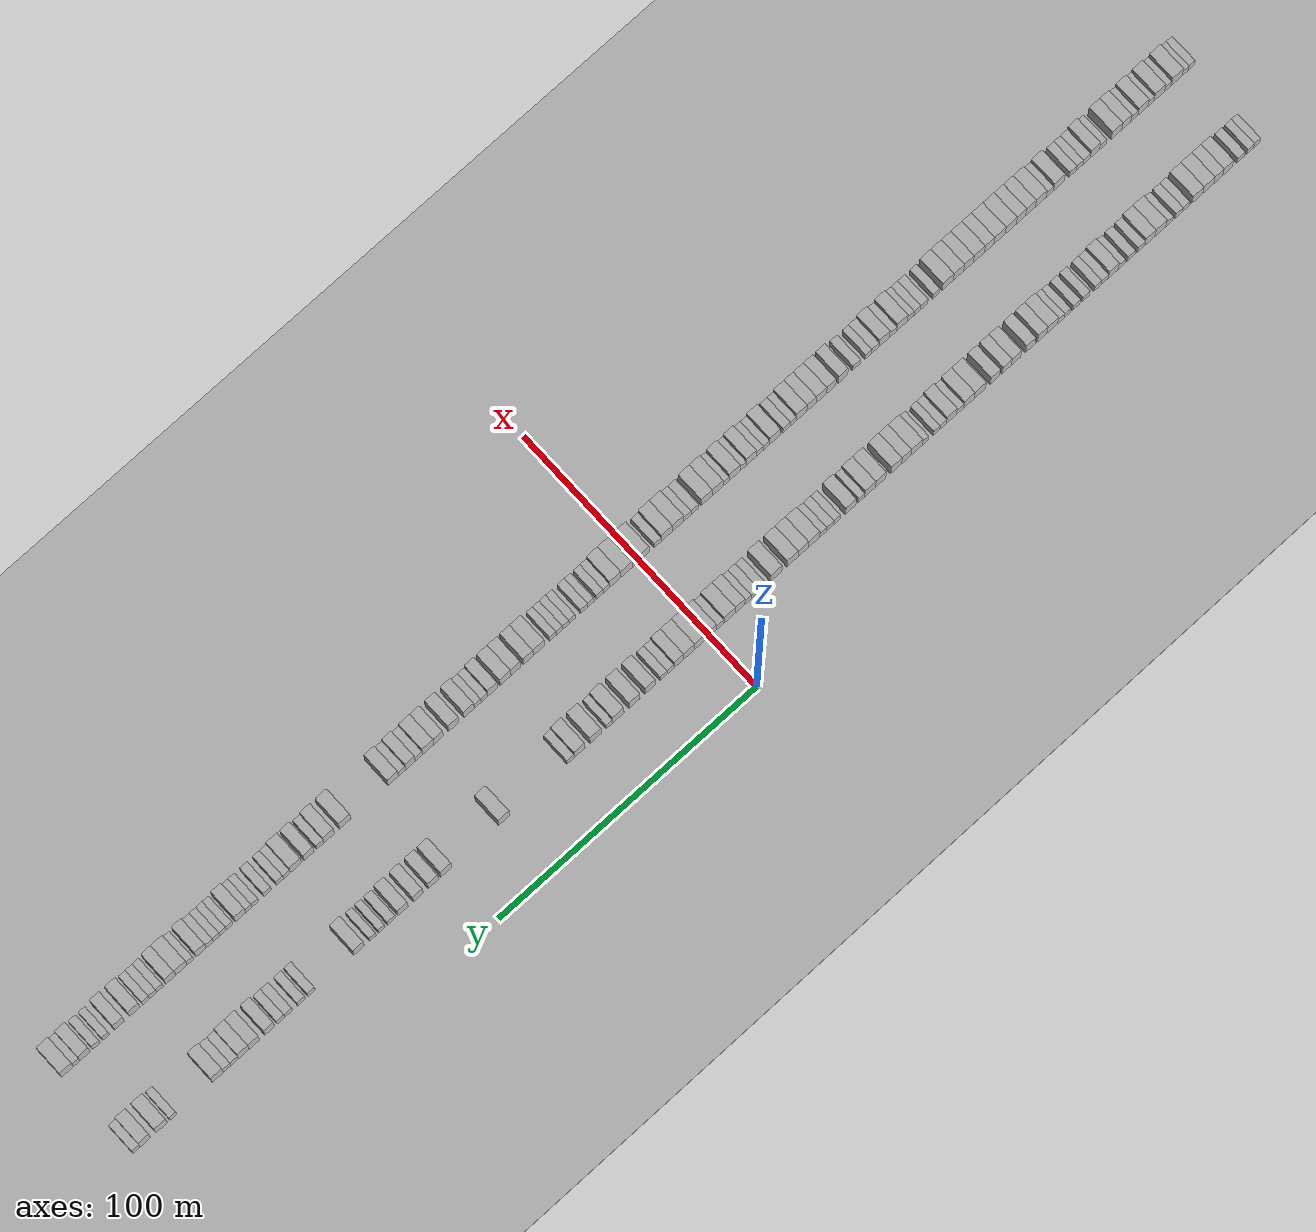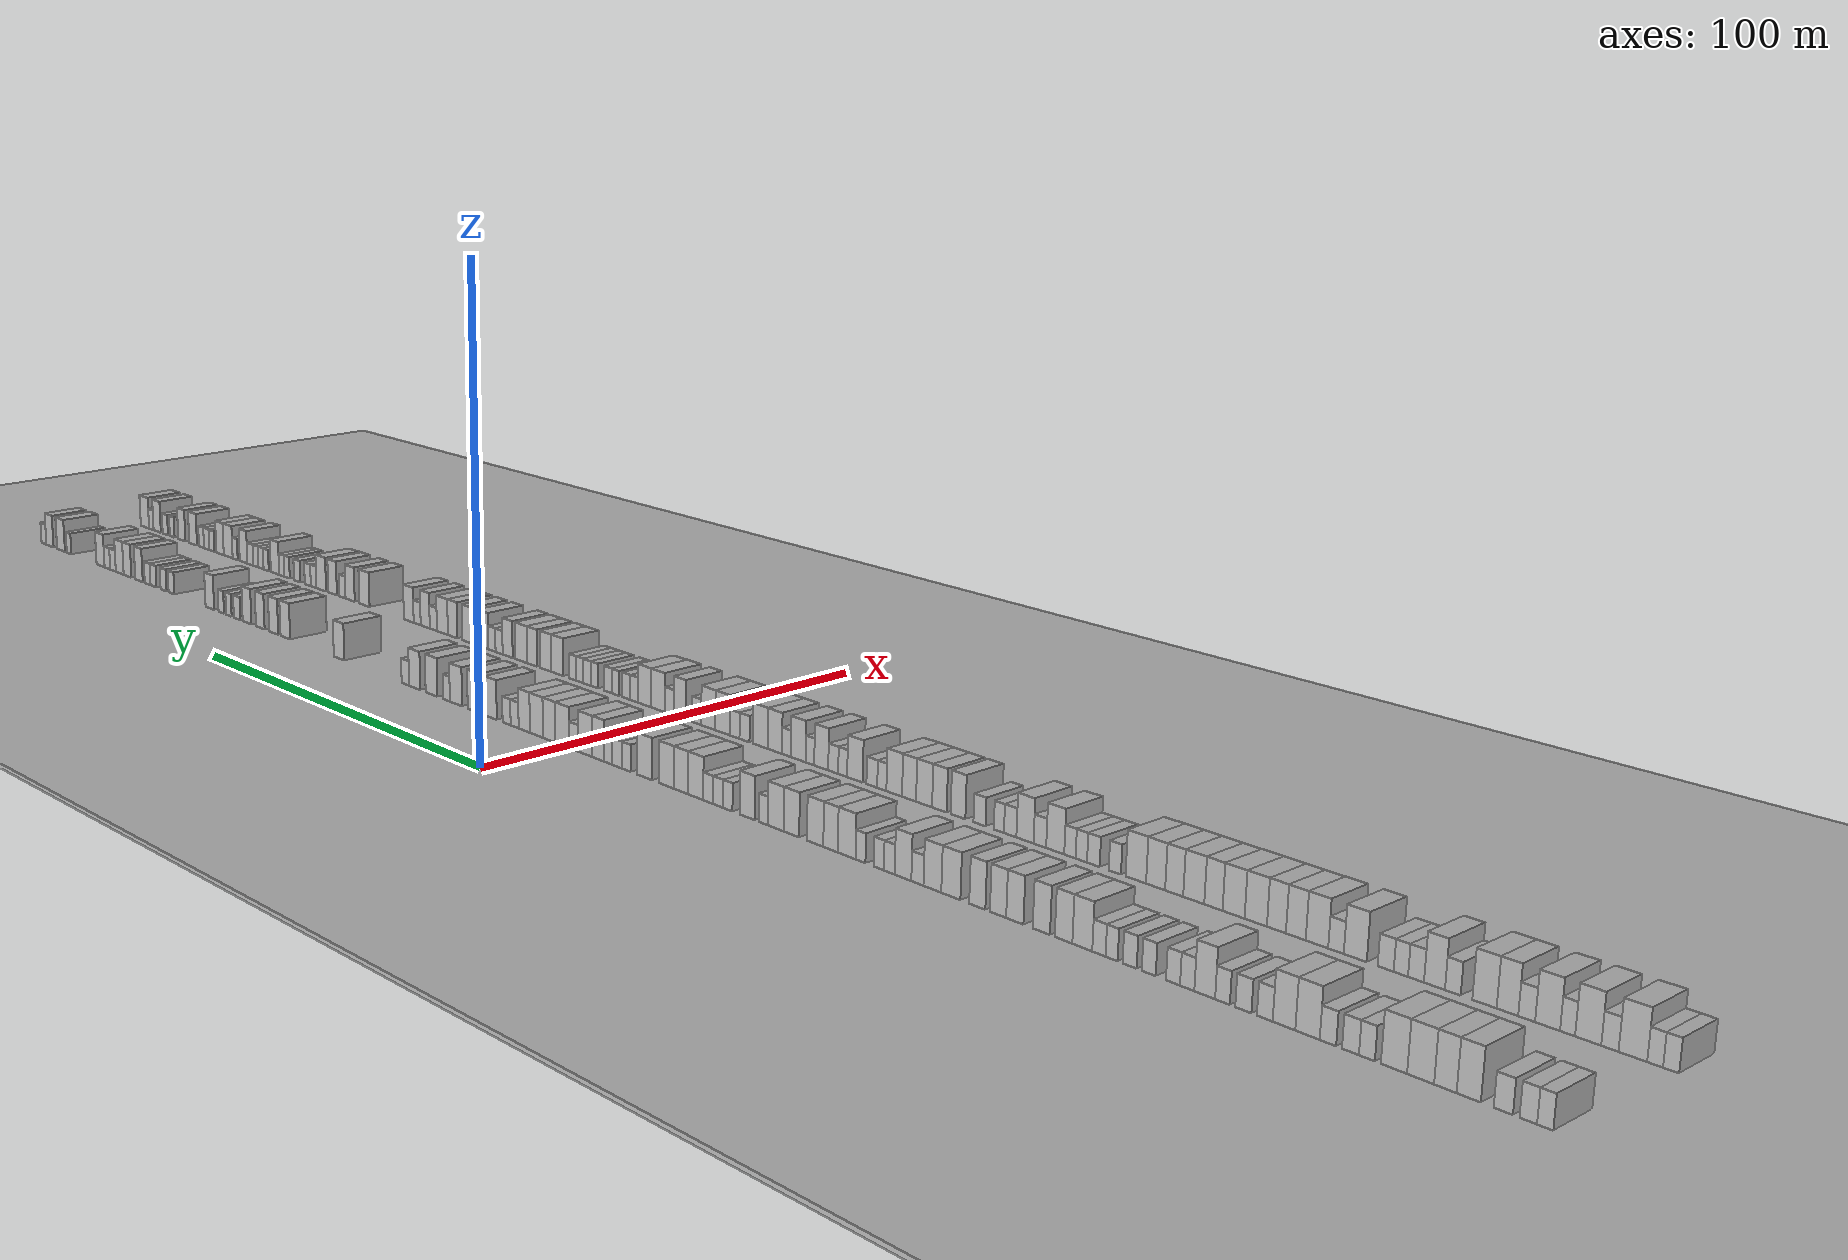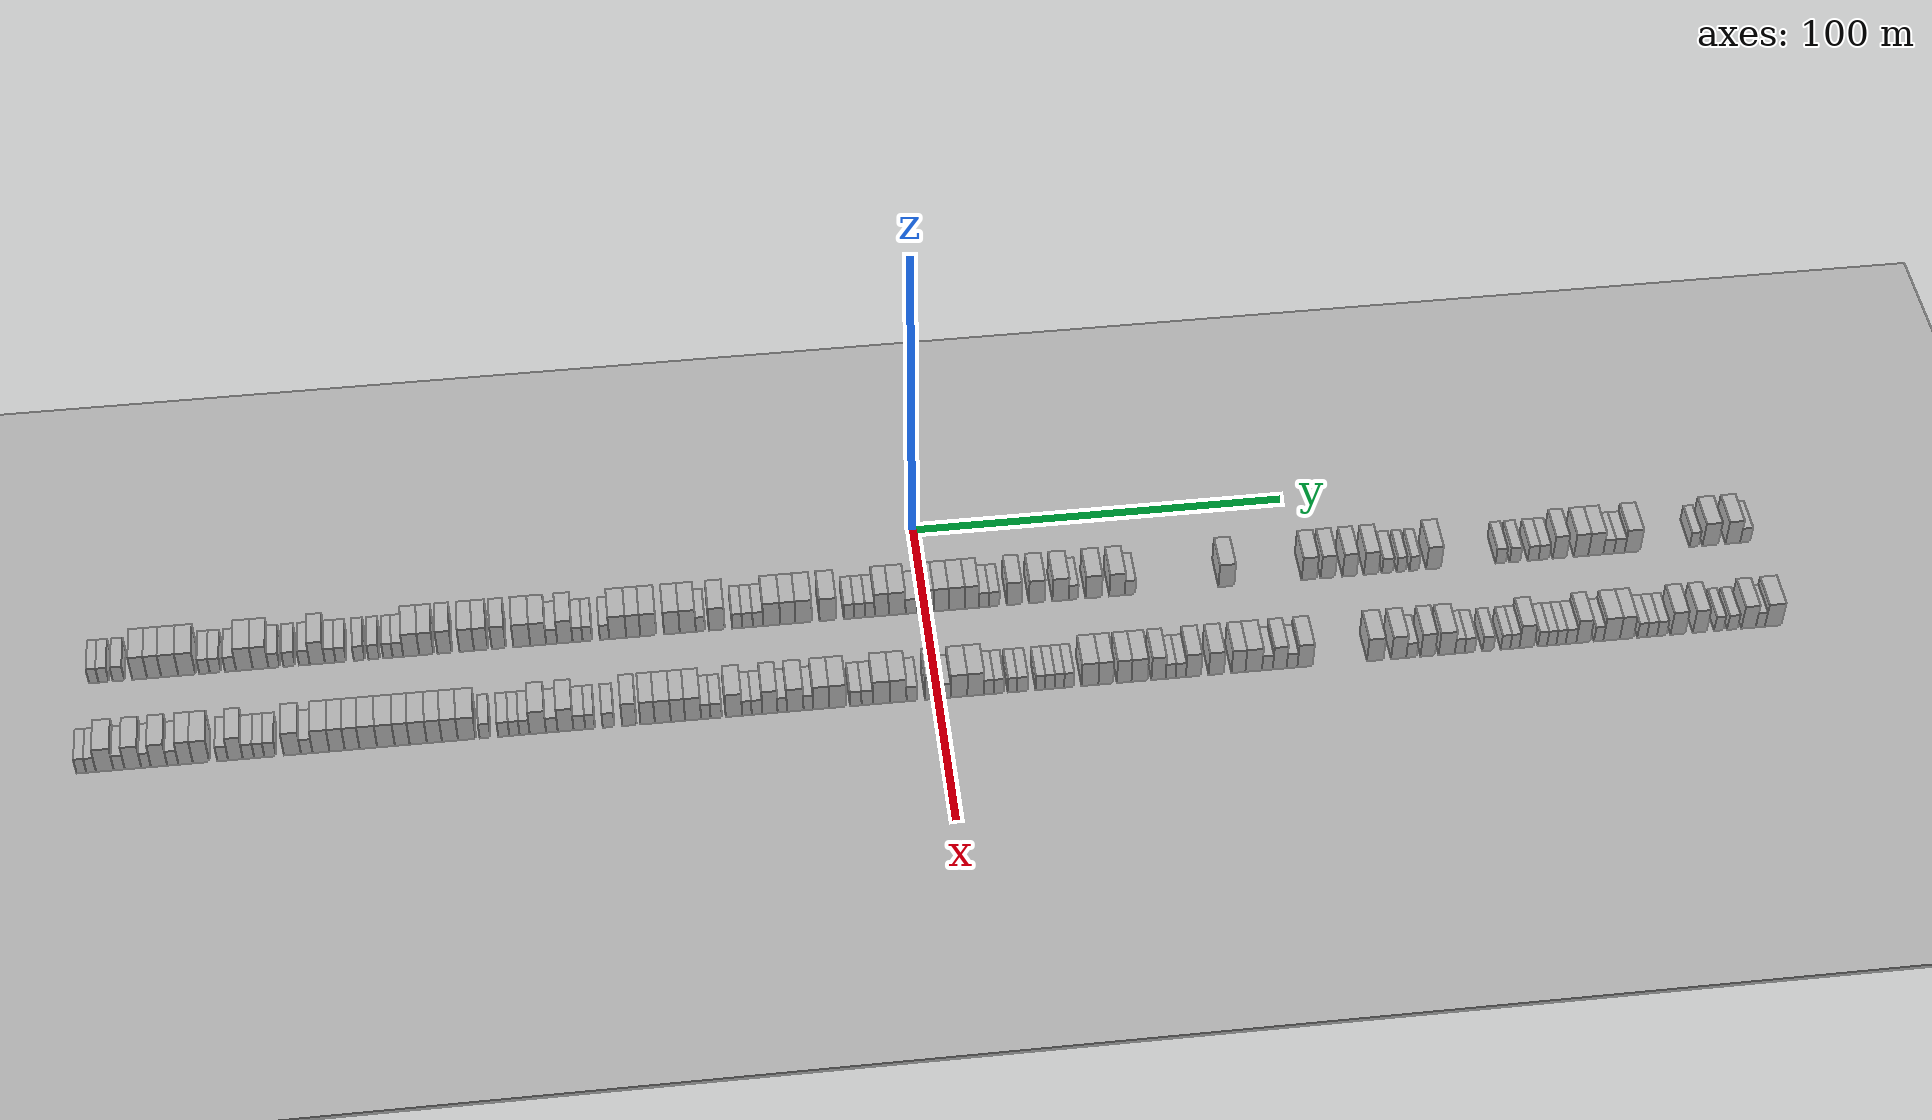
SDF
<?xml version="1.0" encoding="utf-8"?>

<sdf version="1.6">

   <world name="default">

      <gui fullscreen="0">

         <camera name="user_camera">

            <pose>-15 0 4.57585 0 0 0</pose>

            <view_controller>orbit</view_controller>

         </camera>

      </gui>

      <scene>

         <sky>

           <clouds>

             <speed>12</speed>

           </clouds>

         </sky>

         <ambient>0.4 0.4 0.4 1</ambient>

         <background>0.7 0.7 0.7 1</background>

         <shadows>1</shadows>

      </scene>

      <gravity>0 0 -9.8066</gravity>

      <magnetic_field>6e-06 2.3e-05 -4.2e-05</magnetic_field>

      <physics default="0" name="default_physics" type="ode">

         <ode>

            <solver>

               <type>quick</type>

               <iters>10</iters>

               <sor>1.0</sor>

               <use_dynamic_moi_rescaling>0</use_dynamic_moi_rescaling>

            </solver>

            <constraints>

               <cfm>0</cfm>

               <erp>0.2</erp>

               <contact_max_correcting_vel>100</contact_max_correcting_vel>

               <contact_surface_layer>0.001</contact_surface_layer>

            </constraints>

         </ode>

         <max_step_size>0.004</max_step_size>

         <real_time_factor>1</real_time_factor>

         <real_time_update_rate>250</real_time_update_rate>

      </physics>

      <light name="sun" type="directional">

         <cast_shadows>1</cast_shadows>

         <pose>0 0 10 0 0 0</pose>

         <diffuse>0.8 0.8 0.8 1</diffuse>

         <specular>0.2 0.2 0.2 1</specular>

         <attenuation>

            <range>1000</range>

            <constant>0.9</constant>

            <linear>0.01</linear>

            <quadratic>0.001</quadratic>

         </attenuation>

         <direction>-0.5 0.1 -0.9</direction>

      </light>

      <include>

         <name>ground_plane_1</name>

         <uri>model://HANNAS_ground_plane</uri>

         <pose>0 0 0  0 0 0</pose>

      </include>

      <include>

         <name>ground_plane_2</name>

         <uri>model://HANNAS_ground_plane</uri>

         <pose>100 0 0  0 0 0</pose>

      </include>

      <model name="building_1">

         <static>1</static>

         <pose frame="">25.0000 -216.7760 0 0.000000 0.000000 0.000000</pose>

         <link name="link">

            <pose frame="">0 0 3.00 0 0 0</pose>

            <collision name="collision">

               <geometry>

                  <box>

                     <size>10.0000 2.4479 6.0000</size>

                  </box>

               </geometry>

               <max_contacts>10</max_contacts>

               <surface>

                  <contact>

                     <ode/>

                  </contact>

                  <bounce/>

                  <friction>

                     <torsional>

                        <ode/>

                     </torsional>

                     <ode/>

                  </friction>

               </surface>

            </collision>

            <visual name="visual">

               <cast_shadows>0</cast_shadows>

               <geometry>

                  <box>

                     <size>10.0000 2.4479 6.0000</size>

                  </box>

               </geometry>

               <material>

                  <script>

                     <uri>model://HANNAS_wall/materials/scripts</uri>

                     <uri>model://HANNAS_wall/materials/textures</uri>

                     <name>vrc/HANNAS_wall</name>

                  </script>

               </material>

            </visual>

            <self_collide>0</self_collide>

            <enable_wind>0</enable_wind>

            <kinematic>0</kinematic>

         </link>

      </model>

      <model name="building_2">

         <static>1</static>

         <pose frame="">25.0000 -214.2134 0 0.000000 0.000000 0.000000</pose>

         <link name="link">

            <pose frame="">0 0 3.00 0 0 0</pose>

            <collision name="collision">

               <geometry>

                  <box>

                     <size>10.0000 2.6773 6.0000</size>

                  </box>

               </geometry>

               <max_contacts>10</max_contacts>

               <surface>

                  <contact>

                     <ode/>

                  </contact>

                  <bounce/>

                  <friction>

                     <torsional>

                        <ode/>

                     </torsional>

                     <ode/>

                  </friction>

               </surface>

            </collision>

            <visual name="visual">

               <cast_shadows>0</cast_shadows>

               <geometry>

                  <box>

                     <size>10.0000 2.6773 6.0000</size>

                  </box>

               </geometry>

               <material>

                  <script>

                     <uri>model://HANNAS_wall/materials/scripts</uri>

                     <uri>model://HANNAS_wall/materials/textures</uri>

                     <name>vrc/HANNAS_wall</name>

                  </script>

               </material>

            </visual>

            <self_collide>0</self_collide>

            <enable_wind>0</enable_wind>

            <kinematic>0</kinematic>

         </link>

      </model>

      <model name="building_3">

         <static>1</static>

         <pose frame="">25.0000 -210.3815 0 0.000000 0.000000 0.000000</pose>

         <link name="link">

            <pose frame="">0 0 3.00 0 0 0</pose>

            <collision name="collision">

               <geometry>

                  <box>

                     <size>10.0000 2.9865 6.0000</size>

                  </box>

               </geometry>

               <max_contacts>10</max_contacts>

               <surface>

                  <contact>

                     <ode/>

                  </contact>

                  <bounce/>

                  <friction>

                     <torsional>

                        <ode/>

                     </torsional>

                     <ode/>

                  </friction>

               </surface>

            </collision>

            <visual name="visual">

               <cast_shadows>0</cast_shadows>

               <geometry>

                  <box>

                     <size>10.0000 2.9865 6.0000</size>

                  </box>

               </geometry>

               <material>

                  <script>

                     <uri>model://HANNAS_wall/materials/scripts</uri>

                     <uri>model://HANNAS_wall/materials/textures</uri>

                     <name>vrc/HANNAS_wall</name>

                  </script>

               </material>

            </visual>

            <self_collide>0</self_collide>

            <enable_wind>0</enable_wind>

            <kinematic>0</kinematic>

         </link>

      </model>

      <model name="building_4">

         <static>1</static>

         <pose frame="">25.0000 -204.9679 0 0.000000 0.000000 0.000000</pose>

         <link name="link">

            <pose frame="">0 0 4.50 0 0 0</pose>

            <collision name="collision">

               <geometry>

                  <box>

                     <size>10.0000 3.8408 9.0000</size>

                  </box>

               </geometry>

               <max_contacts>10</max_contacts>

               <surface>

                  <contact>

                     <ode/>

                  </contact>

                  <bounce/>

                  <friction>

                     <torsional>

                        <ode/>

                     </torsional>

                     <ode/>

                  </friction>

               </surface>

            </collision>

            <visual name="visual">

               <cast_shadows>0</cast_shadows>

               <geometry>

                  <box>

                     <size>10.0000 3.8408 9.0000</size>

                  </box>

               </geometry>

               <material>

                  <script>

                     <uri>model://HANNAS_wall/materials/scripts</uri>

                     <uri>model://HANNAS_wall/materials/textures</uri>

                     <name>vrc/HANNAS_wall</name>

                  </script>

               </material>

            </visual>

            <self_collide>0</self_collide>

            <enable_wind>0</enable_wind>

            <kinematic>0</kinematic>

         </link>

      </model>

      <model name="building_5">

         <static>1</static>

         <pose frame="">25.0000 -201.2389 0 0.000000 0.000000 0.000000</pose>

         <link name="link">

            <pose frame="">0 0 4.50 0 0 0</pose>

            <collision name="collision">

               <geometry>

                  <box>

                     <size>10.0000 3.6171 9.0000</size>

                  </box>

               </geometry>

               <max_contacts>10</max_contacts>

               <surface>

                  <contact>

                     <ode/>

                  </contact>

                  <bounce/>

                  <friction>

                     <torsional>

                        <ode/>

                     </torsional>

                     <ode/>

                  </friction>

               </surface>

            </collision>

            <visual name="visual">

               <cast_shadows>0</cast_shadows>

               <geometry>

                  <box>

                     <size>10.0000 3.6171 9.0000</size>

                  </box>

               </geometry>

               <material>

                  <script>

                     <uri>model://HANNAS_wall/materials/scripts</uri>

                     <uri>model://HANNAS_wall/materials/textures</uri>

                     <name>vrc/HANNAS_wall</name>

                  </script>

               </material>

            </visual>

            <self_collide>0</self_collide>

            <enable_wind>0</enable_wind>

            <kinematic>0</kinematic>

         </link>

      </model>

      <model name="building_6">

         <static>1</static>

         <pose frame="">25.0000 -197.2296 0 0.000000 0.000000 0.000000</pose>

         <link name="link">

            <pose frame="">0 0 4.50 0 0 0</pose>

            <collision name="collision">

               <geometry>

                  <box>

                     <size>10.0000 4.4016 9.0000</size>

                  </box>

               </geometry>

               <max_contacts>10</max_contacts>

               <surface>

                  <contact>

                     <ode/>

                  </contact>

                  <bounce/>

                  <friction>

                     <torsional>

                        <ode/>

                     </torsional>

                     <ode/>

                  </friction>

               </surface>

            </collision>

            <visual name="visual">

               <cast_shadows>0</cast_shadows>

               <geometry>

                  <box>

                     <size>10.0000 4.4016 9.0000</size>

                  </box>

               </geometry>

               <material>

                  <script>

                     <uri>model://HANNAS_wall/materials/scripts</uri>

                     <uri>model://HANNAS_wall/materials/textures</uri>

                     <name>vrc/HANNAS_wall</name>

                  </script>

               </material>

            </visual>

            <self_collide>0</self_collide>

            <enable_wind>0</enable_wind>

            <kinematic>0</kinematic>

         </link>

      </model>

      <model name="building_7">

         <static>1</static>

         <pose frame="">25.0000 -192.8415 0 0.000000 0.000000 0.000000</pose>

         <link name="link">

            <pose frame="">0 0 4.50 0 0 0</pose>

            <collision name="collision">

               <geometry>

                  <box>

                     <size>10.0000 4.3745 9.0000</size>

                  </box>

               </geometry>

               <max_contacts>10</max_contacts>

               <surface>

                  <contact>

                     <ode/>

                  </contact>

                  <bounce/>

                  <friction>

                     <torsional>

                        <ode/>

                     </torsional>

                     <ode/>

                  </friction>

               </surface>

            </collision>

            <visual name="visual">

               <cast_shadows>0</cast_shadows>

               <geometry>

                  <box>

                     <size>10.0000 4.3745 9.0000</size>

                  </box>

               </geometry>

               <material>

                  <script>

                     <uri>model://HANNAS_wall/materials/scripts</uri>

                     <uri>model://HANNAS_wall/materials/textures</uri>

                     <name>vrc/HANNAS_wall</name>

                  </script>

               </material>

            </visual>

            <self_collide>0</self_collide>

            <enable_wind>0</enable_wind>

            <kinematic>0</kinematic>

         </link>

      </model>

      <model name="building_8">

         <static>1</static>

         <pose frame="">25.0000 -188.3045 0 0.000000 0.000000 0.000000</pose>

         <link name="link">

            <pose frame="">0 0 3.00 0 0 0</pose>

            <collision name="collision">

               <geometry>

                  <box>

                     <size>10.0000 2.6996 6.0000</size>

                  </box>

               </geometry>

               <max_contacts>10</max_contacts>

               <surface>

                  <contact>

                     <ode/>

                  </contact>

                  <bounce/>

                  <friction>

                     <torsional>

                        <ode/>

                     </torsional>

                     <ode/>

                  </friction>

               </surface>

            </collision>

            <visual name="visual">

               <cast_shadows>0</cast_shadows>

               <geometry>

                  <box>

                     <size>10.0000 2.6996 6.0000</size>

                  </box>

               </geometry>

               <material>

                  <script>

                     <uri>model://HANNAS_wall/materials/scripts</uri>

                     <uri>model://HANNAS_wall/materials/textures</uri>

                     <name>vrc/HANNAS_wall</name>

                  </script>

               </material>

            </visual>

            <self_collide>0</self_collide>

            <enable_wind>0</enable_wind>

            <kinematic>0</kinematic>

         </link>

      </model>

      <model name="building_9">

         <static>1</static>

         <pose frame="">25.0000 -185.5023 0 0.000000 0.000000 0.000000</pose>

         <link name="link">

            <pose frame="">0 0 3.00 0 0 0</pose>

            <collision name="collision">

               <geometry>

                  <box>

                     <size>10.0000 2.9047 6.0000</size>

                  </box>

               </geometry>

               <max_contacts>10</max_contacts>

               <surface>

                  <contact>

                     <ode/>

                  </contact>

                  <bounce/>

                  <friction>

                     <torsional>

                        <ode/>

                     </torsional>

                     <ode/>

                  </friction>

               </surface>

            </collision>

            <visual name="visual">

               <cast_shadows>0</cast_shadows>

               <geometry>

                  <box>

                     <size>10.0000 2.9047 6.0000</size>

                  </box>

               </geometry>

               <material>

                  <script>

                     <uri>model://HANNAS_wall/materials/scripts</uri>

                     <uri>model://HANNAS_wall/materials/textures</uri>

                     <name>vrc/HANNAS_wall</name>

                  </script>

               </material>

            </visual>

            <self_collide>0</self_collide>

            <enable_wind>0</enable_wind>

            <kinematic>0</kinematic>

         </link>

      </model>

      <model name="building_10">

         <static>1</static>

         <pose frame="">25.0000 -181.6182 0 0.000000 0.000000 0.000000</pose>

         <link name="link">

            <pose frame="">0 0 3.00 0 0 0</pose>

            <collision name="collision">

               <geometry>

                  <box>

                     <size>10.0000 2.8635 6.0000</size>

                  </box>

               </geometry>

               <max_contacts>10</max_contacts>

               <surface>

                  <contact>

                     <ode/>

                  </contact>

                  <bounce/>

                  <friction>

                     <torsional>

                        <ode/>

                     </torsional>

                     <ode/>

                  </friction>

               </surface>

            </collision>

            <visual name="visual">

               <cast_shadows>0</cast_shadows>

               <geometry>

                  <box>

                     <size>10.0000 2.8635 6.0000</size>

                  </box>

               </geometry>

               <material>

                  <script>

                     <uri>model://HANNAS_wall/materials/scripts</uri>

                     <uri>model://HANNAS_wall/materials/textures</uri>

                     <name>vrc/HANNAS_wall</name>

                  </script>

               </material>

            </visual>

            <self_collide>0</self_collide>

            <enable_wind>0</enable_wind>

            <kinematic>0</kinematic>

         </link>

      </model>

      <model name="building_11">

         <static>1</static>

         <pose frame="">25.0000 -178.0315 0 0.000000 0.000000 0.000000</pose>

         <link name="link">

            <pose frame="">0 0 4.50 0 0 0</pose>

            <collision name="collision">

               <geometry>

                  <box>

                     <size>10.0000 4.3098 9.0000</size>

                  </box>

               </geometry>

               <max_contacts>10</max_contacts>

               <surface>

                  <contact>

                     <ode/>

                  </contact>

                  <bounce/>

                  <friction>

                     <torsional>

                        <ode/>

                     </torsional>

                     <ode/>

                  </friction>

               </surface>

            </collision>

            <visual name="visual">

               <cast_shadows>0</cast_shadows>

               <geometry>

                  <box>

                     <size>10.0000 4.3098 9.0000</size>

                  </box>

               </geometry>

               <material>

                  <script>

                     <uri>model://HANNAS_wall/materials/scripts</uri>

                     <uri>model://HANNAS_wall/materials/textures</uri>

                     <name>vrc/HANNAS_wall</name>

                  </script>

               </material>

            </visual>

            <self_collide>0</self_collide>

            <enable_wind>0</enable_wind>

            <kinematic>0</kinematic>

         </link>

      </model>

      <model name="building_12">

         <static>1</static>

         <pose frame="">25.0000 -173.8464 0 0.000000 0.000000 0.000000</pose>

         <link name="link">

            <pose frame="">0 0 4.50 0 0 0</pose>

            <collision name="collision">

               <geometry>

                  <box>

                     <size>10.0000 4.0604 9.0000</size>

                  </box>

               </geometry>

               <max_contacts>10</max_contacts>

               <surface>

                  <contact>

                     <ode/>

                  </contact>

                  <bounce/>

                  <friction>

                     <torsional>

                        <ode/>

                     </torsional>

                     <ode/>

                  </friction>

               </surface>

            </collision>

            <visual name="visual">

               <cast_shadows>0</cast_shadows>

               <geometry>

                  <box>

                     <size>10.0000 4.0604 9.0000</size>

                  </box>

               </geometry>

               <material>

                  <script>

                     <uri>model://HANNAS_wall/materials/scripts</uri>

                     <uri>model://HANNAS_wall/materials/textures</uri>

                     <name>vrc/HANNAS_wall</name>

                  </script>

               </material>

            </visual>

            <self_collide>0</self_collide>

            <enable_wind>0</enable_wind>

            <kinematic>0</kinematic>

         </link>

      </model>

      <model name="building_13">

         <static>1</static>

         <pose frame="">25.0000 -170.3806 0 0.000000 0.000000 0.000000</pose>

         <link name="link">

            <pose frame="">0 0 3.00 0 0 0</pose>

            <collision name="collision">

               <geometry>

                  <box>

                     <size>10.0000 2.8712 6.0000</size>

                  </box>

               </geometry>

               <max_contacts>10</max_contacts>

               <surface>

                  <contact>

                     <ode/>

                  </contact>

                  <bounce/>

                  <friction>

                     <torsional>

                        <ode/>

                     </torsional>

                     <ode/>

                  </friction>

               </surface>

            </collision>

            <visual name="visual">

               <cast_shadows>0</cast_shadows>

               <geometry>

                  <box>

                     <size>10.0000 2.8712 6.0000</size>

                  </box>

               </geometry>

               <material>

                  <script>

                     <uri>model://HANNAS_wall/materials/scripts</uri>

                     <uri>model://HANNAS_wall/materials/textures</uri>

                     <name>vrc/HANNAS_wall</name>

                  </script>

               </material>

            </visual>

            <self_collide>0</self_collide>

            <enable_wind>0</enable_wind>

            <kinematic>0</kinematic>

         </link>

      </model>

      <model name="building_14">

         <static>1</static>

         <pose frame="">25.0000 -166.4511 0 0.000000 0.000000 0.000000</pose>

         <link name="link">

            <pose frame="">0 0 3.00 0 0 0</pose>

            <collision name="collision">

               <geometry>

                  <box>

                     <size>10.0000 2.9879 6.0000</size>

                  </box>

               </geometry>

               <max_contacts>10</max_contacts>

               <surface>

                  <contact>

                     <ode/>

                  </contact>

                  <bounce/>

                  <friction>

                     <torsional>

                        <ode/>

                     </torsional>

                     <ode/>

                  </friction>

               </surface>

            </collision>

            <visual name="visual">

               <cast_shadows>0</cast_shadows>

               <geometry>

                  <box>

                     <size>10.0000 2.9879 6.0000</size>

                  </box>

               </geometry>

               <material>

                  <script>

                     <uri>model://HANNAS_wall/materials/scripts</uri>

                     <uri>model://HANNAS_wall/materials/textures</uri>

                     <name>vrc/HANNAS_wall</name>

                  </script>

               </material>

            </visual>

            <self_collide>0</self_collide>

            <enable_wind>0</enable_wind>

            <kinematic>0</kinematic>

         </link>

      </model>

      <model name="building_15">

         <static>1</static>

         <pose frame="">25.0000 -162.5718 0 0.000000 0.000000 0.000000</pose>

         <link name="link">

            <pose frame="">0 0 3.00 0 0 0</pose>

            <collision name="collision">

               <geometry>

                  <box>

                     <size>10.0000 2.7707 6.0000</size>

                  </box>

               </geometry>

               <max_contacts>10</max_contacts>

               <surface>

                  <contact>

                     <ode/>

                  </contact>

                  <bounce/>

                  <friction>

                     <torsional>

                        <ode/>

                     </torsional>

                     <ode/>

                  </friction>

               </surface>

            </collision>

            <visual name="visual">

               <cast_shadows>0</cast_shadows>

               <geometry>

                  <box>

                     <size>10.0000 2.7707 6.0000</size>

                  </box>

               </geometry>

               <material>

                  <script>

                     <uri>model://HANNAS_wall/materials/scripts</uri>

                     <uri>model://HANNAS_wall/materials/textures</uri>

                     <name>vrc/HANNAS_wall</name>

                  </script>

               </material>

            </visual>

            <self_collide>0</self_collide>

            <enable_wind>0</enable_wind>

            <kinematic>0</kinematic>

         </link>

      </model>

      <model name="building_16">

         <static>1</static>

         <pose frame="">25.0000 -159.2121 0 0.000000 0.000000 0.000000</pose>

         <link name="link">

            <pose frame="">0 0 4.50 0 0 0</pose>

            <collision name="collision">

               <geometry>

                  <box>

                     <size>10.0000 3.9487 9.0000</size>

                  </box>

               </geometry>

               <max_contacts>10</max_contacts>

               <surface>

                  <contact>

                     <ode/>

                  </contact>

                  <bounce/>

                  <friction>

                     <torsional>

                        <ode/>

                     </torsional>

                     <ode/>

                  </friction>

               </surface>

            </collision>

            <visual name="visual">

               <cast_shadows>0</cast_shadows>

               <geometry>

                  <box>

                     <size>10.0000 3.9487 9.0000</size>

                  </box>

               </geometry>

               <material>

                  <script>

                     <uri>model://HANNAS_wall/materials/scripts</uri>

                     <uri>model://HANNAS_wall/materials/textures</uri>

                     <name>vrc/HANNAS_wall</name>

                  </script>

               </material>

            </visual>

            <self_collide>0</self_collide>

            <enable_wind>0</enable_wind>

            <kinematic>0</kinematic>

         </link>

      </model>

      <model name="building_17">

         <static>1</static>

         <pose frame="">25.0000 -155.8626 0 0.000000 0.000000 0.000000</pose>

         <link name="link">

            <pose frame="">0 0 3.00 0 0 0</pose>

            <collision name="collision">

               <geometry>

                  <box>

                     <size>10.0000 2.7504 6.0000</size>

                  </box>

               </geometry>

               <max_contacts>10</max_contacts>

               <surface>

                  <contact>

                     <ode/>

                  </contact>

                  <bounce/>

                  <friction>

                     <torsional>

                        <ode/>

                     </torsional>

                     <ode/>

                  </friction>

               </surface>

            </collision>

            <visual name="visual">

               <cast_shadows>0</cast_shadows>

               <geometry>

                  <box>

                     <size>10.0000 2.7504 6.0000</size>

                  </box>

               </geometry>

               <material>

                  <script>

                     <uri>model://HANNAS_wall/materials/scripts</uri>

                     <uri>model://HANNAS_wall/materials/textures</uri>

                     <name>vrc/HANNAS_wall</name>

                  </script>

               </material>

            </visual>

            <self_collide>0</self_collide>

            <enable_wind>0</enable_wind>

            <kinematic>0</kinematic>

         </link>

      </model>

      <model name="building_18">

         <static>1</static>

         <pose frame="">25.0000 -153.1238 0 0.000000 0.000000 0.000000</pose>

         <link name="link">

            <pose frame="">0 0 3.00 0 0 0</pose>

            <collision name="collision">

               <geometry>

                  <box>

                     <size>10.0000 2.7271 6.0000</size>

                  </box>

               </geometry>

               <max_contacts>10</max_contacts>

               <surface>

                  <contact>

                     <ode/>

                  </contact>

                  <bounce/>

                  <friction>

                     <torsional>

                        <ode/>

                     </torsional>

                     <ode/>

                  </friction>

               </surface>

            </collision>

            <visual name="visual">

               <cast_shadows>0</cast_shadows>

               <geometry>

                  <box>

                     <size>10.0000 2.7271 6.0000</size>

                  </box>

               </geometry>

               <material>

                  <script>

                     <uri>model://HANNAS_wall/materials/scripts</uri>

                     <uri>model://HANNAS_wall/materials/textures</uri>

                     <name>vrc/HANNAS_wall</name>

                  </script>

               </material>

            </visual>

            <self_collide>0</self_collide>

            <enable_wind>0</enable_wind>

            <kinematic>0</kinematic>

         </link>

      </model>

      <model name="building_19">

         <static>1</static>

         <pose frame="">25.0000 -148.3723 0 0.000000 0.000000 0.000000</pose>

         <link name="link">

            <pose frame="">0 0 3.00 0 0 0</pose>

            <collision name="collision">

               <geometry>

                  <box>

                     <size>10.0000 2.7759 6.0000</size>

                  </box>

               </geometry>

               <max_contacts>10</max_contacts>

               <surface>

                  <contact>

                     <ode/>

                  </contact>

                  <bounce/>

                  <friction>

                     <torsional>

                        <ode/>

                     </torsional>

                     <ode/>

                  </friction>

               </surface>

            </collision>

            <visual name="visual">

               <cast_shadows>0</cast_shadows>

               <geometry>

                  <box>

                     <size>10.0000 2.7759 6.0000</size>

                  </box>

               </geometry>

               <material>

                  <script>

                     <uri>model://HANNAS_wall/materials/scripts</uri>

                     <uri>model://HANNAS_wall/materials/textures</uri>

                     <name>vrc/HANNAS_wall</name>

                  </script>

               </material>

            </visual>

            <self_collide>0</self_collide>

            <enable_wind>0</enable_wind>

            <kinematic>0</kinematic>

         </link>

      </model>

      <model name="building_20">

         <static>1</static>

         <pose frame="">25.0000 -144.5683 0 0.000000 0.000000 0.000000</pose>

         <link name="link">

            <pose frame="">0 0 3.00 0 0 0</pose>

            <collision name="collision">

               <geometry>

                  <box>

                     <size>10.0000 2.8321 6.0000</size>

                  </box>

               </geometry>

               <max_contacts>10</max_contacts>

               <surface>

                  <contact>

                     <ode/>

                  </contact>

                  <bounce/>

                  <friction>

                     <torsional>

                        <ode/>

                     </torsional>

                     <ode/>

                  </friction>

               </surface>

            </collision>

            <visual name="visual">

               <cast_shadows>0</cast_shadows>

               <geometry>

                  <box>

                     <size>10.0000 2.8321 6.0000</size>

                  </box>

               </geometry>

               <material>

                  <script>

                     <uri>model://HANNAS_wall/materials/scripts</uri>

                     <uri>model://HANNAS_wall/materials/textures</uri>

                     <name>vrc/HANNAS_wall</name>

                  </script>

               </material>

            </visual>

            <self_collide>0</self_collide>

            <enable_wind>0</enable_wind>

            <kinematic>0</kinematic>

         </link>

      </model>

      <model name="building_21">

         <static>1</static>

         <pose frame="">25.0000 -140.9230 0 0.000000 0.000000 0.000000</pose>

         <link name="link">

            <pose frame="">0 0 3.00 0 0 0</pose>

            <collision name="collision">

               <geometry>

                  <box>

                     <size>10.0000 2.4585 6.0000</size>

                  </box>

               </geometry>

               <max_contacts>10</max_contacts>

               <surface>

                  <contact>

                     <ode/>

                  </contact>

                  <bounce/>

                  <friction>

                     <torsional>

                        <ode/>

                     </torsional>

                     <ode/>

                  </friction>

               </surface>

            </collision>

            <visual name="visual">

               <cast_shadows>0</cast_shadows>

               <geometry>

                  <box>

                     <size>10.0000 2.4585 6.0000</size>

                  </box>

               </geometry>

               <material>

                  <script>

                     <uri>model://HANNAS_wall/materials/scripts</uri>

                     <uri>model://HANNAS_wall/materials/textures</uri>

                     <name>vrc/HANNAS_wall</name>

                  </script>

               </material>

            </visual>

            <self_collide>0</self_collide>

            <enable_wind>0</enable_wind>

            <kinematic>0</kinematic>

         </link>

      </model>

      <model name="building_22">

         <static>1</static>

         <pose frame="">25.0000 -138.3307 0 0.000000 0.000000 0.000000</pose>

         <link name="link">

            <pose frame="">0 0 3.00 0 0 0</pose>

            <collision name="collision">

               <geometry>

                  <box>

                     <size>10.0000 2.7261 6.0000</size>

                  </box>

               </geometry>

               <max_contacts>10</max_contacts>

               <surface>

                  <contact>

                     <ode/>

                  </contact>

                  <bounce/>

                  <friction>

                     <torsional>

                        <ode/>

                     </torsional>

                     <ode/>

                  </friction>

               </surface>

            </collision>

            <visual name="visual">

               <cast_shadows>0</cast_shadows>

               <geometry>

                  <box>

                     <size>10.0000 2.7261 6.0000</size>

                  </box>

               </geometry>

               <material>

                  <script>

                     <uri>model://HANNAS_wall/materials/scripts</uri>

                     <uri>model://HANNAS_wall/materials/textures</uri>

                     <name>vrc/HANNAS_wall</name>

                  </script>

               </material>

            </visual>

            <self_collide>0</self_collide>

            <enable_wind>0</enable_wind>

            <kinematic>0</kinematic>

         </link>

      </model>

      <model name="building_23">

         <static>1</static>

         <pose frame="">25.0000 -134.8988 0 0.000000 0.000000 0.000000</pose>

         <link name="link">

            <pose frame="">0 0 4.50 0 0 0</pose>

            <collision name="collision">

               <geometry>

                  <box>

                     <size>10.0000 4.1376 9.0000</size>

                  </box>

               </geometry>

               <max_contacts>10</max_contacts>

               <surface>

                  <contact>

                     <ode/>

                  </contact>

                  <bounce/>

                  <friction>

                     <torsional>

                        <ode/>

                     </torsional>

                     <ode/>

                  </friction>

               </surface>

            </collision>

            <visual name="visual">

               <cast_shadows>0</cast_shadows>

               <geometry>

                  <box>

                     <size>10.0000 4.1376 9.0000</size>

                  </box>

               </geometry>

               <material>

                  <script>

                     <uri>model://HANNAS_wall/materials/scripts</uri>

                     <uri>model://HANNAS_wall/materials/textures</uri>

                     <name>vrc/HANNAS_wall</name>

                  </script>

               </material>

            </visual>

            <self_collide>0</self_collide>

            <enable_wind>0</enable_wind>

            <kinematic>0</kinematic>

         </link>

      </model>

      <model name="building_24">

         <static>1</static>

         <pose frame="">25.0000 -130.9701 0 0.000000 0.000000 0.000000</pose>

         <link name="link">

            <pose frame="">0 0 4.50 0 0 0</pose>

            <collision name="collision">

               <geometry>

                  <box>

                     <size>10.0000 3.7199 9.0000</size>

                  </box>

               </geometry>

               <max_contacts>10</max_contacts>

               <surface>

                  <contact>

                     <ode/>

                  </contact>

                  <bounce/>

                  <friction>

                     <torsional>

                        <ode/>

                     </torsional>

                     <ode/>

                  </friction>

               </surface>

            </collision>

            <visual name="visual">

               <cast_shadows>0</cast_shadows>

               <geometry>

                  <box>

                     <size>10.0000 3.7199 9.0000</size>

                  </box>

               </geometry>

               <material>

                  <script>

                     <uri>model://HANNAS_wall/materials/scripts</uri>

                     <uri>model://HANNAS_wall/materials/textures</uri>

                     <name>vrc/HANNAS_wall</name>

                  </script>

               </material>

            </visual>

            <self_collide>0</self_collide>

            <enable_wind>0</enable_wind>

            <kinematic>0</kinematic>

         </link>

      </model>

      <model name="building_25">

         <static>1</static>

         <pose frame="">25.0000 -126.2509 0 0.000000 0.000000 0.000000</pose>

         <link name="link">

            <pose frame="">0 0 4.50 0 0 0</pose>

            <collision name="collision">

               <geometry>

                  <box>

                     <size>10.0000 3.7184 9.0000</size>

                  </box>

               </geometry>

               <max_contacts>10</max_contacts>

               <surface>

                  <contact>

                     <ode/>

                  </contact>

                  <bounce/>

                  <friction>

                     <torsional>

                        <ode/>

                     </torsional>

                     <ode/>

                  </friction>

               </surface>

            </collision>

            <visual name="visual">

               <cast_shadows>0</cast_shadows>

               <geometry>

                  <box>

                     <size>10.0000 3.7184 9.0000</size>

                  </box>

               </geometry>

               <material>

                  <script>

                     <uri>model://HANNAS_wall/materials/scripts</uri>

                     <uri>model://HANNAS_wall/materials/textures</uri>

                     <name>vrc/HANNAS_wall</name>

                  </script>

               </material>

            </visual>

            <self_collide>0</self_collide>

            <enable_wind>0</enable_wind>

            <kinematic>0</kinematic>

         </link>

      </model>

      <model name="building_26">

         <static>1</static>

         <pose frame="">25.0000 -120.4995 0 0.000000 0.000000 0.000000</pose>

         <link name="link">

            <pose frame="">0 0 4.50 0 0 0</pose>

            <collision name="collision">

               <geometry>

                  <box>

                     <size>10.0000 3.7845 9.0000</size>

                  </box>

               </geometry>

               <max_contacts>10</max_contacts>

               <surface>

                  <contact>

                     <ode/>

                  </contact>

                  <bounce/>

                  <friction>

                     <torsional>

                        <ode/>

                     </torsional>

                     <ode/>

                  </friction>

               </surface>

            </collision>

            <visual name="visual">

               <cast_shadows>0</cast_shadows>

               <geometry>

                  <box>

                     <size>10.0000 3.7845 9.0000</size>

                  </box>

               </geometry>

               <material>

                  <script>

                     <uri>model://HANNAS_wall/materials/scripts</uri>

                     <uri>model://HANNAS_wall/materials/textures</uri>

                     <name>vrc/HANNAS_wall</name>

                  </script>

               </material>

            </visual>

            <self_collide>0</self_collide>

            <enable_wind>0</enable_wind>

            <kinematic>0</kinematic>

         </link>

      </model>

      <model name="building_27">

         <static>1</static>

         <pose frame="">25.0000 -116.7994 0 0.000000 0.000000 0.000000</pose>

         <link name="link">

            <pose frame="">0 0 4.50 0 0 0</pose>

            <collision name="collision">

               <geometry>

                  <box>

                     <size>10.0000 3.6157 9.0000</size>

                  </box>

               </geometry>

               <max_contacts>10</max_contacts>

               <surface>

                  <contact>

                     <ode/>

                  </contact>

                  <bounce/>

                  <friction>

                     <torsional>

                        <ode/>

                     </torsional>

                     <ode/>

                  </friction>

               </surface>

            </collision>

            <visual name="visual">

               <cast_shadows>0</cast_shadows>

               <geometry>

                  <box>

                     <size>10.0000 3.6157 9.0000</size>

                  </box>

               </geometry>

               <material>

                  <script>

                     <uri>model://HANNAS_wall/materials/scripts</uri>

                     <uri>model://HANNAS_wall/materials/textures</uri>

                     <name>vrc/HANNAS_wall</name>

                  </script>

               </material>

            </visual>

            <self_collide>0</self_collide>

            <enable_wind>0</enable_wind>

            <kinematic>0</kinematic>

         </link>

      </model>

      <model name="building_28">

         <static>1</static>

         <pose frame="">25.0000 -112.1677 0 0.000000 0.000000 0.000000</pose>

         <link name="link">

            <pose frame="">0 0 4.50 0 0 0</pose>

            <collision name="collision">

               <geometry>

                  <box>

                     <size>10.0000 3.6477 9.0000</size>

                  </box>

               </geometry>

               <max_contacts>10</max_contacts>

               <surface>

                  <contact>

                     <ode/>

                  </contact>

                  <bounce/>

                  <friction>

                     <torsional>

                        <ode/>

                     </torsional>

                     <ode/>

                  </friction>

               </surface>

            </collision>

            <visual name="visual">

               <cast_shadows>0</cast_shadows>

               <geometry>

                  <box>

                     <size>10.0000 3.6477 9.0000</size>

                  </box>

               </geometry>

               <material>

                  <script>

                     <uri>model://HANNAS_wall/materials/scripts</uri>

                     <uri>model://HANNAS_wall/materials/textures</uri>

                     <name>vrc/HANNAS_wall</name>

                  </script>

               </material>

            </visual>

            <self_collide>0</self_collide>

            <enable_wind>0</enable_wind>

            <kinematic>0</kinematic>

         </link>

      </model>

      <model name="building_29">

         <static>1</static>

         <pose frame="">25.0000 -106.1421 0 0.000000 0.000000 0.000000</pose>

         <link name="link">

            <pose frame="">0 0 4.50 0 0 0</pose>

            <collision name="collision">

               <geometry>

                  <box>

                     <size>10.0000 4.4034 9.0000</size>

                  </box>

               </geometry>

               <max_contacts>10</max_contacts>

               <surface>

                  <contact>

                     <ode/>

                  </contact>

                  <bounce/>

                  <friction>

                     <torsional>

                        <ode/>

                     </torsional>

                     <ode/>

                  </friction>

               </surface>

            </collision>

            <visual name="visual">

               <cast_shadows>0</cast_shadows>

               <geometry>

                  <box>

                     <size>10.0000 4.4034 9.0000</size>

                  </box>

               </geometry>

               <material>

                  <script>

                     <uri>model://HANNAS_wall/materials/scripts</uri>

                     <uri>model://HANNAS_wall/materials/textures</uri>

                     <name>vrc/HANNAS_wall</name>

                  </script>

               </material>

            </visual>

            <self_collide>0</self_collide>

            <enable_wind>0</enable_wind>

            <kinematic>0</kinematic>

         </link>

      </model>

      <model name="building_30">

         <static>1</static>

         <pose frame="">25.0000 -101.8638 0 0.000000 0.000000 0.000000</pose>

         <link name="link">

            <pose frame="">0 0 4.50 0 0 0</pose>

            <collision name="collision">

               <geometry>

                  <box>

                     <size>10.0000 4.1531 9.0000</size>

                  </box>

               </geometry>

               <max_contacts>10</max_contacts>

               <surface>

                  <contact>

                     <ode/>

                  </contact>

                  <bounce/>

                  <friction>

                     <torsional>

                        <ode/>

                     </torsional>

                     <ode/>

                  </friction>

               </surface>

            </collision>

            <visual name="visual">

               <cast_shadows>0</cast_shadows>

               <geometry>

                  <box>

                     <size>10.0000 4.1531 9.0000</size>

                  </box>

               </geometry>

               <material>

                  <script>

                     <uri>model://HANNAS_wall/materials/scripts</uri>

                     <uri>model://HANNAS_wall/materials/textures</uri>

                     <name>vrc/HANNAS_wall</name>

                  </script>

               </material>

            </visual>

            <self_collide>0</self_collide>

            <enable_wind>0</enable_wind>

            <kinematic>0</kinematic>

         </link>

      </model>

      <model name="building_31">

         <static>1</static>

         <pose frame="">25.0000 -98.3451 0 0.000000 0.000000 0.000000</pose>

         <link name="link">

            <pose frame="">0 0 3.00 0 0 0</pose>

            <collision name="collision">

               <geometry>

                  <box>

                     <size>10.0000 2.8844 6.0000</size>

                  </box>

               </geometry>

               <max_contacts>10</max_contacts>

               <surface>

                  <contact>

                     <ode/>

                  </contact>

                  <bounce/>

                  <friction>

                     <torsional>

                        <ode/>

                     </torsional>

                     <ode/>

                  </friction>

               </surface>

            </collision>

            <visual name="visual">

               <cast_shadows>0</cast_shadows>

               <geometry>

                  <box>

                     <size>10.0000 2.8844 6.0000</size>

                  </box>

               </geometry>

               <material>

                  <script>

                     <uri>model://HANNAS_wall/materials/scripts</uri>

                     <uri>model://HANNAS_wall/materials/textures</uri>

                     <name>vrc/HANNAS_wall</name>

                  </script>

               </material>

            </visual>

            <self_collide>0</self_collide>

            <enable_wind>0</enable_wind>

            <kinematic>0</kinematic>

         </link>

      </model>

      <model name="building_32">

         <static>1</static>

         <pose frame="">25.0000 -94.9095 0 0.000000 0.000000 0.000000</pose>

         <link name="link">

            <pose frame="">0 0 4.50 0 0 0</pose>

            <collision name="collision">

               <geometry>

                  <box>

                     <size>10.0000 3.9868 9.0000</size>

                  </box>

               </geometry>

               <max_contacts>10</max_contacts>

               <surface>

                  <contact>

                     <ode/>

                  </contact>

                  <bounce/>

                  <friction>

                     <torsional>

                        <ode/>

                     </torsional>

                     <ode/>

                  </friction>

               </surface>

            </collision>

            <visual name="visual">

               <cast_shadows>0</cast_shadows>

               <geometry>

                  <box>

                     <size>10.0000 3.9868 9.0000</size>

                  </box>

               </geometry>

               <material>

                  <script>

                     <uri>model://HANNAS_wall/materials/scripts</uri>

                     <uri>model://HANNAS_wall/materials/textures</uri>

                     <name>vrc/HANNAS_wall</name>

                  </script>

               </material>

            </visual>

            <self_collide>0</self_collide>

            <enable_wind>0</enable_wind>

            <kinematic>0</kinematic>

         </link>

      </model>

      <model name="building_33">

         <static>1</static>

         <pose frame="">25.0000 -91.6097 0 0.000000 0.000000 0.000000</pose>

         <link name="link">

            <pose frame="">0 0 3.00 0 0 0</pose>

            <collision name="collision">

               <geometry>

                  <box>

                     <size>10.0000 2.6127 6.0000</size>

                  </box>

               </geometry>

               <max_contacts>10</max_contacts>

               <surface>

                  <contact>

                     <ode/>

                  </contact>

                  <bounce/>

                  <friction>

                     <torsional>

                        <ode/>

                     </torsional>

                     <ode/>

                  </friction>

               </surface>

            </collision>

            <visual name="visual">

               <cast_shadows>0</cast_shadows>

               <geometry>

                  <box>

                     <size>10.0000 2.6127 6.0000</size>

                  </box>

               </geometry>

               <material>

                  <script>

                     <uri>model://HANNAS_wall/materials/scripts</uri>

                     <uri>model://HANNAS_wall/materials/textures</uri>

                     <name>vrc/HANNAS_wall</name>

                  </script>

               </material>

            </visual>

            <self_collide>0</self_collide>

            <enable_wind>0</enable_wind>

            <kinematic>0</kinematic>

         </link>

      </model>

      <model name="building_34">

         <static>1</static>

         <pose frame="">25.0000 -89.0507 0 0.000000 0.000000 0.000000</pose>

         <link name="link">

            <pose frame="">0 0 3.00 0 0 0</pose>

            <collision name="collision">

               <geometry>

                  <box>

                     <size>10.0000 2.5054 6.0000</size>

                  </box>

               </geometry>

               <max_contacts>10</max_contacts>

               <surface>

                  <contact>

                     <ode/>

                  </contact>

                  <bounce/>

                  <friction>

                     <torsional>

                        <ode/>

                     </torsional>

                     <ode/>

                  </friction>

               </surface>

            </collision>

            <visual name="visual">

               <cast_shadows>0</cast_shadows>

               <geometry>

                  <box>

                     <size>10.0000 2.5054 6.0000</size>

                  </box>

               </geometry>

               <material>

                  <script>

                     <uri>model://HANNAS_wall/materials/scripts</uri>

                     <uri>model://HANNAS_wall/materials/textures</uri>

                     <name>vrc/HANNAS_wall</name>

                  </script>

               </material>

            </visual>

            <self_collide>0</self_collide>

            <enable_wind>0</enable_wind>

            <kinematic>0</kinematic>

         </link>

      </model>

      <model name="building_35">

         <static>1</static>

         <pose frame="">25.0000 -84.5699 0 0.000000 0.000000 0.000000</pose>

         <link name="link">

            <pose frame="">0 0 3.00 0 0 0</pose>

            <collision name="collision">

               <geometry>

                  <box>

                     <size>10.0000 2.4563 6.0000</size>

                  </box>

               </geometry>

               <max_contacts>10</max_contacts>

               <surface>

                  <contact>

                     <ode/>

                  </contact>

                  <bounce/>

                  <friction>

                     <torsional>

                        <ode/>

                     </torsional>

                     <ode/>

                  </friction>

               </surface>

            </collision>

            <visual name="visual">

               <cast_shadows>0</cast_shadows>

               <geometry>

                  <box>

                     <size>10.0000 2.4563 6.0000</size>

                  </box>

               </geometry>

               <material>

                  <script>

                     <uri>model://HANNAS_wall/materials/scripts</uri>

                     <uri>model://HANNAS_wall/materials/textures</uri>

                     <name>vrc/HANNAS_wall</name>

                  </script>

               </material>

            </visual>

            <self_collide>0</self_collide>

            <enable_wind>0</enable_wind>

            <kinematic>0</kinematic>

         </link>

      </model>

      <model name="building_36">

         <static>1</static>

         <pose frame="">25.0000 -81.1102 0 0.000000 0.000000 0.000000</pose>

         <link name="link">

            <pose frame="">0 0 4.50 0 0 0</pose>

            <collision name="collision">

               <geometry>

                  <box>

                     <size>10.0000 4.4630 9.0000</size>

                  </box>

               </geometry>

               <max_contacts>10</max_contacts>

               <surface>

                  <contact>

                     <ode/>

                  </contact>

                  <bounce/>

                  <friction>

                     <torsional>

                        <ode/>

                     </torsional>

                     <ode/>

                  </friction>

               </surface>

            </collision>

            <visual name="visual">

               <cast_shadows>0</cast_shadows>

               <geometry>

                  <box>

                     <size>10.0000 4.4630 9.0000</size>

                  </box>

               </geometry>

               <material>

                  <script>

                     <uri>model://HANNAS_wall/materials/scripts</uri>

                     <uri>model://HANNAS_wall/materials/textures</uri>

                     <name>vrc/HANNAS_wall</name>

                  </script>

               </material>

            </visual>

            <self_collide>0</self_collide>

            <enable_wind>0</enable_wind>

            <kinematic>0</kinematic>

         </link>

      </model>

      <model name="building_37">

         <static>1</static>

         <pose frame="">25.0000 -77.0440 0 0.000000 0.000000 0.000000</pose>

         <link name="link">

            <pose frame="">0 0 4.50 0 0 0</pose>

            <collision name="collision">

               <geometry>

                  <box>

                     <size>10.0000 3.6694 9.0000</size>

                  </box>

               </geometry>

               <max_contacts>10</max_contacts>

               <surface>

                  <contact>

                     <ode/>

                  </contact>

                  <bounce/>

                  <friction>

                     <torsional>

                        <ode/>

                     </torsional>

                     <ode/>

                  </friction>

               </surface>

            </collision>

            <visual name="visual">

               <cast_shadows>0</cast_shadows>

               <geometry>

                  <box>

                     <size>10.0000 3.6694 9.0000</size>

                  </box>

               </geometry>

               <material>

                  <script>

                     <uri>model://HANNAS_wall/materials/scripts</uri>

                     <uri>model://HANNAS_wall/materials/textures</uri>

                     <name>vrc/HANNAS_wall</name>

                  </script>

               </material>

            </visual>

            <self_collide>0</self_collide>

            <enable_wind>0</enable_wind>

            <kinematic>0</kinematic>

         </link>

      </model>

      <model name="building_38">

         <static>1</static>

         <pose frame="">25.0000 -73.1028 0 0.000000 0.000000 0.000000</pose>

         <link name="link">

            <pose frame="">0 0 4.50 0 0 0</pose>

            <collision name="collision">

               <geometry>

                  <box>

                     <size>10.0000 4.2130 9.0000</size>

                  </box>

               </geometry>

               <max_contacts>10</max_contacts>

               <surface>

                  <contact>

                     <ode/>

                  </contact>

                  <bounce/>

                  <friction>

                     <torsional>

                        <ode/>

                     </torsional>

                     <ode/>

                  </friction>

               </surface>

            </collision>

            <visual name="visual">

               <cast_shadows>0</cast_shadows>

               <geometry>

                  <box>

                     <size>10.0000 4.2130 9.0000</size>

                  </box>

               </geometry>

               <material>

                  <script>

                     <uri>model://HANNAS_wall/materials/scripts</uri>

                     <uri>model://HANNAS_wall/materials/textures</uri>

                     <name>vrc/HANNAS_wall</name>

                  </script>

               </material>

            </visual>

            <self_collide>0</self_collide>

            <enable_wind>0</enable_wind>

            <kinematic>0</kinematic>

         </link>

      </model>

      <model name="building_39">

         <static>1</static>

         <pose frame="">25.0000 -66.9407 0 0.000000 0.000000 0.000000</pose>

         <link name="link">

            <pose frame="">0 0 4.50 0 0 0</pose>

            <collision name="collision">

               <geometry>

                  <box>

                     <size>10.0000 4.1111 9.0000</size>

                  </box>

               </geometry>

               <max_contacts>10</max_contacts>

               <surface>

                  <contact>

                     <ode/>

                  </contact>

                  <bounce/>

                  <friction>

                     <torsional>

                        <ode/>

                     </torsional>

                     <ode/>

                  </friction>

               </surface>

            </collision>

            <visual name="visual">

               <cast_shadows>0</cast_shadows>

               <geometry>

                  <box>

                     <size>10.0000 4.1111 9.0000</size>

                  </box>

               </geometry>

               <material>

                  <script>

                     <uri>model://HANNAS_wall/materials/scripts</uri>

                     <uri>model://HANNAS_wall/materials/textures</uri>

                     <name>vrc/HANNAS_wall</name>

                  </script>

               </material>

            </visual>

            <self_collide>0</self_collide>

            <enable_wind>0</enable_wind>

            <kinematic>0</kinematic>

         </link>

      </model>

      <model name="building_40">

         <static>1</static>

         <pose frame="">25.0000 -62.7755 0 0.000000 0.000000 0.000000</pose>

         <link name="link">

            <pose frame="">0 0 4.50 0 0 0</pose>

            <collision name="collision">

               <geometry>

                  <box>

                     <size>10.0000 4.2194 9.0000</size>

                  </box>

               </geometry>

               <max_contacts>10</max_contacts>

               <surface>

                  <contact>

                     <ode/>

                  </contact>

                  <bounce/>

                  <friction>

                     <torsional>

                        <ode/>

                     </torsional>

                     <ode/>

                  </friction>

               </surface>

            </collision>

            <visual name="visual">

               <cast_shadows>0</cast_shadows>

               <geometry>

                  <box>

                     <size>10.0000 4.2194 9.0000</size>

                  </box>

               </geometry>

               <material>

                  <script>

                     <uri>model://HANNAS_wall/materials/scripts</uri>

                     <uri>model://HANNAS_wall/materials/textures</uri>

                     <name>vrc/HANNAS_wall</name>

                  </script>

               </material>

            </visual>

            <self_collide>0</self_collide>

            <enable_wind>0</enable_wind>

            <kinematic>0</kinematic>

         </link>

      </model>

      <model name="building_41">

         <static>1</static>

         <pose frame="">25.0000 -59.4509 0 0.000000 0.000000 0.000000</pose>

         <link name="link">

            <pose frame="">0 0 3.00 0 0 0</pose>

            <collision name="collision">

               <geometry>

                  <box>

                     <size>10.0000 2.4296 6.0000</size>

                  </box>

               </geometry>

               <max_contacts>10</max_contacts>

               <surface>

                  <contact>

                     <ode/>

                  </contact>

                  <bounce/>

                  <friction>

                     <torsional>

                        <ode/>

                     </torsional>

                     <ode/>

                  </friction>

               </surface>

            </collision>

            <visual name="visual">

               <cast_shadows>0</cast_shadows>

               <geometry>

                  <box>

                     <size>10.0000 2.4296 6.0000</size>

                  </box>

               </geometry>

               <material>

                  <script>

                     <uri>model://HANNAS_wall/materials/scripts</uri>

                     <uri>model://HANNAS_wall/materials/textures</uri>

                     <name>vrc/HANNAS_wall</name>

                  </script>

               </material>

            </visual>

            <self_collide>0</self_collide>

            <enable_wind>0</enable_wind>

            <kinematic>0</kinematic>

         </link>

      </model>

      <model name="building_42">

         <static>1</static>

         <pose frame="">25.0000 -55.1641 0 0.000000 0.000000 0.000000</pose>

         <link name="link">

            <pose frame="">0 0 4.50 0 0 0</pose>

            <collision name="collision">

               <geometry>

                  <box>

                     <size>10.0000 4.1441 9.0000</size>

                  </box>

               </geometry>

               <max_contacts>10</max_contacts>

               <surface>

                  <contact>

                     <ode/>

                  </contact>

                  <bounce/>

                  <friction>

                     <torsional>

                        <ode/>

                     </torsional>

                     <ode/>

                  </friction>

               </surface>

            </collision>

            <visual name="visual">

               <cast_shadows>0</cast_shadows>

               <geometry>

                  <box>

                     <size>10.0000 4.1441 9.0000</size>

                  </box>

               </geometry>

               <material>

                  <script>

                     <uri>model://HANNAS_wall/materials/scripts</uri>

                     <uri>model://HANNAS_wall/materials/textures</uri>

                     <name>vrc/HANNAS_wall</name>

                  </script>

               </material>

            </visual>

            <self_collide>0</self_collide>

            <enable_wind>0</enable_wind>

            <kinematic>0</kinematic>

         </link>

      </model>

      <model name="building_43">

         <static>1</static>

         <pose frame="">25.0000 -49.8075 0 0.000000 0.000000 0.000000</pose>

         <link name="link">

            <pose frame="">0 0 3.00 0 0 0</pose>

            <collision name="collision">

               <geometry>

                  <box>

                     <size>10.0000 2.5692 6.0000</size>

                  </box>

               </geometry>

               <max_contacts>10</max_contacts>

               <surface>

                  <contact>

                     <ode/>

                  </contact>

                  <bounce/>

                  <friction>

                     <torsional>

                        <ode/>

                     </torsional>

                     <ode/>

                  </friction>

               </surface>

            </collision>

            <visual name="visual">

               <cast_shadows>0</cast_shadows>

               <geometry>

                  <box>

                     <size>10.0000 2.5692 6.0000</size>

                  </box>

               </geometry>

               <material>

                  <script>

                     <uri>model://HANNAS_wall/materials/scripts</uri>

                     <uri>model://HANNAS_wall/materials/textures</uri>

                     <name>vrc/HANNAS_wall</name>

                  </script>

               </material>

            </visual>

            <self_collide>0</self_collide>

            <enable_wind>0</enable_wind>

            <kinematic>0</kinematic>

         </link>

      </model>

      <model name="building_44">

         <static>1</static>

         <pose frame="">25.0000 -47.1094 0 0.000000 0.000000 0.000000</pose>

         <link name="link">

            <pose frame="">0 0 3.00 0 0 0</pose>

            <collision name="collision">

               <geometry>

                  <box>

                     <size>10.0000 2.8269 6.0000</size>

                  </box>

               </geometry>

               <max_contacts>10</max_contacts>

               <surface>

                  <contact>

                     <ode/>

                  </contact>

                  <bounce/>

                  <friction>

                     <torsional>

                        <ode/>

                     </torsional>

                     <ode/>

                  </friction>

               </surface>

            </collision>

            <visual name="visual">

               <cast_shadows>0</cast_shadows>

               <geometry>

                  <box>

                     <size>10.0000 2.8269 6.0000</size>

                  </box>

               </geometry>

               <material>

                  <script>

                     <uri>model://HANNAS_wall/materials/scripts</uri>

                     <uri>model://HANNAS_wall/materials/textures</uri>

                     <name>vrc/HANNAS_wall</name>

                  </script>

               </material>

            </visual>

            <self_collide>0</self_collide>

            <enable_wind>0</enable_wind>

            <kinematic>0</kinematic>

         </link>

      </model>

      <model name="building_45">

         <static>1</static>

         <pose frame="">25.0000 -44.3170 0 0.000000 0.000000 0.000000</pose>

         <link name="link">

            <pose frame="">0 0 3.00 0 0 0</pose>

            <collision name="collision">

               <geometry>

                  <box>

                     <size>10.0000 2.7580 6.0000</size>

                  </box>

               </geometry>

               <max_contacts>10</max_contacts>

               <surface>

                  <contact>

                     <ode/>

                  </contact>

                  <bounce/>

                  <friction>

                     <torsional>

                        <ode/>

                     </torsional>

                     <ode/>

                  </friction>

               </surface>

            </collision>

            <visual name="visual">

               <cast_shadows>0</cast_shadows>

               <geometry>

                  <box>

                     <size>10.0000 2.7580 6.0000</size>

                  </box>

               </geometry>

               <material>

                  <script>

                     <uri>model://HANNAS_wall/materials/scripts</uri>

                     <uri>model://HANNAS_wall/materials/textures</uri>

                     <name>vrc/HANNAS_wall</name>

                  </script>

               </material>

            </visual>

            <self_collide>0</self_collide>

            <enable_wind>0</enable_wind>

            <kinematic>0</kinematic>

         </link>

      </model>

      <model name="building_46">

         <static>1</static>

         <pose frame="">25.0000 -40.7145 0 0.000000 0.000000 0.000000</pose>

         <link name="link">

            <pose frame="">0 0 4.50 0 0 0</pose>

            <collision name="collision">

               <geometry>

                  <box>

                     <size>10.0000 4.4470 9.0000</size>

                  </box>

               </geometry>

               <max_contacts>10</max_contacts>

               <surface>

                  <contact>

                     <ode/>

                  </contact>

                  <bounce/>

                  <friction>

                     <torsional>

                        <ode/>

                     </torsional>

                     <ode/>

                  </friction>

               </surface>

            </collision>

            <visual name="visual">

               <cast_shadows>0</cast_shadows>

               <geometry>

                  <box>

                     <size>10.0000 4.4470 9.0000</size>

                  </box>

               </geometry>

               <material>

                  <script>

                     <uri>model://HANNAS_wall/materials/scripts</uri>

                     <uri>model://HANNAS_wall/materials/textures</uri>

                     <name>vrc/HANNAS_wall</name>

                  </script>

               </material>

            </visual>

            <self_collide>0</self_collide>

            <enable_wind>0</enable_wind>

            <kinematic>0</kinematic>

         </link>

      </model>

      <model name="building_47">

         <static>1</static>

         <pose frame="">25.0000 -36.4850 0 0.000000 0.000000 0.000000</pose>

         <link name="link">

            <pose frame="">0 0 4.50 0 0 0</pose>

            <collision name="collision">

               <geometry>

                  <box>

                     <size>10.0000 4.0119 9.0000</size>

                  </box>

               </geometry>

               <max_contacts>10</max_contacts>

               <surface>

                  <contact>

                     <ode/>

                  </contact>

                  <bounce/>

                  <friction>

                     <torsional>

                        <ode/>

                     </torsional>

                     <ode/>

                  </friction>

               </surface>

            </collision>

            <visual name="visual">

               <cast_shadows>0</cast_shadows>

               <geometry>

                  <box>

                     <size>10.0000 4.0119 9.0000</size>

                  </box>

               </geometry>

               <material>

                  <script>

                     <uri>model://HANNAS_wall/materials/scripts</uri>

                     <uri>model://HANNAS_wall/materials/textures</uri>

                     <name>vrc/HANNAS_wall</name>

                  </script>

               </material>

            </visual>

            <self_collide>0</self_collide>

            <enable_wind>0</enable_wind>

            <kinematic>0</kinematic>

         </link>

      </model>

      <model name="building_48">

         <static>1</static>

         <pose frame="">25.0000 -32.3039 0 0.000000 0.000000 0.000000</pose>

         <link name="link">

            <pose frame="">0 0 4.50 0 0 0</pose>

            <collision name="collision">

               <geometry>

                  <box>

                     <size>10.0000 4.3503 9.0000</size>

                  </box>

               </geometry>

               <max_contacts>10</max_contacts>

               <surface>

                  <contact>

                     <ode/>

                  </contact>

                  <bounce/>

                  <friction>

                     <torsional>

                        <ode/>

                     </torsional>

                     <ode/>

                  </friction>

               </surface>

            </collision>

            <visual name="visual">

               <cast_shadows>0</cast_shadows>

               <geometry>

                  <box>

                     <size>10.0000 4.3503 9.0000</size>

                  </box>

               </geometry>

               <material>

                  <script>

                     <uri>model://HANNAS_wall/materials/scripts</uri>

                     <uri>model://HANNAS_wall/materials/textures</uri>

                     <name>vrc/HANNAS_wall</name>

                  </script>

               </material>

            </visual>

            <self_collide>0</self_collide>

            <enable_wind>0</enable_wind>

            <kinematic>0</kinematic>

         </link>

      </model>

      <model name="building_49">

         <static>1</static>

         <pose frame="">25.0000 -25.9211 0 0.000000 0.000000 0.000000</pose>

         <link name="link">

            <pose frame="">0 0 4.50 0 0 0</pose>

            <collision name="collision">

               <geometry>

                  <box>

                     <size>10.0000 4.4153 9.0000</size>

                  </box>

               </geometry>

               <max_contacts>10</max_contacts>

               <surface>

                  <contact>

                     <ode/>

                  </contact>

                  <bounce/>

                  <friction>

                     <torsional>

                        <ode/>

                     </torsional>

                     <ode/>

                  </friction>

               </surface>

            </collision>

            <visual name="visual">

               <cast_shadows>0</cast_shadows>

               <geometry>

                  <box>

                     <size>10.0000 4.4153 9.0000</size>

                  </box>

               </geometry>

               <material>

                  <script>

                     <uri>model://HANNAS_wall/materials/scripts</uri>

                     <uri>model://HANNAS_wall/materials/textures</uri>

                     <name>vrc/HANNAS_wall</name>

                  </script>

               </material>

            </visual>

            <self_collide>0</self_collide>

            <enable_wind>0</enable_wind>

            <kinematic>0</kinematic>

         </link>

      </model>

      <model name="building_50">

         <static>1</static>

         <pose frame="">25.0000 -20.3641 0 0.000000 0.000000 0.000000</pose>

         <link name="link">

            <pose frame="">0 0 3.00 0 0 0</pose>

            <collision name="collision">

               <geometry>

                  <box>

                     <size>10.0000 2.6986 6.0000</size>

                  </box>

               </geometry>

               <max_contacts>10</max_contacts>

               <surface>

                  <contact>

                     <ode/>

                  </contact>

                  <bounce/>

                  <friction>

                     <torsional>

                        <ode/>

                     </torsional>

                     <ode/>

                  </friction>

               </surface>

            </collision>

            <visual name="visual">

               <cast_shadows>0</cast_shadows>

               <geometry>

                  <box>

                     <size>10.0000 2.6986 6.0000</size>

                  </box>

               </geometry>

               <material>

                  <script>

                     <uri>model://HANNAS_wall/materials/scripts</uri>

                     <uri>model://HANNAS_wall/materials/textures</uri>

                     <name>vrc/HANNAS_wall</name>

                  </script>

               </material>

            </visual>

            <self_collide>0</self_collide>

            <enable_wind>0</enable_wind>

            <kinematic>0</kinematic>

         </link>

      </model>

      <model name="building_51">

         <static>1</static>

         <pose frame="">25.0000 -17.5680 0 0.000000 0.000000 0.000000</pose>

         <link name="link">

            <pose frame="">0 0 3.00 0 0 0</pose>

            <collision name="collision">

               <geometry>

                  <box>

                     <size>10.0000 2.8935 6.0000</size>

                  </box>

               </geometry>

               <max_contacts>10</max_contacts>

               <surface>

                  <contact>

                     <ode/>

                  </contact>

                  <bounce/>

                  <friction>

                     <torsional>

                        <ode/>

                     </torsional>

                     <ode/>

                  </friction>

               </surface>

            </collision>

            <visual name="visual">

               <cast_shadows>0</cast_shadows>

               <geometry>

                  <box>

                     <size>10.0000 2.8935 6.0000</size>

                  </box>

               </geometry>

               <material>

                  <script>

                     <uri>model://HANNAS_wall/materials/scripts</uri>

                     <uri>model://HANNAS_wall/materials/textures</uri>

                     <name>vrc/HANNAS_wall</name>

                  </script>

               </material>

            </visual>

            <self_collide>0</self_collide>

            <enable_wind>0</enable_wind>

            <kinematic>0</kinematic>

         </link>

      </model>

      <model name="building_52">

         <static>1</static>

         <pose frame="">25.0000 -14.8546 0 0.000000 0.000000 0.000000</pose>

         <link name="link">

            <pose frame="">0 0 3.00 0 0 0</pose>

            <collision name="collision">

               <geometry>

                  <box>

                     <size>10.0000 2.5333 6.0000</size>

                  </box>

               </geometry>

               <max_contacts>10</max_contacts>

               <surface>

                  <contact>

                     <ode/>

                  </contact>

                  <bounce/>

                  <friction>

                     <torsional>

                        <ode/>

                     </torsional>

                     <ode/>

                  </friction>

               </surface>

            </collision>

            <visual name="visual">

               <cast_shadows>0</cast_shadows>

               <geometry>

                  <box>

                     <size>10.0000 2.5333 6.0000</size>

                  </box>

               </geometry>

               <material>

                  <script>

                     <uri>model://HANNAS_wall/materials/scripts</uri>

                     <uri>model://HANNAS_wall/materials/textures</uri>

                     <name>vrc/HANNAS_wall</name>

                  </script>

               </material>

            </visual>

            <self_collide>0</self_collide>

            <enable_wind>0</enable_wind>

            <kinematic>0</kinematic>

         </link>

      </model>

      <model name="building_53">

         <static>1</static>

         <pose frame="">25.0000 -11.7378 0 0.000000 0.000000 0.000000</pose>

         <link name="link">

            <pose frame="">0 0 4.50 0 0 0</pose>

            <collision name="collision">

               <geometry>

                  <box>

                     <size>10.0000 3.7003 9.0000</size>

                  </box>

               </geometry>

               <max_contacts>10</max_contacts>

               <surface>

                  <contact>

                     <ode/>

                  </contact>

                  <bounce/>

                  <friction>

                     <torsional>

                        <ode/>

                     </torsional>

                     <ode/>

                  </friction>

               </surface>

            </collision>

            <visual name="visual">

               <cast_shadows>0</cast_shadows>

               <geometry>

                  <box>

                     <size>10.0000 3.7003 9.0000</size>

                  </box>

               </geometry>

               <material>

                  <script>

                     <uri>model://HANNAS_wall/materials/scripts</uri>

                     <uri>model://HANNAS_wall/materials/textures</uri>

                     <name>vrc/HANNAS_wall</name>

                  </script>

               </material>

            </visual>

            <self_collide>0</self_collide>

            <enable_wind>0</enable_wind>

            <kinematic>0</kinematic>

         </link>

      </model>

      <model name="building_54">

         <static>1</static>

         <pose frame="">25.0000 -7.6549 0 0.000000 0.000000 0.000000</pose>

         <link name="link">

            <pose frame="">0 0 4.50 0 0 0</pose>

            <collision name="collision">

               <geometry>

                  <box>

                     <size>10.0000 4.4654 9.0000</size>

                  </box>

               </geometry>

               <max_contacts>10</max_contacts>

               <surface>

                  <contact>

                     <ode/>

                  </contact>

                  <bounce/>

                  <friction>

                     <torsional>

                        <ode/>

                     </torsional>

                     <ode/>

                  </friction>

               </surface>

            </collision>

            <visual name="visual">

               <cast_shadows>0</cast_shadows>

               <geometry>

                  <box>

                     <size>10.0000 4.4654 9.0000</size>

                  </box>

               </geometry>

               <material>

                  <script>

                     <uri>model://HANNAS_wall/materials/scripts</uri>

                     <uri>model://HANNAS_wall/materials/textures</uri>

                     <name>vrc/HANNAS_wall</name>

                  </script>

               </material>

            </visual>

            <self_collide>0</self_collide>

            <enable_wind>0</enable_wind>

            <kinematic>0</kinematic>

         </link>

      </model>

      <model name="building_55">

         <static>1</static>

         <pose frame="">25.0000 -3.9499 0 0.000000 0.000000 0.000000</pose>

         <link name="link">

            <pose frame="">0 0 3.00 0 0 0</pose>

            <collision name="collision">

               <geometry>

                  <box>

                     <size>10.0000 2.9447 6.0000</size>

                  </box>

               </geometry>

               <max_contacts>10</max_contacts>

               <surface>

                  <contact>

                     <ode/>

                  </contact>

                  <bounce/>

                  <friction>

                     <torsional>

                        <ode/>

                     </torsional>

                     <ode/>

                  </friction>

               </surface>

            </collision>

            <visual name="visual">

               <cast_shadows>0</cast_shadows>

               <geometry>

                  <box>

                     <size>10.0000 2.9447 6.0000</size>

                  </box>

               </geometry>

               <material>

                  <script>

                     <uri>model://HANNAS_wall/materials/scripts</uri>

                     <uri>model://HANNAS_wall/materials/textures</uri>

                     <name>vrc/HANNAS_wall</name>

                  </script>

               </material>

            </visual>

            <self_collide>0</self_collide>

            <enable_wind>0</enable_wind>

            <kinematic>0</kinematic>

         </link>

      </model>

      <model name="building_56">

         <static>1</static>

         <pose frame="">25.0000 -0.2417 0 0.000000 0.000000 0.000000</pose>

         <link name="link">

            <pose frame="">0 0 4.50 0 0 0</pose>

            <collision name="collision">

               <geometry>

                  <box>

                     <size>10.0000 4.4717 9.0000</size>

                  </box>

               </geometry>

               <max_contacts>10</max_contacts>

               <surface>

                  <contact>

                     <ode/>

                  </contact>

                  <bounce/>

                  <friction>

                     <torsional>

                        <ode/>

                     </torsional>

                     <ode/>

                  </friction>

               </surface>

            </collision>

            <visual name="visual">

               <cast_shadows>0</cast_shadows>

               <geometry>

                  <box>

                     <size>10.0000 4.4717 9.0000</size>

                  </box>

               </geometry>

               <material>

                  <script>

                     <uri>model://HANNAS_wall/materials/scripts</uri>

                     <uri>model://HANNAS_wall/materials/textures</uri>

                     <name>vrc/HANNAS_wall</name>

                  </script>

               </material>

            </visual>

            <self_collide>0</self_collide>

            <enable_wind>0</enable_wind>

            <kinematic>0</kinematic>

         </link>

      </model>

      <model name="building_57">

         <static>1</static>

         <pose frame="">25.0000 3.9892 0 0.000000 0.000000 0.000000</pose>

         <link name="link">

            <pose frame="">0 0 4.50 0 0 0</pose>

            <collision name="collision">

               <geometry>

                  <box>

                     <size>10.0000 3.9901 9.0000</size>

                  </box>

               </geometry>

               <max_contacts>10</max_contacts>

               <surface>

                  <contact>

                     <ode/>

                  </contact>

                  <bounce/>

                  <friction>

                     <torsional>

                        <ode/>

                     </torsional>

                     <ode/>

                  </friction>

               </surface>

            </collision>

            <visual name="visual">

               <cast_shadows>0</cast_shadows>

               <geometry>

                  <box>

                     <size>10.0000 3.9901 9.0000</size>

                  </box>

               </geometry>

               <material>

                  <script>

                     <uri>model://HANNAS_wall/materials/scripts</uri>

                     <uri>model://HANNAS_wall/materials/textures</uri>

                     <name>vrc/HANNAS_wall</name>

                  </script>

               </material>

            </visual>

            <self_collide>0</self_collide>

            <enable_wind>0</enable_wind>

            <kinematic>0</kinematic>

         </link>

      </model>

      <model name="building_58">

         <static>1</static>

         <pose frame="">25.0000 8.1380 0 0.000000 0.000000 0.000000</pose>

         <link name="link">

            <pose frame="">0 0 4.50 0 0 0</pose>

            <collision name="collision">

               <geometry>

                  <box>

                     <size>10.0000 4.3075 9.0000</size>

                  </box>

               </geometry>

               <max_contacts>10</max_contacts>

               <surface>

                  <contact>

                     <ode/>

                  </contact>

                  <bounce/>

                  <friction>

                     <torsional>

                        <ode/>

                     </torsional>

                     <ode/>

                  </friction>

               </surface>

            </collision>

            <visual name="visual">

               <cast_shadows>0</cast_shadows>

               <geometry>

                  <box>

                     <size>10.0000 4.3075 9.0000</size>

                  </box>

               </geometry>

               <material>

                  <script>

                     <uri>model://HANNAS_wall/materials/scripts</uri>

                     <uri>model://HANNAS_wall/materials/textures</uri>

                     <name>vrc/HANNAS_wall</name>

                  </script>

               </material>

            </visual>

            <self_collide>0</self_collide>

            <enable_wind>0</enable_wind>

            <kinematic>0</kinematic>

         </link>

      </model>

      <model name="building_59">

         <static>1</static>

         <pose frame="">25.0000 12.1608 0 0.000000 0.000000 0.000000</pose>

         <link name="link">

            <pose frame="">0 0 4.50 0 0 0</pose>

            <collision name="collision">

               <geometry>

                  <box>

                     <size>10.0000 3.7382 9.0000</size>

                  </box>

               </geometry>

               <max_contacts>10</max_contacts>

               <surface>

                  <contact>

                     <ode/>

                  </contact>

                  <bounce/>

                  <friction>

                     <torsional>

                        <ode/>

                     </torsional>

                     <ode/>

                  </friction>

               </surface>

            </collision>

            <visual name="visual">

               <cast_shadows>0</cast_shadows>

               <geometry>

                  <box>

                     <size>10.0000 3.7382 9.0000</size>

                  </box>

               </geometry>

               <material>

                  <script>

                     <uri>model://HANNAS_wall/materials/scripts</uri>

                     <uri>model://HANNAS_wall/materials/textures</uri>

                     <name>vrc/HANNAS_wall</name>

                  </script>

               </material>

            </visual>

            <self_collide>0</self_collide>

            <enable_wind>0</enable_wind>

            <kinematic>0</kinematic>

         </link>

      </model>

      <model name="building_60">

         <static>1</static>

         <pose frame="">25.0000 15.3800 0 0.000000 0.000000 0.000000</pose>

         <link name="link">

            <pose frame="">0 0 3.00 0 0 0</pose>

            <collision name="collision">

               <geometry>

                  <box>

                     <size>10.0000 2.7000 6.0000</size>

                  </box>

               </geometry>

               <max_contacts>10</max_contacts>

               <surface>

                  <contact>

                     <ode/>

                  </contact>

                  <bounce/>

                  <friction>

                     <torsional>

                        <ode/>

                     </torsional>

                     <ode/>

                  </friction>

               </surface>

            </collision>

            <visual name="visual">

               <cast_shadows>0</cast_shadows>

               <geometry>

                  <box>

                     <size>10.0000 2.7000 6.0000</size>

                  </box>

               </geometry>

               <material>

                  <script>

                     <uri>model://HANNAS_wall/materials/scripts</uri>

                     <uri>model://HANNAS_wall/materials/textures</uri>

                     <name>vrc/HANNAS_wall</name>

                  </script>

               </material>

            </visual>

            <self_collide>0</self_collide>

            <enable_wind>0</enable_wind>

            <kinematic>0</kinematic>

         </link>

      </model>

      <model name="building_61">

         <static>1</static>

         <pose frame="">25.0000 18.0946 0 0.000000 0.000000 0.000000</pose>

         <link name="link">

            <pose frame="">0 0 3.00 0 0 0</pose>

            <collision name="collision">

               <geometry>

                  <box>

                     <size>10.0000 2.7292 6.0000</size>

                  </box>

               </geometry>

               <max_contacts>10</max_contacts>

               <surface>

                  <contact>

                     <ode/>

                  </contact>

                  <bounce/>

                  <friction>

                     <torsional>

                        <ode/>

                     </torsional>

                     <ode/>

                  </friction>

               </surface>

            </collision>

            <visual name="visual">

               <cast_shadows>0</cast_shadows>

               <geometry>

                  <box>

                     <size>10.0000 2.7292 6.0000</size>

                  </box>

               </geometry>

               <material>

                  <script>

                     <uri>model://HANNAS_wall/materials/scripts</uri>

                     <uri>model://HANNAS_wall/materials/textures</uri>

                     <name>vrc/HANNAS_wall</name>

                  </script>

               </material>

            </visual>

            <self_collide>0</self_collide>

            <enable_wind>0</enable_wind>

            <kinematic>0</kinematic>

         </link>

      </model>

      <model name="building_62">

         <static>1</static>

         <pose frame="">25.0000 23.4004 0 0.000000 0.000000 0.000000</pose>

         <link name="link">

            <pose frame="">0 0 4.50 0 0 0</pose>

            <collision name="collision">

               <geometry>

                  <box>

                     <size>10.0000 3.8824 9.0000</size>

                  </box>

               </geometry>

               <max_contacts>10</max_contacts>

               <surface>

                  <contact>

                     <ode/>

                  </contact>

                  <bounce/>

                  <friction>

                     <torsional>

                        <ode/>

                     </torsional>

                     <ode/>

                  </friction>

               </surface>

            </collision>

            <visual name="visual">

               <cast_shadows>0</cast_shadows>

               <geometry>

                  <box>

                     <size>10.0000 3.8824 9.0000</size>

                  </box>

               </geometry>

               <material>

                  <script>

                     <uri>model://HANNAS_wall/materials/scripts</uri>

                     <uri>model://HANNAS_wall/materials/textures</uri>

                     <name>vrc/HANNAS_wall</name>

                  </script>

               </material>

            </visual>

            <self_collide>0</self_collide>

            <enable_wind>0</enable_wind>

            <kinematic>0</kinematic>

         </link>

      </model>

      <model name="building_63">

         <static>1</static>

         <pose frame="">25.0000 29.4496 0 0.000000 0.000000 0.000000</pose>

         <link name="link">

            <pose frame="">0 0 4.50 0 0 0</pose>

            <collision name="collision">

               <geometry>

                  <box>

                     <size>10.0000 4.2161 9.0000</size>

                  </box>

               </geometry>

               <max_contacts>10</max_contacts>

               <surface>

                  <contact>

                     <ode/>

                  </contact>

                  <bounce/>

                  <friction>

                     <torsional>

                        <ode/>

                     </torsional>

                     <ode/>

                  </friction>

               </surface>

            </collision>

            <visual name="visual">

               <cast_shadows>0</cast_shadows>

               <geometry>

                  <box>

                     <size>10.0000 4.2161 9.0000</size>

                  </box>

               </geometry>

               <material>

                  <script>

                     <uri>model://HANNAS_wall/materials/scripts</uri>

                     <uri>model://HANNAS_wall/materials/textures</uri>

                     <name>vrc/HANNAS_wall</name>

                  </script>

               </material>

            </visual>

            <self_collide>0</self_collide>

            <enable_wind>0</enable_wind>

            <kinematic>0</kinematic>

         </link>

      </model>

      <model name="building_64">

         <static>1</static>

         <pose frame="">25.0000 35.7394 0 0.000000 0.000000 0.000000</pose>

         <link name="link">

            <pose frame="">0 0 4.50 0 0 0</pose>

            <collision name="collision">

               <geometry>

                  <box>

                     <size>10.0000 4.3635 9.0000</size>

                  </box>

               </geometry>

               <max_contacts>10</max_contacts>

               <surface>

                  <contact>

                     <ode/>

                  </contact>

                  <bounce/>

                  <friction>

                     <torsional>

                        <ode/>

                     </torsional>

                     <ode/>

                  </friction>

               </surface>

            </collision>

            <visual name="visual">

               <cast_shadows>0</cast_shadows>

               <geometry>

                  <box>

                     <size>10.0000 4.3635 9.0000</size>

                  </box>

               </geometry>

               <material>

                  <script>

                     <uri>model://HANNAS_wall/materials/scripts</uri>

                     <uri>model://HANNAS_wall/materials/textures</uri>

                     <name>vrc/HANNAS_wall</name>

                  </script>

               </material>

            </visual>

            <self_collide>0</self_collide>

            <enable_wind>0</enable_wind>

            <kinematic>0</kinematic>

         </link>

      </model>

      <model name="building_65">

         <static>1</static>

         <pose frame="">25.0000 39.1544 0 0.000000 0.000000 0.000000</pose>

         <link name="link">

            <pose frame="">0 0 3.00 0 0 0</pose>

            <collision name="collision">

               <geometry>

                  <box>

                     <size>10.0000 2.4665 6.0000</size>

                  </box>

               </geometry>

               <max_contacts>10</max_contacts>

               <surface>

                  <contact>

                     <ode/>

                  </contact>

                  <bounce/>

                  <friction>

                     <torsional>

                        <ode/>

                     </torsional>

                     <ode/>

                  </friction>

               </surface>

            </collision>

            <visual name="visual">

               <cast_shadows>0</cast_shadows>

               <geometry>

                  <box>

                     <size>10.0000 2.4665 6.0000</size>

                  </box>

               </geometry>

               <material>

                  <script>

                     <uri>model://HANNAS_wall/materials/scripts</uri>

                     <uri>model://HANNAS_wall/materials/textures</uri>

                     <name>vrc/HANNAS_wall</name>

                  </script>

               </material>

            </visual>

            <self_collide>0</self_collide>

            <enable_wind>0</enable_wind>

            <kinematic>0</kinematic>

         </link>

      </model>

      <model name="building_66">

         <static>1</static>

         <pose frame="">25.0000 44.5543 0 0.000000 0.000000 0.000000</pose>

         <link name="link">

            <pose frame="">0 0 4.50 0 0 0</pose>

            <collision name="collision">

               <geometry>

                  <box>

                     <size>10.0000 4.3334 9.0000</size>

                  </box>

               </geometry>

               <max_contacts>10</max_contacts>

               <surface>

                  <contact>

                     <ode/>

                  </contact>

                  <bounce/>

                  <friction>

                     <torsional>

                        <ode/>

                     </torsional>

                     <ode/>

                  </friction>

               </surface>

            </collision>

            <visual name="visual">

               <cast_shadows>0</cast_shadows>

               <geometry>

                  <box>

                     <size>10.0000 4.3334 9.0000</size>

                  </box>

               </geometry>

               <material>

                  <script>

                     <uri>model://HANNAS_wall/materials/scripts</uri>

                     <uri>model://HANNAS_wall/materials/textures</uri>

                     <name>vrc/HANNAS_wall</name>

                  </script>

               </material>

            </visual>

            <self_collide>0</self_collide>

            <enable_wind>0</enable_wind>

            <kinematic>0</kinematic>

         </link>

      </model>

      <model name="building_67">

         <static>1</static>

         <pose frame="">25.0000 50.7945 0 0.000000 0.000000 0.000000</pose>

         <link name="link">

            <pose frame="">0 0 4.50 0 0 0</pose>

            <collision name="collision">

               <geometry>

                  <box>

                     <size>10.0000 4.1470 9.0000</size>

                  </box>

               </geometry>

               <max_contacts>10</max_contacts>

               <surface>

                  <contact>

                     <ode/>

                  </contact>

                  <bounce/>

                  <friction>

                     <torsional>

                        <ode/>

                     </torsional>

                     <ode/>

                  </friction>

               </surface>

            </collision>

            <visual name="visual">

               <cast_shadows>0</cast_shadows>

               <geometry>

                  <box>

                     <size>10.0000 4.1470 9.0000</size>

                  </box>

               </geometry>

               <material>

                  <script>

                     <uri>model://HANNAS_wall/materials/scripts</uri>

                     <uri>model://HANNAS_wall/materials/textures</uri>

                     <name>vrc/HANNAS_wall</name>

                  </script>

               </material>

            </visual>

            <self_collide>0</self_collide>

            <enable_wind>0</enable_wind>

            <kinematic>0</kinematic>

         </link>

      </model>

      <model name="building_68">

         <static>1</static>

         <pose frame="">25.0000 54.2632 0 0.000000 0.000000 0.000000</pose>

         <link name="link">

            <pose frame="">0 0 3.00 0 0 0</pose>

            <collision name="collision">

               <geometry>

                  <box>

                     <size>10.0000 2.7905 6.0000</size>

                  </box>

               </geometry>

               <max_contacts>10</max_contacts>

               <surface>

                  <contact>

                     <ode/>

                  </contact>

                  <bounce/>

                  <friction>

                     <torsional>

                        <ode/>

                     </torsional>

                     <ode/>

                  </friction>

               </surface>

            </collision>

            <visual name="visual">

               <cast_shadows>0</cast_shadows>

               <geometry>

                  <box>

                     <size>10.0000 2.7905 6.0000</size>

                  </box>

               </geometry>

               <material>

                  <script>

                     <uri>model://HANNAS_wall/materials/scripts</uri>

                     <uri>model://HANNAS_wall/materials/textures</uri>

                     <name>vrc/HANNAS_wall</name>

                  </script>

               </material>

            </visual>

            <self_collide>0</self_collide>

            <enable_wind>0</enable_wind>

            <kinematic>0</kinematic>

         </link>

      </model>

      <model name="building_69">

         <static>1</static>

         <pose frame="">25.0000 80.0277 0 0.000000 0.000000 0.000000</pose>

         <link name="link">

            <pose frame="">0 0 4.50 0 0 0</pose>

            <collision name="collision">

               <geometry>

                  <box>

                     <size>10.0000 4.2462 9.0000</size>

                  </box>

               </geometry>

               <max_contacts>10</max_contacts>

               <surface>

                  <contact>

                     <ode/>

                  </contact>

                  <bounce/>

                  <friction>

                     <torsional>

                        <ode/>

                     </torsional>

                     <ode/>

                  </friction>

               </surface>

            </collision>

            <visual name="visual">

               <cast_shadows>0</cast_shadows>

               <geometry>

                  <box>

                     <size>10.0000 4.2462 9.0000</size>

                  </box>

               </geometry>

               <material>

                  <script>

                     <uri>model://HANNAS_wall/materials/scripts</uri>

                     <uri>model://HANNAS_wall/materials/textures</uri>

                     <name>vrc/HANNAS_wall</name>

                  </script>

               </material>

            </visual>

            <self_collide>0</self_collide>

            <enable_wind>0</enable_wind>

            <kinematic>0</kinematic>

         </link>

      </model>

      <model name="building_70">

         <static>1</static>

         <pose frame="">25.0000 102.2904 0 0.000000 0.000000 0.000000</pose>

         <link name="link">

            <pose frame="">0 0 4.50 0 0 0</pose>

            <collision name="collision">

               <geometry>

                  <box>

                     <size>10.0000 4.0931 9.0000</size>

                  </box>

               </geometry>

               <max_contacts>10</max_contacts>

               <surface>

                  <contact>

                     <ode/>

                  </contact>

                  <bounce/>

                  <friction>

                     <torsional>

                        <ode/>

                     </torsional>

                     <ode/>

                  </friction>

               </surface>

            </collision>

            <visual name="visual">

               <cast_shadows>0</cast_shadows>

               <geometry>

                  <box>

                     <size>10.0000 4.0931 9.0000</size>

                  </box>

               </geometry>

               <material>

                  <script>

                     <uri>model://HANNAS_wall/materials/scripts</uri>

                     <uri>model://HANNAS_wall/materials/textures</uri>

                     <name>vrc/HANNAS_wall</name>

                  </script>

               </material>

            </visual>

            <self_collide>0</self_collide>

            <enable_wind>0</enable_wind>

            <kinematic>0</kinematic>

         </link>

      </model>

      <model name="building_71">

         <static>1</static>

         <pose frame="">25.0000 107.2830 0 0.000000 0.000000 0.000000</pose>

         <link name="link">

            <pose frame="">0 0 4.50 0 0 0</pose>

            <collision name="collision">

               <geometry>

                  <box>

                     <size>10.0000 3.8921 9.0000</size>

                  </box>

               </geometry>

               <max_contacts>10</max_contacts>

               <surface>

                  <contact>

                     <ode/>

                  </contact>

                  <bounce/>

                  <friction>

                     <torsional>

                        <ode/>

                     </torsional>

                     <ode/>

                  </friction>

               </surface>

            </collision>

            <visual name="visual">

               <cast_shadows>0</cast_shadows>

               <geometry>

                  <box>

                     <size>10.0000 3.8921 9.0000</size>

                  </box>

               </geometry>

               <material>

                  <script>

                     <uri>model://HANNAS_wall/materials/scripts</uri>

                     <uri>model://HANNAS_wall/materials/textures</uri>

                     <name>vrc/HANNAS_wall</name>

                  </script>

               </material>

            </visual>

            <self_collide>0</self_collide>

            <enable_wind>0</enable_wind>

            <kinematic>0</kinematic>

         </link>

      </model>

      <model name="building_72">

         <static>1</static>

         <pose frame="">25.0000 113.1129 0 0.000000 0.000000 0.000000</pose>

         <link name="link">

            <pose frame="">0 0 4.50 0 0 0</pose>

            <collision name="collision">

               <geometry>

                  <box>

                     <size>10.0000 3.7676 9.0000</size>

                  </box>

               </geometry>

               <max_contacts>10</max_contacts>

               <surface>

                  <contact>

                     <ode/>

                  </contact>

                  <bounce/>

                  <friction>

                     <torsional>

                        <ode/>

                     </torsional>

                     <ode/>

                  </friction>

               </surface>

            </collision>

            <visual name="visual">

               <cast_shadows>0</cast_shadows>

               <geometry>

                  <box>

                     <size>10.0000 3.7676 9.0000</size>

                  </box>

               </geometry>

               <material>

                  <script>

                     <uri>model://HANNAS_wall/materials/scripts</uri>

                     <uri>model://HANNAS_wall/materials/textures</uri>

                     <name>vrc/HANNAS_wall</name>

                  </script>

               </material>

            </visual>

            <self_collide>0</self_collide>

            <enable_wind>0</enable_wind>

            <kinematic>0</kinematic>

         </link>

      </model>

      <model name="building_73">

         <static>1</static>

         <pose frame="">25.0000 118.9448 0 0.000000 0.000000 0.000000</pose>

         <link name="link">

            <pose frame="">0 0 4.50 0 0 0</pose>

            <collision name="collision">

               <geometry>

                  <box>

                     <size>10.0000 3.8962 9.0000</size>

                  </box>

               </geometry>

               <max_contacts>10</max_contacts>

               <surface>

                  <contact>

                     <ode/>

                  </contact>

                  <bounce/>

                  <friction>

                     <torsional>

                        <ode/>

                     </torsional>

                     <ode/>

                  </friction>

               </surface>

            </collision>

            <visual name="visual">

               <cast_shadows>0</cast_shadows>

               <geometry>

                  <box>

                     <size>10.0000 3.8962 9.0000</size>

                  </box>

               </geometry>

               <material>

                  <script>

                     <uri>model://HANNAS_wall/materials/scripts</uri>

                     <uri>model://HANNAS_wall/materials/textures</uri>

                     <name>vrc/HANNAS_wall</name>

                  </script>

               </material>

            </visual>

            <self_collide>0</self_collide>

            <enable_wind>0</enable_wind>

            <kinematic>0</kinematic>

         </link>

      </model>

      <model name="building_74">

         <static>1</static>

         <pose frame="">25.0000 123.3768 0 0.000000 0.000000 0.000000</pose>

         <link name="link">

            <pose frame="">0 0 3.00 0 0 0</pose>

            <collision name="collision">

               <geometry>

                  <box>

                     <size>10.0000 2.9678 6.0000</size>

                  </box>

               </geometry>

               <max_contacts>10</max_contacts>

               <surface>

                  <contact>

                     <ode/>

                  </contact>

                  <bounce/>

                  <friction>

                     <torsional>

                        <ode/>

                     </torsional>

                     <ode/>

                  </friction>

               </surface>

            </collision>

            <visual name="visual">

               <cast_shadows>0</cast_shadows>

               <geometry>

                  <box>

                     <size>10.0000 2.9678 6.0000</size>

                  </box>

               </geometry>

               <material>

                  <script>

                     <uri>model://HANNAS_wall/materials/scripts</uri>

                     <uri>model://HANNAS_wall/materials/textures</uri>

                     <name>vrc/HANNAS_wall</name>

                  </script>

               </material>

            </visual>

            <self_collide>0</self_collide>

            <enable_wind>0</enable_wind>

            <kinematic>0</kinematic>

         </link>

      </model>

      <model name="building_75">

         <static>1</static>

         <pose frame="">25.0000 127.0900 0 0.000000 0.000000 0.000000</pose>

         <link name="link">

            <pose frame="">0 0 3.00 0 0 0</pose>

            <collision name="collision">

               <geometry>

                  <box>

                     <size>10.0000 2.4586 6.0000</size>

                  </box>

               </geometry>

               <max_contacts>10</max_contacts>

               <surface>

                  <contact>

                     <ode/>

                  </contact>

                  <bounce/>

                  <friction>

                     <torsional>

                        <ode/>

                     </torsional>

                     <ode/>

                  </friction>

               </surface>

            </collision>

            <visual name="visual">

               <cast_shadows>0</cast_shadows>

               <geometry>

                  <box>

                     <size>10.0000 2.4586 6.0000</size>

                  </box>

               </geometry>

               <material>

                  <script>

                     <uri>model://HANNAS_wall/materials/scripts</uri>

                     <uri>model://HANNAS_wall/materials/textures</uri>

                     <name>vrc/HANNAS_wall</name>

                  </script>

               </material>

            </visual>

            <self_collide>0</self_collide>

            <enable_wind>0</enable_wind>

            <kinematic>0</kinematic>

         </link>

      </model>

      <model name="building_76">

         <static>1</static>

         <pose frame="">25.0000 130.5722 0 0.000000 0.000000 0.000000</pose>

         <link name="link">

            <pose frame="">0 0 3.00 0 0 0</pose>

            <collision name="collision">

               <geometry>

                  <box>

                     <size>10.0000 2.5057 6.0000</size>

                  </box>

               </geometry>

               <max_contacts>10</max_contacts>

               <surface>

                  <contact>

                     <ode/>

                  </contact>

                  <bounce/>

                  <friction>

                     <torsional>

                        <ode/>

                     </torsional>

                     <ode/>

                  </friction>

               </surface>

            </collision>

            <visual name="visual">

               <cast_shadows>0</cast_shadows>

               <geometry>

                  <box>

                     <size>10.0000 2.5057 6.0000</size>

                  </box>

               </geometry>

               <material>

                  <script>

                     <uri>model://HANNAS_wall/materials/scripts</uri>

                     <uri>model://HANNAS_wall/materials/textures</uri>

                     <name>vrc/HANNAS_wall</name>

                  </script>

               </material>

            </visual>

            <self_collide>0</self_collide>

            <enable_wind>0</enable_wind>

            <kinematic>0</kinematic>

         </link>

      </model>

      <model name="building_77">

         <static>1</static>

         <pose frame="">25.0000 135.8211 0 0.000000 0.000000 0.000000</pose>

         <link name="link">

            <pose frame="">0 0 4.50 0 0 0</pose>

            <collision name="collision">

               <geometry>

                  <box>

                     <size>10.0000 3.9923 9.0000</size>

                  </box>

               </geometry>

               <max_contacts>10</max_contacts>

               <surface>

                  <contact>

                     <ode/>

                  </contact>

                  <bounce/>

                  <friction>

                     <torsional>

                        <ode/>

                     </torsional>

                     <ode/>

                  </friction>

               </surface>

            </collision>

            <visual name="visual">

               <cast_shadows>0</cast_shadows>

               <geometry>

                  <box>

                     <size>10.0000 3.9923 9.0000</size>

                  </box>

               </geometry>

               <material>

                  <script>

                     <uri>model://HANNAS_wall/materials/scripts</uri>

                     <uri>model://HANNAS_wall/materials/textures</uri>

                     <name>vrc/HANNAS_wall</name>

                  </script>

               </material>

            </visual>

            <self_collide>0</self_collide>

            <enable_wind>0</enable_wind>

            <kinematic>0</kinematic>

         </link>

      </model>

      <model name="building_78">

         <static>1</static>

         <pose frame="">25.0000 154.0141 0 0.000000 0.000000 0.000000</pose>

         <link name="link">

            <pose frame="">0 0 3.00 0 0 0</pose>

            <collision name="collision">

               <geometry>

                  <box>

                     <size>10.0000 2.7978 6.0000</size>

                  </box>

               </geometry>

               <max_contacts>10</max_contacts>

               <surface>

                  <contact>

                     <ode/>

                  </contact>

                  <bounce/>

                  <friction>

                     <torsional>

                        <ode/>

                     </torsional>

                     <ode/>

                  </friction>

               </surface>

            </collision>

            <visual name="visual">

               <cast_shadows>0</cast_shadows>

               <geometry>

                  <box>

                     <size>10.0000 2.7978 6.0000</size>

                  </box>

               </geometry>

               <material>

                  <script>

                     <uri>model://HANNAS_wall/materials/scripts</uri>

                     <uri>model://HANNAS_wall/materials/textures</uri>

                     <name>vrc/HANNAS_wall</name>

                  </script>

               </material>

            </visual>

            <self_collide>0</self_collide>

            <enable_wind>0</enable_wind>

            <kinematic>0</kinematic>

         </link>

      </model>

      <model name="building_79">

         <static>1</static>

         <pose frame="">25.0000 157.8688 0 0.000000 0.000000 0.000000</pose>

         <link name="link">

            <pose frame="">0 0 3.00 0 0 0</pose>

            <collision name="collision">

               <geometry>

                  <box>

                     <size>10.0000 2.9116 6.0000</size>

                  </box>

               </geometry>

               <max_contacts>10</max_contacts>

               <surface>

                  <contact>

                     <ode/>

                  </contact>

                  <bounce/>

                  <friction>

                     <torsional>

                        <ode/>

                     </torsional>

                     <ode/>

                  </friction>

               </surface>

            </collision>

            <visual name="visual">

               <cast_shadows>0</cast_shadows>

               <geometry>

                  <box>

                     <size>10.0000 2.9116 6.0000</size>

                  </box>

               </geometry>

               <material>

                  <script>

                     <uri>model://HANNAS_wall/materials/scripts</uri>

                     <uri>model://HANNAS_wall/materials/textures</uri>

                     <name>vrc/HANNAS_wall</name>

                  </script>

               </material>

            </visual>

            <self_collide>0</self_collide>

            <enable_wind>0</enable_wind>

            <kinematic>0</kinematic>

         </link>

      </model>

      <model name="building_80">

         <static>1</static>

         <pose frame="">25.0000 162.8022 0 0.000000 0.000000 0.000000</pose>

         <link name="link">

            <pose frame="">0 0 3.00 0 0 0</pose>

            <collision name="collision">

               <geometry>

                  <box>

                     <size>10.0000 2.9551 6.0000</size>

                  </box>

               </geometry>

               <max_contacts>10</max_contacts>

               <surface>

                  <contact>

                     <ode/>

                  </contact>

                  <bounce/>

                  <friction>

                     <torsional>

                        <ode/>

                     </torsional>

                     <ode/>

                  </friction>

               </surface>

            </collision>

            <visual name="visual">

               <cast_shadows>0</cast_shadows>

               <geometry>

                  <box>

                     <size>10.0000 2.9551 6.0000</size>

                  </box>

               </geometry>

               <material>

                  <script>

                     <uri>model://HANNAS_wall/materials/scripts</uri>

                     <uri>model://HANNAS_wall/materials/textures</uri>

                     <name>vrc/HANNAS_wall</name>

                  </script>

               </material>

            </visual>

            <self_collide>0</self_collide>

            <enable_wind>0</enable_wind>

            <kinematic>0</kinematic>

         </link>

      </model>

      <model name="building_81">

         <static>1</static>

         <pose frame="">25.0000 165.7086 0 0.000000 0.000000 0.000000</pose>

         <link name="link">

            <pose frame="">0 0 3.00 0 0 0</pose>

            <collision name="collision">

               <geometry>

                  <box>

                     <size>10.0000 2.8577 6.0000</size>

                  </box>

               </geometry>

               <max_contacts>10</max_contacts>

               <surface>

                  <contact>

                     <ode/>

                  </contact>

                  <bounce/>

                  <friction>

                     <torsional>

                        <ode/>

                     </torsional>

                     <ode/>

                  </friction>

               </surface>

            </collision>

            <visual name="visual">

               <cast_shadows>0</cast_shadows>

               <geometry>

                  <box>

                     <size>10.0000 2.8577 6.0000</size>

                  </box>

               </geometry>

               <material>

                  <script>

                     <uri>model://HANNAS_wall/materials/scripts</uri>

                     <uri>model://HANNAS_wall/materials/textures</uri>

                     <name>vrc/HANNAS_wall</name>

                  </script>

               </material>

            </visual>

            <self_collide>0</self_collide>

            <enable_wind>0</enable_wind>

            <kinematic>0</kinematic>

         </link>

      </model>

      <model name="building_82">

         <static>1</static>

         <pose frame="">25.0000 170.0005 0 0.000000 0.000000 0.000000</pose>

         <link name="link">

            <pose frame="">0 0 4.50 0 0 0</pose>

            <collision name="collision">

               <geometry>

                  <box>

                     <size>10.0000 3.7261 9.0000</size>

                  </box>

               </geometry>

               <max_contacts>10</max_contacts>

               <surface>

                  <contact>

                     <ode/>

                  </contact>

                  <bounce/>

                  <friction>

                     <torsional>

                        <ode/>

                     </torsional>

                     <ode/>

                  </friction>

               </surface>

            </collision>

            <visual name="visual">

               <cast_shadows>0</cast_shadows>

               <geometry>

                  <box>

                     <size>10.0000 3.7261 9.0000</size>

                  </box>

               </geometry>

               <material>

                  <script>

                     <uri>model://HANNAS_wall/materials/scripts</uri>

                     <uri>model://HANNAS_wall/materials/textures</uri>

                     <name>vrc/HANNAS_wall</name>

                  </script>

               </material>

            </visual>

            <self_collide>0</self_collide>

            <enable_wind>0</enable_wind>

            <kinematic>0</kinematic>

         </link>

      </model>

      <model name="building_83">

         <static>1</static>

         <pose frame="">25.0000 175.8332 0 0.000000 0.000000 0.000000</pose>

         <link name="link">

            <pose frame="">0 0 4.50 0 0 0</pose>

            <collision name="collision">

               <geometry>

                  <box>

                     <size>10.0000 3.9392 9.0000</size>

                  </box>

               </geometry>

               <max_contacts>10</max_contacts>

               <surface>

                  <contact>

                     <ode/>

                  </contact>

                  <bounce/>

                  <friction>

                     <torsional>

                        <ode/>

                     </torsional>

                     <ode/>

                  </friction>

               </surface>

            </collision>

            <visual name="visual">

               <cast_shadows>0</cast_shadows>

               <geometry>

                  <box>

                     <size>10.0000 3.9392 9.0000</size>

                  </box>

               </geometry>

               <material>

                  <script>

                     <uri>model://HANNAS_wall/materials/scripts</uri>

                     <uri>model://HANNAS_wall/materials/textures</uri>

                     <name>vrc/HANNAS_wall</name>

                  </script>

               </material>

            </visual>

            <self_collide>0</self_collide>

            <enable_wind>0</enable_wind>

            <kinematic>0</kinematic>

         </link>

      </model>

      <model name="building_84">

         <static>1</static>

         <pose frame="">25.0000 179.8271 0 0.000000 0.000000 0.000000</pose>

         <link name="link">

            <pose frame="">0 0 4.50 0 0 0</pose>

            <collision name="collision">

               <geometry>

                  <box>

                     <size>10.0000 4.0485 9.0000</size>

                  </box>

               </geometry>

               <max_contacts>10</max_contacts>

               <surface>

                  <contact>

                     <ode/>

                  </contact>

                  <bounce/>

                  <friction>

                     <torsional>

                        <ode/>

                     </torsional>

                     <ode/>

                  </friction>

               </surface>

            </collision>

            <visual name="visual">

               <cast_shadows>0</cast_shadows>

               <geometry>

                  <box>

                     <size>10.0000 4.0485 9.0000</size>

                  </box>

               </geometry>

               <material>

                  <script>

                     <uri>model://HANNAS_wall/materials/scripts</uri>

                     <uri>model://HANNAS_wall/materials/textures</uri>

                     <name>vrc/HANNAS_wall</name>

                  </script>

               </material>

            </visual>

            <self_collide>0</self_collide>

            <enable_wind>0</enable_wind>

            <kinematic>0</kinematic>

         </link>

      </model>

      <model name="building_85">

         <static>1</static>

         <pose frame="">25.0000 183.3029 0 0.000000 0.000000 0.000000</pose>

         <link name="link">

            <pose frame="">0 0 3.00 0 0 0</pose>

            <collision name="collision">

               <geometry>

                  <box>

                     <size>10.0000 2.9031 6.0000</size>

                  </box>

               </geometry>

               <max_contacts>10</max_contacts>

               <surface>

                  <contact>

                     <ode/>

                  </contact>

                  <bounce/>

                  <friction>

                     <torsional>

                        <ode/>

                     </torsional>

                     <ode/>

                  </friction>

               </surface>

            </collision>

            <visual name="visual">

               <cast_shadows>0</cast_shadows>

               <geometry>

                  <box>

                     <size>10.0000 2.9031 6.0000</size>

                  </box>

               </geometry>

               <material>

                  <script>

                     <uri>model://HANNAS_wall/materials/scripts</uri>

                     <uri>model://HANNAS_wall/materials/textures</uri>

                     <name>vrc/HANNAS_wall</name>

                  </script>

               </material>

            </visual>

            <self_collide>0</self_collide>

            <enable_wind>0</enable_wind>

            <kinematic>0</kinematic>

         </link>

      </model>

      <model name="building_86">

         <static>1</static>

         <pose frame="">25.0000 186.2174 0 0.000000 0.000000 0.000000</pose>

         <link name="link">

            <pose frame="">0 0 3.00 0 0 0</pose>

            <collision name="collision">

               <geometry>

                  <box>

                     <size>10.0000 2.9258 6.0000</size>

                  </box>

               </geometry>

               <max_contacts>10</max_contacts>

               <surface>

                  <contact>

                     <ode/>

                  </contact>

                  <bounce/>

                  <friction>

                     <torsional>

                        <ode/>

                     </torsional>

                     <ode/>

                  </friction>

               </surface>

            </collision>

            <visual name="visual">

               <cast_shadows>0</cast_shadows>

               <geometry>

                  <box>

                     <size>10.0000 2.9258 6.0000</size>

                  </box>

               </geometry>

               <material>

                  <script>

                     <uri>model://HANNAS_wall/materials/scripts</uri>

                     <uri>model://HANNAS_wall/materials/textures</uri>

                     <name>vrc/HANNAS_wall</name>

                  </script>

               </material>

            </visual>

            <self_collide>0</self_collide>

            <enable_wind>0</enable_wind>

            <kinematic>0</kinematic>

         </link>

      </model>

      <model name="building_87">

         <static>1</static>

         <pose frame="">25.0000 189.7838 0 0.000000 0.000000 0.000000</pose>

         <link name="link">

            <pose frame="">0 0 4.50 0 0 0</pose>

            <collision name="collision">

               <geometry>

                  <box>

                     <size>10.0000 4.2070 9.0000</size>

                  </box>

               </geometry>

               <max_contacts>10</max_contacts>

               <surface>

                  <contact>

                     <ode/>

                  </contact>

                  <bounce/>

                  <friction>

                     <torsional>

                        <ode/>

                     </torsional>

                     <ode/>

                  </friction>

               </surface>

            </collision>

            <visual name="visual">

               <cast_shadows>0</cast_shadows>

               <geometry>

                  <box>

                     <size>10.0000 4.2070 9.0000</size>

                  </box>

               </geometry>

               <material>

                  <script>

                     <uri>model://HANNAS_wall/materials/scripts</uri>

                     <uri>model://HANNAS_wall/materials/textures</uri>

                     <name>vrc/HANNAS_wall</name>

                  </script>

               </material>

            </visual>

            <self_collide>0</self_collide>

            <enable_wind>0</enable_wind>

            <kinematic>0</kinematic>

         </link>

      </model>

      <model name="building_88">

         <static>1</static>

         <pose frame="">25.0000 206.6838 0 0.000000 0.000000 0.000000</pose>

         <link name="link">

            <pose frame="">0 0 3.00 0 0 0</pose>

            <collision name="collision">

               <geometry>

                  <box>

                     <size>10.0000 2.5310 6.0000</size>

                  </box>

               </geometry>

               <max_contacts>10</max_contacts>

               <surface>

                  <contact>

                     <ode/>

                  </contact>

                  <bounce/>

                  <friction>

                     <torsional>

                        <ode/>

                     </torsional>

                     <ode/>

                  </friction>

               </surface>

            </collision>

            <visual name="visual">

               <cast_shadows>0</cast_shadows>

               <geometry>

                  <box>

                     <size>10.0000 2.5310 6.0000</size>

                  </box>

               </geometry>

               <material>

                  <script>

                     <uri>model://HANNAS_wall/materials/scripts</uri>

                     <uri>model://HANNAS_wall/materials/textures</uri>

                     <name>vrc/HANNAS_wall</name>

                  </script>

               </material>

            </visual>

            <self_collide>0</self_collide>

            <enable_wind>0</enable_wind>

            <kinematic>0</kinematic>

         </link>

      </model>

      <model name="building_89">

         <static>1</static>

         <pose frame="">25.0000 211.1106 0 0.000000 0.000000 0.000000</pose>

         <link name="link">

            <pose frame="">0 0 4.50 0 0 0</pose>

            <collision name="collision">

               <geometry>

                  <box>

                     <size>10.0000 4.3227 9.0000</size>

                  </box>

               </geometry>

               <max_contacts>10</max_contacts>

               <surface>

                  <contact>

                     <ode/>

                  </contact>

                  <bounce/>

                  <friction>

                     <torsional>

                        <ode/>

                     </torsional>

                     <ode/>

                  </friction>

               </surface>

            </collision>

            <visual name="visual">

               <cast_shadows>0</cast_shadows>

               <geometry>

                  <box>

                     <size>10.0000 4.3227 9.0000</size>

                  </box>

               </geometry>

               <material>

                  <script>

                     <uri>model://HANNAS_wall/materials/scripts</uri>

                     <uri>model://HANNAS_wall/materials/textures</uri>

                     <name>vrc/HANNAS_wall</name>

                  </script>

               </material>

            </visual>

            <self_collide>0</self_collide>

            <enable_wind>0</enable_wind>

            <kinematic>0</kinematic>

         </link>

      </model>

      <model name="building_90">

         <static>1</static>

         <pose frame="">25.0000 217.2692 0 0.000000 0.000000 0.000000</pose>

         <link name="link">

            <pose frame="">0 0 4.50 0 0 0</pose>

            <collision name="collision">

               <geometry>

                  <box>

                     <size>10.0000 3.9945 9.0000</size>

                  </box>

               </geometry>

               <max_contacts>10</max_contacts>

               <surface>

                  <contact>

                     <ode/>

                  </contact>

                  <bounce/>

                  <friction>

                     <torsional>

                        <ode/>

                     </torsional>

                     <ode/>

                  </friction>

               </surface>

            </collision>

            <visual name="visual">

               <cast_shadows>0</cast_shadows>

               <geometry>

                  <box>

                     <size>10.0000 3.9945 9.0000</size>

                  </box>

               </geometry>

               <material>

                  <script>

                     <uri>model://HANNAS_wall/materials/scripts</uri>

                     <uri>model://HANNAS_wall/materials/textures</uri>

                     <name>vrc/HANNAS_wall</name>

                  </script>

               </material>

            </visual>

            <self_collide>0</self_collide>

            <enable_wind>0</enable_wind>

            <kinematic>0</kinematic>

         </link>

      </model>

      <model name="building_91">

         <static>1</static>

         <pose frame="">25.0000 220.6324 0 0.000000 0.000000 0.000000</pose>

         <link name="link">

            <pose frame="">0 0 3.00 0 0 0</pose>

            <collision name="collision">

               <geometry>

                  <box>

                     <size>10.0000 2.7318 6.0000</size>

                  </box>

               </geometry>

               <max_contacts>10</max_contacts>

               <surface>

                  <contact>

                     <ode/>

                  </contact>

                  <bounce/>

                  <friction>

                     <torsional>

                        <ode/>

                     </torsional>

                     <ode/>

                  </friction>

               </surface>

            </collision>

            <visual name="visual">

               <cast_shadows>0</cast_shadows>

               <geometry>

                  <box>

                     <size>10.0000 2.7318 6.0000</size>

                  </box>

               </geometry>

               <material>

                  <script>

                     <uri>model://HANNAS_wall/materials/scripts</uri>

                     <uri>model://HANNAS_wall/materials/textures</uri>

                     <name>vrc/HANNAS_wall</name>

                  </script>

               </material>

            </visual>

            <self_collide>0</self_collide>

            <enable_wind>0</enable_wind>

            <kinematic>0</kinematic>

         </link>

      </model>

      <model name="building_92">

         <static>1</static>

         <pose frame="">55.0000 -218.7696 0 0.000000 0.000000 0.000000</pose>

         <link name="link">

            <pose frame="">0 0 3.00 0 0 0</pose>

            <collision name="collision">

               <geometry>

                  <box>

                     <size>10.0000 2.4608 6.0000</size>

                  </box>

               </geometry>

               <max_contacts>10</max_contacts>

               <surface>

                  <contact>

                     <ode/>

                  </contact>

                  <bounce/>

                  <friction>

                     <torsional>

                        <ode/>

                     </torsional>

                     <ode/>

                  </friction>

               </surface>

            </collision>

            <visual name="visual">

               <cast_shadows>0</cast_shadows>

               <geometry>

                  <box>

                     <size>10.0000 2.4608 6.0000</size>

                  </box>

               </geometry>

               <material>

                  <script>

                     <uri>model://HANNAS_wall/materials/scripts</uri>

                     <uri>model://HANNAS_wall/materials/textures</uri>

                     <name>vrc/HANNAS_wall</name>

                  </script>

               </material>

            </visual>

            <self_collide>0</self_collide>

            <enable_wind>0</enable_wind>

            <kinematic>0</kinematic>

         </link>

      </model>

      <model name="building_93">

         <static>1</static>

         <pose frame="">55.0000 -216.3225 0 0.000000 0.000000 0.000000</pose>

         <link name="link">

            <pose frame="">0 0 3.00 0 0 0</pose>

            <collision name="collision">

               <geometry>

                  <box>

                     <size>10.0000 2.4333 6.0000</size>

                  </box>

               </geometry>

               <max_contacts>10</max_contacts>

               <surface>

                  <contact>

                     <ode/>

                  </contact>

                  <bounce/>

                  <friction>

                     <torsional>

                        <ode/>

                     </torsional>

                     <ode/>

                  </friction>

               </surface>

            </collision>

            <visual name="visual">

               <cast_shadows>0</cast_shadows>

               <geometry>

                  <box>

                     <size>10.0000 2.4333 6.0000</size>

                  </box>

               </geometry>

               <material>

                  <script>

                     <uri>model://HANNAS_wall/materials/scripts</uri>

                     <uri>model://HANNAS_wall/materials/textures</uri>

                     <name>vrc/HANNAS_wall</name>

                  </script>

               </material>

            </visual>

            <self_collide>0</self_collide>

            <enable_wind>0</enable_wind>

            <kinematic>0</kinematic>

         </link>

      </model>

      <model name="building_94">

         <static>1</static>

         <pose frame="">55.0000 -212.8778 0 0.000000 0.000000 0.000000</pose>

         <link name="link">

            <pose frame="">0 0 4.50 0 0 0</pose>

            <collision name="collision">

               <geometry>

                  <box>

                     <size>10.0000 4.4562 9.0000</size>

                  </box>

               </geometry>

               <max_contacts>10</max_contacts>

               <surface>

                  <contact>

                     <ode/>

                  </contact>

                  <bounce/>

                  <friction>

                     <torsional>

                        <ode/>

                     </torsional>

                     <ode/>

                  </friction>

               </surface>

            </collision>

            <visual name="visual">

               <cast_shadows>0</cast_shadows>

               <geometry>

                  <box>

                     <size>10.0000 4.4562 9.0000</size>

                  </box>

               </geometry>

               <material>

                  <script>

                     <uri>model://HANNAS_wall/materials/scripts</uri>

                     <uri>model://HANNAS_wall/materials/textures</uri>

                     <name>vrc/HANNAS_wall</name>

                  </script>

               </material>

            </visual>

            <self_collide>0</self_collide>

            <enable_wind>0</enable_wind>

            <kinematic>0</kinematic>

         </link>

      </model>

      <model name="building_95">

         <static>1</static>

         <pose frame="">55.0000 -209.2882 0 0.000000 0.000000 0.000000</pose>

         <link name="link">

            <pose frame="">0 0 3.00 0 0 0</pose>

            <collision name="collision">

               <geometry>

                  <box>

                     <size>10.0000 2.7229 6.0000</size>

                  </box>

               </geometry>

               <max_contacts>10</max_contacts>

               <surface>

                  <contact>

                     <ode/>

                  </contact>

                  <bounce/>

                  <friction>

                     <torsional>

                        <ode/>

                     </torsional>

                     <ode/>

                  </friction>

               </surface>

            </collision>

            <visual name="visual">

               <cast_shadows>0</cast_shadows>

               <geometry>

                  <box>

                     <size>10.0000 2.7229 6.0000</size>

                  </box>

               </geometry>

               <material>

                  <script>

                     <uri>model://HANNAS_wall/materials/scripts</uri>

                     <uri>model://HANNAS_wall/materials/textures</uri>

                     <name>vrc/HANNAS_wall</name>

                  </script>

               </material>

            </visual>

            <self_collide>0</self_collide>

            <enable_wind>0</enable_wind>

            <kinematic>0</kinematic>

         </link>

      </model>

      <model name="building_96">

         <static>1</static>

         <pose frame="">55.0000 -205.8339 0 0.000000 0.000000 0.000000</pose>

         <link name="link">

            <pose frame="">0 0 4.50 0 0 0</pose>

            <collision name="collision">

               <geometry>

                  <box>

                     <size>10.0000 4.1857 9.0000</size>

                  </box>

               </geometry>

               <max_contacts>10</max_contacts>

               <surface>

                  <contact>

                     <ode/>

                  </contact>

                  <bounce/>

                  <friction>

                     <torsional>

                        <ode/>

                     </torsional>

                     <ode/>

                  </friction>

               </surface>

            </collision>

            <visual name="visual">

               <cast_shadows>0</cast_shadows>

               <geometry>

                  <box>

                     <size>10.0000 4.1857 9.0000</size>

                  </box>

               </geometry>

               <material>

                  <script>

                     <uri>model://HANNAS_wall/materials/scripts</uri>

                     <uri>model://HANNAS_wall/materials/textures</uri>

                     <name>vrc/HANNAS_wall</name>

                  </script>

               </material>

            </visual>

            <self_collide>0</self_collide>

            <enable_wind>0</enable_wind>

            <kinematic>0</kinematic>

         </link>

      </model>

      <model name="building_97">

         <static>1</static>

         <pose frame="">55.0000 -202.5246 0 0.000000 0.000000 0.000000</pose>

         <link name="link">

            <pose frame="">0 0 3.00 0 0 0</pose>

            <collision name="collision">

               <geometry>

                  <box>

                     <size>10.0000 2.4330 6.0000</size>

                  </box>

               </geometry>

               <max_contacts>10</max_contacts>

               <surface>

                  <contact>

                     <ode/>

                  </contact>

                  <bounce/>

                  <friction>

                     <torsional>

                        <ode/>

                     </torsional>

                     <ode/>

                  </friction>

               </surface>

            </collision>

            <visual name="visual">

               <cast_shadows>0</cast_shadows>

               <geometry>

                  <box>

                     <size>10.0000 2.4330 6.0000</size>

                  </box>

               </geometry>

               <material>

                  <script>

                     <uri>model://HANNAS_wall/materials/scripts</uri>

                     <uri>model://HANNAS_wall/materials/textures</uri>

                     <name>vrc/HANNAS_wall</name>

                  </script>

               </material>

            </visual>

            <self_collide>0</self_collide>

            <enable_wind>0</enable_wind>

            <kinematic>0</kinematic>

         </link>

      </model>

      <model name="building_98">

         <static>1</static>

         <pose frame="">55.0000 -199.2573 0 0.000000 0.000000 0.000000</pose>

         <link name="link">

            <pose frame="">0 0 4.50 0 0 0</pose>

            <collision name="collision">

               <geometry>

                  <box>

                     <size>10.0000 4.1016 9.0000</size>

                  </box>

               </geometry>

               <max_contacts>10</max_contacts>

               <surface>

                  <contact>

                     <ode/>

                  </contact>

                  <bounce/>

                  <friction>

                     <torsional>

                        <ode/>

                     </torsional>

                     <ode/>

                  </friction>

               </surface>

            </collision>

            <visual name="visual">

               <cast_shadows>0</cast_shadows>

               <geometry>

                  <box>

                     <size>10.0000 4.1016 9.0000</size>

                  </box>

               </geometry>

               <material>

                  <script>

                     <uri>model://HANNAS_wall/materials/scripts</uri>

                     <uri>model://HANNAS_wall/materials/textures</uri>

                     <name>vrc/HANNAS_wall</name>

                  </script>

               </material>

            </visual>

            <self_collide>0</self_collide>

            <enable_wind>0</enable_wind>

            <kinematic>0</kinematic>

         </link>

      </model>

      <model name="building_99">

         <static>1</static>

         <pose frame="">55.0000 -195.8041 0 0.000000 0.000000 0.000000</pose>

         <link name="link">

            <pose frame="">0 0 3.00 0 0 0</pose>

            <collision name="collision">

               <geometry>

                  <box>

                     <size>10.0000 2.8049 6.0000</size>

                  </box>

               </geometry>

               <max_contacts>10</max_contacts>

               <surface>

                  <contact>

                     <ode/>

                  </contact>

                  <bounce/>

                  <friction>

                     <torsional>

                        <ode/>

                     </torsional>

                     <ode/>

                  </friction>

               </surface>

            </collision>

            <visual name="visual">

               <cast_shadows>0</cast_shadows>

               <geometry>

                  <box>

                     <size>10.0000 2.8049 6.0000</size>

                  </box>

               </geometry>

               <material>

                  <script>

                     <uri>model://HANNAS_wall/materials/scripts</uri>

                     <uri>model://HANNAS_wall/materials/textures</uri>

                     <name>vrc/HANNAS_wall</name>

                  </script>

               </material>

            </visual>

            <self_collide>0</self_collide>

            <enable_wind>0</enable_wind>

            <kinematic>0</kinematic>

         </link>

      </model>

      <model name="building_100">

         <static>1</static>

         <pose frame="">55.0000 -192.5841 0 0.000000 0.000000 0.000000</pose>

         <link name="link">

            <pose frame="">0 0 4.50 0 0 0</pose>

            <collision name="collision">

               <geometry>

                  <box>

                     <size>10.0000 3.6351 9.0000</size>

                  </box>

               </geometry>

               <max_contacts>10</max_contacts>

               <surface>

                  <contact>

                     <ode/>

                  </contact>

                  <bounce/>

                  <friction>

                     <torsional>

                        <ode/>

                     </torsional>

                     <ode/>

                  </friction>

               </surface>

            </collision>

            <visual name="visual">

               <cast_shadows>0</cast_shadows>

               <geometry>

                  <box>

                     <size>10.0000 3.6351 9.0000</size>

                  </box>

               </geometry>

               <material>

                  <script>

                     <uri>model://HANNAS_wall/materials/scripts</uri>

                     <uri>model://HANNAS_wall/materials/textures</uri>

                     <name>vrc/HANNAS_wall</name>

                  </script>

               </material>

            </visual>

            <self_collide>0</self_collide>

            <enable_wind>0</enable_wind>

            <kinematic>0</kinematic>

         </link>

      </model>

      <model name="building_101">

         <static>1</static>

         <pose frame="">55.0000 -188.6888 0 0.000000 0.000000 0.000000</pose>

         <link name="link">

            <pose frame="">0 0 4.50 0 0 0</pose>

            <collision name="collision">

               <geometry>

                  <box>

                     <size>10.0000 4.1557 9.0000</size>

                  </box>

               </geometry>

               <max_contacts>10</max_contacts>

               <surface>

                  <contact>

                     <ode/>

                  </contact>

                  <bounce/>

                  <friction>

                     <torsional>

                        <ode/>

                     </torsional>

                     <ode/>

                  </friction>

               </surface>

            </collision>

            <visual name="visual">

               <cast_shadows>0</cast_shadows>

               <geometry>

                  <box>

                     <size>10.0000 4.1557 9.0000</size>

                  </box>

               </geometry>

               <material>

                  <script>

                     <uri>model://HANNAS_wall/materials/scripts</uri>

                     <uri>model://HANNAS_wall/materials/textures</uri>

                     <name>vrc/HANNAS_wall</name>

                  </script>

               </material>

            </visual>

            <self_collide>0</self_collide>

            <enable_wind>0</enable_wind>

            <kinematic>0</kinematic>

         </link>

      </model>

      <model name="building_102">

         <static>1</static>

         <pose frame="">55.0000 -183.2328 0 0.000000 0.000000 0.000000</pose>

         <link name="link">

            <pose frame="">0 0 3.00 0 0 0</pose>

            <collision name="collision">

               <geometry>

                  <box>

                     <size>10.0000 2.7562 6.0000</size>

                  </box>

               </geometry>

               <max_contacts>10</max_contacts>

               <surface>

                  <contact>

                     <ode/>

                  </contact>

                  <bounce/>

                  <friction>

                     <torsional>

                        <ode/>

                     </torsional>

                     <ode/>

                  </friction>

               </surface>

            </collision>

            <visual name="visual">

               <cast_shadows>0</cast_shadows>

               <geometry>

                  <box>

                     <size>10.0000 2.7562 6.0000</size>

                  </box>

               </geometry>

               <material>

                  <script>

                     <uri>model://HANNAS_wall/materials/scripts</uri>

                     <uri>model://HANNAS_wall/materials/textures</uri>

                     <name>vrc/HANNAS_wall</name>

                  </script>

               </material>

            </visual>

            <self_collide>0</self_collide>

            <enable_wind>0</enable_wind>

            <kinematic>0</kinematic>

         </link>

      </model>

      <model name="building_103">

         <static>1</static>

         <pose frame="">55.0000 -179.9951 0 0.000000 0.000000 0.000000</pose>

         <link name="link">

            <pose frame="">0 0 4.50 0 0 0</pose>

            <collision name="collision">

               <geometry>

                  <box>

                     <size>10.0000 3.7193 9.0000</size>

                  </box>

               </geometry>

               <max_contacts>10</max_contacts>

               <surface>

                  <contact>

                     <ode/>

                  </contact>

                  <bounce/>

                  <friction>

                     <torsional>

                        <ode/>

                     </torsional>

                     <ode/>

                  </friction>

               </surface>

            </collision>

            <visual name="visual">

               <cast_shadows>0</cast_shadows>

               <geometry>

                  <box>

                     <size>10.0000 3.7193 9.0000</size>

                  </box>

               </geometry>

               <material>

                  <script>

                     <uri>model://HANNAS_wall/materials/scripts</uri>

                     <uri>model://HANNAS_wall/materials/textures</uri>

                     <name>vrc/HANNAS_wall</name>

                  </script>

               </material>

            </visual>

            <self_collide>0</self_collide>

            <enable_wind>0</enable_wind>

            <kinematic>0</kinematic>

         </link>

      </model>

      <model name="building_104">

         <static>1</static>

         <pose frame="">55.0000 -176.7114 0 0.000000 0.000000 0.000000</pose>

         <link name="link">

            <pose frame="">0 0 3.00 0 0 0</pose>

            <collision name="collision">

               <geometry>

                  <box>

                     <size>10.0000 2.8480 6.0000</size>

                  </box>

               </geometry>

               <max_contacts>10</max_contacts>

               <surface>

                  <contact>

                     <ode/>

                  </contact>

                  <bounce/>

                  <friction>

                     <torsional>

                        <ode/>

                     </torsional>

                     <ode/>

                  </friction>

               </surface>

            </collision>

            <visual name="visual">

               <cast_shadows>0</cast_shadows>

               <geometry>

                  <box>

                     <size>10.0000 2.8480 6.0000</size>

                  </box>

               </geometry>

               <material>

                  <script>

                     <uri>model://HANNAS_wall/materials/scripts</uri>

                     <uri>model://HANNAS_wall/materials/textures</uri>

                     <name>vrc/HANNAS_wall</name>

                  </script>

               </material>

            </visual>

            <self_collide>0</self_collide>

            <enable_wind>0</enable_wind>

            <kinematic>0</kinematic>

         </link>

      </model>

      <model name="building_105">

         <static>1</static>

         <pose frame="">55.0000 -173.9896 0 0.000000 0.000000 0.000000</pose>

         <link name="link">

            <pose frame="">0 0 3.00 0 0 0</pose>

            <collision name="collision">

               <geometry>

                  <box>

                     <size>10.0000 2.5957 6.0000</size>

                  </box>

               </geometry>

               <max_contacts>10</max_contacts>

               <surface>

                  <contact>

                     <ode/>

                  </contact>

                  <bounce/>

                  <friction>

                     <torsional>

                        <ode/>

                     </torsional>

                     <ode/>

                  </friction>

               </surface>

            </collision>

            <visual name="visual">

               <cast_shadows>0</cast_shadows>

               <geometry>

                  <box>

                     <size>10.0000 2.5957 6.0000</size>

                  </box>

               </geometry>

               <material>

                  <script>

                     <uri>model://HANNAS_wall/materials/scripts</uri>

                     <uri>model://HANNAS_wall/materials/textures</uri>

                     <name>vrc/HANNAS_wall</name>

                  </script>

               </material>

            </visual>

            <self_collide>0</self_collide>

            <enable_wind>0</enable_wind>

            <kinematic>0</kinematic>

         </link>

      </model>

      <model name="building_106">

         <static>1</static>

         <pose frame="">55.0000 -171.2312 0 0.000000 0.000000 0.000000</pose>

         <link name="link">

            <pose frame="">0 0 3.00 0 0 0</pose>

            <collision name="collision">

               <geometry>

                  <box>

                     <size>10.0000 2.9211 6.0000</size>

                  </box>

               </geometry>

               <max_contacts>10</max_contacts>

               <surface>

                  <contact>

                     <ode/>

                  </contact>

                  <bounce/>

                  <friction>

                     <torsional>

                        <ode/>

                     </torsional>

                     <ode/>

                  </friction>

               </surface>

            </collision>

            <visual name="visual">

               <cast_shadows>0</cast_shadows>

               <geometry>

                  <box>

                     <size>10.0000 2.9211 6.0000</size>

                  </box>

               </geometry>

               <material>

                  <script>

                     <uri>model://HANNAS_wall/materials/scripts</uri>

                     <uri>model://HANNAS_wall/materials/textures</uri>

                     <name>vrc/HANNAS_wall</name>

                  </script>

               </material>

            </visual>

            <self_collide>0</self_collide>

            <enable_wind>0</enable_wind>

            <kinematic>0</kinematic>

         </link>

      </model>

      <model name="building_107">

         <static>1</static>

         <pose frame="">55.0000 -165.6251 0 0.000000 0.000000 0.000000</pose>

         <link name="link">

            <pose frame="">0 0 4.50 0 0 0</pose>

            <collision name="collision">

               <geometry>

                  <box>

                     <size>10.0000 4.2911 9.0000</size>

                  </box>

               </geometry>

               <max_contacts>10</max_contacts>

               <surface>

                  <contact>

                     <ode/>

                  </contact>

                  <bounce/>

                  <friction>

                     <torsional>

                        <ode/>

                     </torsional>

                     <ode/>

                  </friction>

               </surface>

            </collision>

            <visual name="visual">

               <cast_shadows>0</cast_shadows>

               <geometry>

                  <box>

                     <size>10.0000 4.2911 9.0000</size>

                  </box>

               </geometry>

               <material>

                  <script>

                     <uri>model://HANNAS_wall/materials/scripts</uri>

                     <uri>model://HANNAS_wall/materials/textures</uri>

                     <name>vrc/HANNAS_wall</name>

                  </script>

               </material>

            </visual>

            <self_collide>0</self_collide>

            <enable_wind>0</enable_wind>

            <kinematic>0</kinematic>

         </link>

      </model>

      <model name="building_108">

         <static>1</static>

         <pose frame="">55.0000 -162.0074 0 0.000000 0.000000 0.000000</pose>

         <link name="link">

            <pose frame="">0 0 3.00 0 0 0</pose>

            <collision name="collision">

               <geometry>

                  <box>

                     <size>10.0000 2.9443 6.0000</size>

                  </box>

               </geometry>

               <max_contacts>10</max_contacts>

               <surface>

                  <contact>

                     <ode/>

                  </contact>

                  <bounce/>

                  <friction>

                     <torsional>

                        <ode/>

                     </torsional>

                     <ode/>

                  </friction>

               </surface>

            </collision>

            <visual name="visual">

               <cast_shadows>0</cast_shadows>

               <geometry>

                  <box>

                     <size>10.0000 2.9443 6.0000</size>

                  </box>

               </geometry>

               <material>

                  <script>

                     <uri>model://HANNAS_wall/materials/scripts</uri>

                     <uri>model://HANNAS_wall/materials/textures</uri>

                     <name>vrc/HANNAS_wall</name>

                  </script>

               </material>

            </visual>

            <self_collide>0</self_collide>

            <enable_wind>0</enable_wind>

            <kinematic>0</kinematic>

         </link>

      </model>

      <model name="building_109">

         <static>1</static>

         <pose frame="">55.0000 -158.3813 0 0.000000 0.000000 0.000000</pose>

         <link name="link">

            <pose frame="">0 0 4.50 0 0 0</pose>

            <collision name="collision">

               <geometry>

                  <box>

                     <size>10.0000 4.3080 9.0000</size>

                  </box>

               </geometry>

               <max_contacts>10</max_contacts>

               <surface>

                  <contact>

                     <ode/>

                  </contact>

                  <bounce/>

                  <friction>

                     <torsional>

                        <ode/>

                     </torsional>

                     <ode/>

                  </friction>

               </surface>

            </collision>

            <visual name="visual">

               <cast_shadows>0</cast_shadows>

               <geometry>

                  <box>

                     <size>10.0000 4.3080 9.0000</size>

                  </box>

               </geometry>

               <material>

                  <script>

                     <uri>model://HANNAS_wall/materials/scripts</uri>

                     <uri>model://HANNAS_wall/materials/textures</uri>

                     <name>vrc/HANNAS_wall</name>

                  </script>

               </material>

            </visual>

            <self_collide>0</self_collide>

            <enable_wind>0</enable_wind>

            <kinematic>0</kinematic>

         </link>

      </model>

      <model name="building_110">

         <static>1</static>

         <pose frame="">55.0000 -154.3003 0 0.000000 0.000000 0.000000</pose>

         <link name="link">

            <pose frame="">0 0 4.50 0 0 0</pose>

            <collision name="collision">

               <geometry>

                  <box>

                     <size>10.0000 3.8540 9.0000</size>

                  </box>

               </geometry>

               <max_contacts>10</max_contacts>

               <surface>

                  <contact>

                     <ode/>

                  </contact>

                  <bounce/>

                  <friction>

                     <torsional>

                        <ode/>

                     </torsional>

                     <ode/>

                  </friction>

               </surface>

            </collision>

            <visual name="visual">

               <cast_shadows>0</cast_shadows>

               <geometry>

                  <box>

                     <size>10.0000 3.8540 9.0000</size>

                  </box>

               </geometry>

               <material>

                  <script>

                     <uri>model://HANNAS_wall/materials/scripts</uri>

                     <uri>model://HANNAS_wall/materials/textures</uri>

                     <name>vrc/HANNAS_wall</name>

                  </script>

               </material>

            </visual>

            <self_collide>0</self_collide>

            <enable_wind>0</enable_wind>

            <kinematic>0</kinematic>

         </link>

      </model>

      <model name="building_111">

         <static>1</static>

         <pose frame="">55.0000 -150.5039 0 0.000000 0.000000 0.000000</pose>

         <link name="link">

            <pose frame="">0 0 4.50 0 0 0</pose>

            <collision name="collision">

               <geometry>

                  <box>

                     <size>10.0000 3.7386 9.0000</size>

                  </box>

               </geometry>

               <max_contacts>10</max_contacts>

               <surface>

                  <contact>

                     <ode/>

                  </contact>

                  <bounce/>

                  <friction>

                     <torsional>

                        <ode/>

                     </torsional>

                     <ode/>

                  </friction>

               </surface>

            </collision>

            <visual name="visual">

               <cast_shadows>0</cast_shadows>

               <geometry>

                  <box>

                     <size>10.0000 3.7386 9.0000</size>

                  </box>

               </geometry>

               <material>

                  <script>

                     <uri>model://HANNAS_wall/materials/scripts</uri>

                     <uri>model://HANNAS_wall/materials/textures</uri>

                     <name>vrc/HANNAS_wall</name>

                  </script>

               </material>

            </visual>

            <self_collide>0</self_collide>

            <enable_wind>0</enable_wind>

            <kinematic>0</kinematic>

         </link>

      </model>

      <model name="building_112">

         <static>1</static>

         <pose frame="">55.0000 -146.4015 0 0.000000 0.000000 0.000000</pose>

         <link name="link">

            <pose frame="">0 0 4.50 0 0 0</pose>

            <collision name="collision">

               <geometry>

                  <box>

                     <size>10.0000 4.4661 9.0000</size>

                  </box>

               </geometry>

               <max_contacts>10</max_contacts>

               <surface>

                  <contact>

                     <ode/>

                  </contact>

                  <bounce/>

                  <friction>

                     <torsional>

                        <ode/>

                     </torsional>

                     <ode/>

                  </friction>

               </surface>

            </collision>

            <visual name="visual">

               <cast_shadows>0</cast_shadows>

               <geometry>

                  <box>

                     <size>10.0000 4.4661 9.0000</size>

                  </box>

               </geometry>

               <material>

                  <script>

                     <uri>model://HANNAS_wall/materials/scripts</uri>

                     <uri>model://HANNAS_wall/materials/textures</uri>

                     <name>vrc/HANNAS_wall</name>

                  </script>

               </material>

            </visual>

            <self_collide>0</self_collide>

            <enable_wind>0</enable_wind>

            <kinematic>0</kinematic>

         </link>

      </model>

      <model name="building_113">

         <static>1</static>

         <pose frame="">55.0000 -141.9289 0 0.000000 0.000000 0.000000</pose>

         <link name="link">

            <pose frame="">0 0 4.50 0 0 0</pose>

            <collision name="collision">

               <geometry>

                  <box>

                     <size>10.0000 4.4792 9.0000</size>

                  </box>

               </geometry>

               <max_contacts>10</max_contacts>

               <surface>

                  <contact>

                     <ode/>

                  </contact>

                  <bounce/>

                  <friction>

                     <torsional>

                        <ode/>

                     </torsional>

                     <ode/>

                  </friction>

               </surface>

            </collision>

            <visual name="visual">

               <cast_shadows>0</cast_shadows>

               <geometry>

                  <box>

                     <size>10.0000 4.4792 9.0000</size>

                  </box>

               </geometry>

               <material>

                  <script>

                     <uri>model://HANNAS_wall/materials/scripts</uri>

                     <uri>model://HANNAS_wall/materials/textures</uri>

                     <name>vrc/HANNAS_wall</name>

                  </script>

               </material>

            </visual>

            <self_collide>0</self_collide>

            <enable_wind>0</enable_wind>

            <kinematic>0</kinematic>

         </link>

      </model>

      <model name="building_114">

         <static>1</static>

         <pose frame="">55.0000 -137.8092 0 0.000000 0.000000 0.000000</pose>

         <link name="link">

            <pose frame="">0 0 4.50 0 0 0</pose>

            <collision name="collision">

               <geometry>

                  <box>

                     <size>10.0000 3.7602 9.0000</size>

                  </box>

               </geometry>

               <max_contacts>10</max_contacts>

               <surface>

                  <contact>

                     <ode/>

                  </contact>

                  <bounce/>

                  <friction>

                     <torsional>

                        <ode/>

                     </torsional>

                     <ode/>

                  </friction>

               </surface>

            </collision>

            <visual name="visual">

               <cast_shadows>0</cast_shadows>

               <geometry>

                  <box>

                     <size>10.0000 3.7602 9.0000</size>

                  </box>

               </geometry>

               <material>

                  <script>

                     <uri>model://HANNAS_wall/materials/scripts</uri>

                     <uri>model://HANNAS_wall/materials/textures</uri>

                     <name>vrc/HANNAS_wall</name>

                  </script>

               </material>

            </visual>

            <self_collide>0</self_collide>

            <enable_wind>0</enable_wind>

            <kinematic>0</kinematic>

         </link>

      </model>

      <model name="building_115">

         <static>1</static>

         <pose frame="">55.0000 -133.7262 0 0.000000 0.000000 0.000000</pose>

         <link name="link">

            <pose frame="">0 0 4.50 0 0 0</pose>

            <collision name="collision">

               <geometry>

                  <box>

                     <size>10.0000 4.4057 9.0000</size>

                  </box>

               </geometry>

               <max_contacts>10</max_contacts>

               <surface>

                  <contact>

                     <ode/>

                  </contact>

                  <bounce/>

                  <friction>

                     <torsional>

                        <ode/>

                     </torsional>

                     <ode/>

                  </friction>

               </surface>

            </collision>

            <visual name="visual">

               <cast_shadows>0</cast_shadows>

               <geometry>

                  <box>

                     <size>10.0000 4.4057 9.0000</size>

                  </box>

               </geometry>

               <material>

                  <script>

                     <uri>model://HANNAS_wall/materials/scripts</uri>

                     <uri>model://HANNAS_wall/materials/textures</uri>

                     <name>vrc/HANNAS_wall</name>

                  </script>

               </material>

            </visual>

            <self_collide>0</self_collide>

            <enable_wind>0</enable_wind>

            <kinematic>0</kinematic>

         </link>

      </model>

      <model name="building_116">

         <static>1</static>

         <pose frame="">55.0000 -129.6088 0 0.000000 0.000000 0.000000</pose>

         <link name="link">

            <pose frame="">0 0 4.50 0 0 0</pose>

            <collision name="collision">

               <geometry>

                  <box>

                     <size>10.0000 3.8292 9.0000</size>

                  </box>

               </geometry>

               <max_contacts>10</max_contacts>

               <surface>

                  <contact>

                     <ode/>

                  </contact>

                  <bounce/>

                  <friction>

                     <torsional>

                        <ode/>

                     </torsional>

                     <ode/>

                  </friction>

               </surface>

            </collision>

            <visual name="visual">

               <cast_shadows>0</cast_shadows>

               <geometry>

                  <box>

                     <size>10.0000 3.8292 9.0000</size>

                  </box>

               </geometry>

               <material>

                  <script>

                     <uri>model://HANNAS_wall/materials/scripts</uri>

                     <uri>model://HANNAS_wall/materials/textures</uri>

                     <name>vrc/HANNAS_wall</name>

                  </script>

               </material>

            </visual>

            <self_collide>0</self_collide>

            <enable_wind>0</enable_wind>

            <kinematic>0</kinematic>

         </link>

      </model>

      <model name="building_117">

         <static>1</static>

         <pose frame="">55.0000 -125.6442 0 0.000000 0.000000 0.000000</pose>

         <link name="link">

            <pose frame="">0 0 4.50 0 0 0</pose>

            <collision name="collision">

               <geometry>

                  <box>

                     <size>10.0000 4.0999 9.0000</size>

                  </box>

               </geometry>

               <max_contacts>10</max_contacts>

               <surface>

                  <contact>

                     <ode/>

                  </contact>

                  <bounce/>

                  <friction>

                     <torsional>

                        <ode/>

                     </torsional>

                     <ode/>

                  </friction>

               </surface>

            </collision>

            <visual name="visual">

               <cast_shadows>0</cast_shadows>

               <geometry>

                  <box>

                     <size>10.0000 4.0999 9.0000</size>

                  </box>

               </geometry>

               <material>

                  <script>

                     <uri>model://HANNAS_wall/materials/scripts</uri>

                     <uri>model://HANNAS_wall/materials/textures</uri>

                     <name>vrc/HANNAS_wall</name>

                  </script>

               </material>

            </visual>

            <self_collide>0</self_collide>

            <enable_wind>0</enable_wind>

            <kinematic>0</kinematic>

         </link>

      </model>

      <model name="building_118">

         <static>1</static>

         <pose frame="">55.0000 -121.3556 0 0.000000 0.000000 0.000000</pose>

         <link name="link">

            <pose frame="">0 0 4.50 0 0 0</pose>

            <collision name="collision">

               <geometry>

                  <box>

                     <size>10.0000 4.4773 9.0000</size>

                  </box>

               </geometry>

               <max_contacts>10</max_contacts>

               <surface>

                  <contact>

                     <ode/>

                  </contact>

                  <bounce/>

                  <friction>

                     <torsional>

                        <ode/>

                     </torsional>

                     <ode/>

                  </friction>

               </surface>

            </collision>

            <visual name="visual">

               <cast_shadows>0</cast_shadows>

               <geometry>

                  <box>

                     <size>10.0000 4.4773 9.0000</size>

                  </box>

               </geometry>

               <material>

                  <script>

                     <uri>model://HANNAS_wall/materials/scripts</uri>

                     <uri>model://HANNAS_wall/materials/textures</uri>

                     <name>vrc/HANNAS_wall</name>

                  </script>

               </material>

            </visual>

            <self_collide>0</self_collide>

            <enable_wind>0</enable_wind>

            <kinematic>0</kinematic>

         </link>

      </model>

      <model name="building_119">

         <static>1</static>

         <pose frame="">55.0000 -116.7534 0 0.000000 0.000000 0.000000</pose>

         <link name="link">

            <pose frame="">0 0 3.00 0 0 0</pose>

            <collision name="collision">

               <geometry>

                  <box>

                     <size>10.0000 2.7272 6.0000</size>

                  </box>

               </geometry>

               <max_contacts>10</max_contacts>

               <surface>

                  <contact>

                     <ode/>

                  </contact>

                  <bounce/>

                  <friction>

                     <torsional>

                        <ode/>

                     </torsional>

                     <ode/>

                  </friction>

               </surface>

            </collision>

            <visual name="visual">

               <cast_shadows>0</cast_shadows>

               <geometry>

                  <box>

                     <size>10.0000 2.7272 6.0000</size>

                  </box>

               </geometry>

               <material>

                  <script>

                     <uri>model://HANNAS_wall/materials/scripts</uri>

                     <uri>model://HANNAS_wall/materials/textures</uri>

                     <name>vrc/HANNAS_wall</name>

                  </script>

               </material>

            </visual>

            <self_collide>0</self_collide>

            <enable_wind>0</enable_wind>

            <kinematic>0</kinematic>

         </link>

      </model>

      <model name="building_120">

         <static>1</static>

         <pose frame="">55.0000 -111.9594 0 0.000000 0.000000 0.000000</pose>

         <link name="link">

            <pose frame="">0 0 3.00 0 0 0</pose>

            <collision name="collision">

               <geometry>

                  <box>

                     <size>10.0000 2.8607 6.0000</size>

                  </box>

               </geometry>

               <max_contacts>10</max_contacts>

               <surface>

                  <contact>

                     <ode/>

                  </contact>

                  <bounce/>

                  <friction>

                     <torsional>

                        <ode/>

                     </torsional>

                     <ode/>

                  </friction>

               </surface>

            </collision>

            <visual name="visual">

               <cast_shadows>0</cast_shadows>

               <geometry>

                  <box>

                     <size>10.0000 2.8607 6.0000</size>

                  </box>

               </geometry>

               <material>

                  <script>

                     <uri>model://HANNAS_wall/materials/scripts</uri>

                     <uri>model://HANNAS_wall/materials/textures</uri>

                     <name>vrc/HANNAS_wall</name>

                  </script>

               </material>

            </visual>

            <self_collide>0</self_collide>

            <enable_wind>0</enable_wind>

            <kinematic>0</kinematic>

         </link>

      </model>

      <model name="building_121">

         <static>1</static>

         <pose frame="">55.0000 -109.2304 0 0.000000 0.000000 0.000000</pose>

         <link name="link">

            <pose frame="">0 0 3.00 0 0 0</pose>

            <collision name="collision">

               <geometry>

                  <box>

                     <size>10.0000 2.5973 6.0000</size>

                  </box>

               </geometry>

               <max_contacts>10</max_contacts>

               <surface>

                  <contact>

                     <ode/>

                  </contact>

                  <bounce/>

                  <friction>

                     <torsional>

                        <ode/>

                     </torsional>

                     <ode/>

                  </friction>

               </surface>

            </collision>

            <visual name="visual">

               <cast_shadows>0</cast_shadows>

               <geometry>

                  <box>

                     <size>10.0000 2.5973 6.0000</size>

                  </box>

               </geometry>

               <material>

                  <script>

                     <uri>model://HANNAS_wall/materials/scripts</uri>

                     <uri>model://HANNAS_wall/materials/textures</uri>

                     <name>vrc/HANNAS_wall</name>

                  </script>

               </material>

            </visual>

            <self_collide>0</self_collide>

            <enable_wind>0</enable_wind>

            <kinematic>0</kinematic>

         </link>

      </model>

      <model name="building_122">

         <static>1</static>

         <pose frame="">55.0000 -106.6346 0 0.000000 0.000000 0.000000</pose>

         <link name="link">

            <pose frame="">0 0 3.00 0 0 0</pose>

            <collision name="collision">

               <geometry>

                  <box>

                     <size>10.0000 2.5944 6.0000</size>

                  </box>

               </geometry>

               <max_contacts>10</max_contacts>

               <surface>

                  <contact>

                     <ode/>

                  </contact>

                  <bounce/>

                  <friction>

                     <torsional>

                        <ode/>

                     </torsional>

                     <ode/>

                  </friction>

               </surface>

            </collision>

            <visual name="visual">

               <cast_shadows>0</cast_shadows>

               <geometry>

                  <box>

                     <size>10.0000 2.5944 6.0000</size>

                  </box>

               </geometry>

               <material>

                  <script>

                     <uri>model://HANNAS_wall/materials/scripts</uri>

                     <uri>model://HANNAS_wall/materials/textures</uri>

                     <name>vrc/HANNAS_wall</name>

                  </script>

               </material>

            </visual>

            <self_collide>0</self_collide>

            <enable_wind>0</enable_wind>

            <kinematic>0</kinematic>

         </link>

      </model>

      <model name="building_123">

         <static>1</static>

         <pose frame="">55.0000 -103.2430 0 0.000000 0.000000 0.000000</pose>

         <link name="link">

            <pose frame="">0 0 4.50 0 0 0</pose>

            <collision name="collision">

               <geometry>

                  <box>

                     <size>10.0000 4.1887 9.0000</size>

                  </box>

               </geometry>

               <max_contacts>10</max_contacts>

               <surface>

                  <contact>

                     <ode/>

                  </contact>

                  <bounce/>

                  <friction>

                     <torsional>

                        <ode/>

                     </torsional>

                     <ode/>

                  </friction>

               </surface>

            </collision>

            <visual name="visual">

               <cast_shadows>0</cast_shadows>

               <geometry>

                  <box>

                     <size>10.0000 4.1887 9.0000</size>

                  </box>

               </geometry>

               <material>

                  <script>

                     <uri>model://HANNAS_wall/materials/scripts</uri>

                     <uri>model://HANNAS_wall/materials/textures</uri>

                     <name>vrc/HANNAS_wall</name>

                  </script>

               </material>

            </visual>

            <self_collide>0</self_collide>

            <enable_wind>0</enable_wind>

            <kinematic>0</kinematic>

         </link>

      </model>

      <model name="building_124">

         <static>1</static>

         <pose frame="">55.0000 -99.6615 0 0.000000 0.000000 0.000000</pose>

         <link name="link">

            <pose frame="">0 0 3.00 0 0 0</pose>

            <collision name="collision">

               <geometry>

                  <box>

                     <size>10.0000 2.9742 6.0000</size>

                  </box>

               </geometry>

               <max_contacts>10</max_contacts>

               <surface>

                  <contact>

                     <ode/>

                  </contact>

                  <bounce/>

                  <friction>

                     <torsional>

                        <ode/>

                     </torsional>

                     <ode/>

                  </friction>

               </surface>

            </collision>

            <visual name="visual">

               <cast_shadows>0</cast_shadows>

               <geometry>

                  <box>

                     <size>10.0000 2.9742 6.0000</size>

                  </box>

               </geometry>

               <material>

                  <script>

                     <uri>model://HANNAS_wall/materials/scripts</uri>

                     <uri>model://HANNAS_wall/materials/textures</uri>

                     <name>vrc/HANNAS_wall</name>

                  </script>

               </material>

            </visual>

            <self_collide>0</self_collide>

            <enable_wind>0</enable_wind>

            <kinematic>0</kinematic>

         </link>

      </model>

      <model name="building_125">

         <static>1</static>

         <pose frame="">55.0000 -96.1473 0 0.000000 0.000000 0.000000</pose>

         <link name="link">

            <pose frame="">0 0 4.50 0 0 0</pose>

            <collision name="collision">

               <geometry>

                  <box>

                     <size>10.0000 4.0542 9.0000</size>

                  </box>

               </geometry>

               <max_contacts>10</max_contacts>

               <surface>

                  <contact>

                     <ode/>

                  </contact>

                  <bounce/>

                  <friction>

                     <torsional>

                        <ode/>

                     </torsional>

                     <ode/>

                  </friction>

               </surface>

            </collision>

            <visual name="visual">

               <cast_shadows>0</cast_shadows>

               <geometry>

                  <box>

                     <size>10.0000 4.0542 9.0000</size>

                  </box>

               </geometry>

               <material>

                  <script>

                     <uri>model://HANNAS_wall/materials/scripts</uri>

                     <uri>model://HANNAS_wall/materials/textures</uri>

                     <name>vrc/HANNAS_wall</name>

                  </script>

               </material>

            </visual>

            <self_collide>0</self_collide>

            <enable_wind>0</enable_wind>

            <kinematic>0</kinematic>

         </link>

      </model>

      <model name="building_126">

         <static>1</static>

         <pose frame="">55.0000 -92.6255 0 0.000000 0.000000 0.000000</pose>

         <link name="link">

            <pose frame="">0 0 3.00 0 0 0</pose>

            <collision name="collision">

               <geometry>

                  <box>

                     <size>10.0000 2.9893 6.0000</size>

                  </box>

               </geometry>

               <max_contacts>10</max_contacts>

               <surface>

                  <contact>

                     <ode/>

                  </contact>

                  <bounce/>

                  <friction>

                     <torsional>

                        <ode/>

                     </torsional>

                     <ode/>

                  </friction>

               </surface>

            </collision>

            <visual name="visual">

               <cast_shadows>0</cast_shadows>

               <geometry>

                  <box>

                     <size>10.0000 2.9893 6.0000</size>

                  </box>

               </geometry>

               <material>

                  <script>

                     <uri>model://HANNAS_wall/materials/scripts</uri>

                     <uri>model://HANNAS_wall/materials/textures</uri>

                     <name>vrc/HANNAS_wall</name>

                  </script>

               </material>

            </visual>

            <self_collide>0</self_collide>

            <enable_wind>0</enable_wind>

            <kinematic>0</kinematic>

         </link>

      </model>

      <model name="building_127">

         <static>1</static>

         <pose frame="">55.0000 -89.8999 0 0.000000 0.000000 0.000000</pose>

         <link name="link">

            <pose frame="">0 0 3.00 0 0 0</pose>

            <collision name="collision">

               <geometry>

                  <box>

                     <size>10.0000 2.4620 6.0000</size>

                  </box>

               </geometry>

               <max_contacts>10</max_contacts>

               <surface>

                  <contact>

                     <ode/>

                  </contact>

                  <bounce/>

                  <friction>

                     <torsional>

                        <ode/>

                     </torsional>

                     <ode/>

                  </friction>

               </surface>

            </collision>

            <visual name="visual">

               <cast_shadows>0</cast_shadows>

               <geometry>

                  <box>

                     <size>10.0000 2.4620 6.0000</size>

                  </box>

               </geometry>

               <material>

                  <script>

                     <uri>model://HANNAS_wall/materials/scripts</uri>

                     <uri>model://HANNAS_wall/materials/textures</uri>

                     <name>vrc/HANNAS_wall</name>

                  </script>

               </material>

            </visual>

            <self_collide>0</self_collide>

            <enable_wind>0</enable_wind>

            <kinematic>0</kinematic>

         </link>

      </model>

      <model name="building_128">

         <static>1</static>

         <pose frame="">55.0000 -85.1788 0 0.000000 0.000000 0.000000</pose>

         <link name="link">

            <pose frame="">0 0 3.00 0 0 0</pose>

            <collision name="collision">

               <geometry>

                  <box>

                     <size>10.0000 2.9803 6.0000</size>

                  </box>

               </geometry>

               <max_contacts>10</max_contacts>

               <surface>

                  <contact>

                     <ode/>

                  </contact>

                  <bounce/>

                  <friction>

                     <torsional>

                        <ode/>

                     </torsional>

                     <ode/>

                  </friction>

               </surface>

            </collision>

            <visual name="visual">

               <cast_shadows>0</cast_shadows>

               <geometry>

                  <box>

                     <size>10.0000 2.9803 6.0000</size>

                  </box>

               </geometry>

               <material>

                  <script>

                     <uri>model://HANNAS_wall/materials/scripts</uri>

                     <uri>model://HANNAS_wall/materials/textures</uri>

                     <name>vrc/HANNAS_wall</name>

                  </script>

               </material>

            </visual>

            <self_collide>0</self_collide>

            <enable_wind>0</enable_wind>

            <kinematic>0</kinematic>

         </link>

      </model>

      <model name="building_129">

         <static>1</static>

         <pose frame="">55.0000 -79.8422 0 0.000000 0.000000 0.000000</pose>

         <link name="link">

            <pose frame="">0 0 4.50 0 0 0</pose>

            <collision name="collision">

               <geometry>

                  <box>

                     <size>10.0000 3.6928 9.0000</size>

                  </box>

               </geometry>

               <max_contacts>10</max_contacts>

               <surface>

                  <contact>

                     <ode/>

                  </contact>

                  <bounce/>

                  <friction>

                     <torsional>

                        <ode/>

                     </torsional>

                     <ode/>

                  </friction>

               </surface>

            </collision>

            <visual name="visual">

               <cast_shadows>0</cast_shadows>

               <geometry>

                  <box>

                     <size>10.0000 3.6928 9.0000</size>

                  </box>

               </geometry>

               <material>

                  <script>

                     <uri>model://HANNAS_wall/materials/scripts</uri>

                     <uri>model://HANNAS_wall/materials/textures</uri>

                     <name>vrc/HANNAS_wall</name>

                  </script>

               </material>

            </visual>

            <self_collide>0</self_collide>

            <enable_wind>0</enable_wind>

            <kinematic>0</kinematic>

         </link>

      </model>

      <model name="building_130">

         <static>1</static>

         <pose frame="">55.0000 -75.1509 0 0.000000 0.000000 0.000000</pose>

         <link name="link">

            <pose frame="">0 0 4.50 0 0 0</pose>

            <collision name="collision">

               <geometry>

                  <box>

                     <size>10.0000 3.6899 9.0000</size>

                  </box>

               </geometry>

               <max_contacts>10</max_contacts>

               <surface>

                  <contact>

                     <ode/>

                  </contact>

                  <bounce/>

                  <friction>

                     <torsional>

                        <ode/>

                     </torsional>

                     <ode/>

                  </friction>

               </surface>

            </collision>

            <visual name="visual">

               <cast_shadows>0</cast_shadows>

               <geometry>

                  <box>

                     <size>10.0000 3.6899 9.0000</size>

                  </box>

               </geometry>

               <material>

                  <script>

                     <uri>model://HANNAS_wall/materials/scripts</uri>

                     <uri>model://HANNAS_wall/materials/textures</uri>

                     <name>vrc/HANNAS_wall</name>

                  </script>

               </material>

            </visual>

            <self_collide>0</self_collide>

            <enable_wind>0</enable_wind>

            <kinematic>0</kinematic>

         </link>

      </model>

      <model name="building_131">

         <static>1</static>

         <pose frame="">55.0000 -71.2461 0 0.000000 0.000000 0.000000</pose>

         <link name="link">

            <pose frame="">0 0 4.50 0 0 0</pose>

            <collision name="collision">

               <geometry>

                  <box>

                     <size>10.0000 4.1197 9.0000</size>

                  </box>

               </geometry>

               <max_contacts>10</max_contacts>

               <surface>

                  <contact>

                     <ode/>

                  </contact>

                  <bounce/>

                  <friction>

                     <torsional>

                        <ode/>

                     </torsional>

                     <ode/>

                  </friction>

               </surface>

            </collision>

            <visual name="visual">

               <cast_shadows>0</cast_shadows>

               <geometry>

                  <box>

                     <size>10.0000 4.1197 9.0000</size>

                  </box>

               </geometry>

               <material>

                  <script>

                     <uri>model://HANNAS_wall/materials/scripts</uri>

                     <uri>model://HANNAS_wall/materials/textures</uri>

                     <name>vrc/HANNAS_wall</name>

                  </script>

               </material>

            </visual>

            <self_collide>0</self_collide>

            <enable_wind>0</enable_wind>

            <kinematic>0</kinematic>

         </link>

      </model>

      <model name="building_132">

         <static>1</static>

         <pose frame="">55.0000 -67.3628 0 0.000000 0.000000 0.000000</pose>

         <link name="link">

            <pose frame="">0 0 4.50 0 0 0</pose>

            <collision name="collision">

               <geometry>

                  <box>

                     <size>10.0000 3.6469 9.0000</size>

                  </box>

               </geometry>

               <max_contacts>10</max_contacts>

               <surface>

                  <contact>

                     <ode/>

                  </contact>

                  <bounce/>

                  <friction>

                     <torsional>

                        <ode/>

                     </torsional>

                     <ode/>

                  </friction>

               </surface>

            </collision>

            <visual name="visual">

               <cast_shadows>0</cast_shadows>

               <geometry>

                  <box>

                     <size>10.0000 3.6469 9.0000</size>

                  </box>

               </geometry>

               <material>

                  <script>

                     <uri>model://HANNAS_wall/materials/scripts</uri>

                     <uri>model://HANNAS_wall/materials/textures</uri>

                     <name>vrc/HANNAS_wall</name>

                  </script>

               </material>

            </visual>

            <self_collide>0</self_collide>

            <enable_wind>0</enable_wind>

            <kinematic>0</kinematic>

         </link>

      </model>

      <model name="building_133">

         <static>1</static>

         <pose frame="">55.0000 -63.4818 0 0.000000 0.000000 0.000000</pose>

         <link name="link">

            <pose frame="">0 0 4.50 0 0 0</pose>

            <collision name="collision">

               <geometry>

                  <box>

                     <size>10.0000 4.1150 9.0000</size>

                  </box>

               </geometry>

               <max_contacts>10</max_contacts>

               <surface>

                  <contact>

                     <ode/>

                  </contact>

                  <bounce/>

                  <friction>

                     <torsional>

                        <ode/>

                     </torsional>

                     <ode/>

                  </friction>

               </surface>

            </collision>

            <visual name="visual">

               <cast_shadows>0</cast_shadows>

               <geometry>

                  <box>

                     <size>10.0000 4.1150 9.0000</size>

                  </box>

               </geometry>

               <material>

                  <script>

                     <uri>model://HANNAS_wall/materials/scripts</uri>

                     <uri>model://HANNAS_wall/materials/textures</uri>

                     <name>vrc/HANNAS_wall</name>

                  </script>

               </material>

            </visual>

            <self_collide>0</self_collide>

            <enable_wind>0</enable_wind>

            <kinematic>0</kinematic>

         </link>

      </model>

      <model name="building_134">

         <static>1</static>

         <pose frame="">55.0000 -60.2081 0 0.000000 0.000000 0.000000</pose>

         <link name="link">

            <pose frame="">0 0 3.00 0 0 0</pose>

            <collision name="collision">

               <geometry>

                  <box>

                     <size>10.0000 2.4324 6.0000</size>

                  </box>

               </geometry>

               <max_contacts>10</max_contacts>

               <surface>

                  <contact>

                     <ode/>

                  </contact>

                  <bounce/>

                  <friction>

                     <torsional>

                        <ode/>

                     </torsional>

                     <ode/>

                  </friction>

               </surface>

            </collision>

            <visual name="visual">

               <cast_shadows>0</cast_shadows>

               <geometry>

                  <box>

                     <size>10.0000 2.4324 6.0000</size>

                  </box>

               </geometry>

               <material>

                  <script>

                     <uri>model://HANNAS_wall/materials/scripts</uri>

                     <uri>model://HANNAS_wall/materials/textures</uri>

                     <name>vrc/HANNAS_wall</name>

                  </script>

               </material>

            </visual>

            <self_collide>0</self_collide>

            <enable_wind>0</enable_wind>

            <kinematic>0</kinematic>

         </link>

      </model>

      <model name="building_135">

         <static>1</static>

         <pose frame="">55.0000 -57.5445 0 0.000000 0.000000 0.000000</pose>

         <link name="link">

            <pose frame="">0 0 3.00 0 0 0</pose>

            <collision name="collision">

               <geometry>

                  <box>

                     <size>10.0000 2.8948 6.0000</size>

                  </box>

               </geometry>

               <max_contacts>10</max_contacts>

               <surface>

                  <contact>

                     <ode/>

                  </contact>

                  <bounce/>

                  <friction>

                     <torsional>

                        <ode/>

                     </torsional>

                     <ode/>

                  </friction>

               </surface>

            </collision>

            <visual name="visual">

               <cast_shadows>0</cast_shadows>

               <geometry>

                  <box>

                     <size>10.0000 2.8948 6.0000</size>

                  </box>

               </geometry>

               <material>

                  <script>

                     <uri>model://HANNAS_wall/materials/scripts</uri>

                     <uri>model://HANNAS_wall/materials/textures</uri>

                     <name>vrc/HANNAS_wall</name>

                  </script>

               </material>

            </visual>

            <self_collide>0</self_collide>

            <enable_wind>0</enable_wind>

            <kinematic>0</kinematic>

         </link>

      </model>

      <model name="building_136">

         <static>1</static>

         <pose frame="">55.0000 -52.9820 0 0.000000 0.000000 0.000000</pose>

         <link name="link">

            <pose frame="">0 0 4.50 0 0 0</pose>

            <collision name="collision">

               <geometry>

                  <box>

                     <size>10.0000 4.2301 9.0000</size>

                  </box>

               </geometry>

               <max_contacts>10</max_contacts>

               <surface>

                  <contact>

                     <ode/>

                  </contact>

                  <bounce/>

                  <friction>

                     <torsional>

                        <ode/>

                     </torsional>

                     <ode/>

                  </friction>

               </surface>

            </collision>

            <visual name="visual">

               <cast_shadows>0</cast_shadows>

               <geometry>

                  <box>

                     <size>10.0000 4.2301 9.0000</size>

                  </box>

               </geometry>

               <material>

                  <script>

                     <uri>model://HANNAS_wall/materials/scripts</uri>

                     <uri>model://HANNAS_wall/materials/textures</uri>

                     <name>vrc/HANNAS_wall</name>

                  </script>

               </material>

            </visual>

            <self_collide>0</self_collide>

            <enable_wind>0</enable_wind>

            <kinematic>0</kinematic>

         </link>

      </model>

      <model name="building_137">

         <static>1</static>

         <pose frame="">55.0000 -49.6366 0 0.000000 0.000000 0.000000</pose>

         <link name="link">

            <pose frame="">0 0 3.00 0 0 0</pose>

            <collision name="collision">

               <geometry>

                  <box>

                     <size>10.0000 2.4607 6.0000</size>

                  </box>

               </geometry>

               <max_contacts>10</max_contacts>

               <surface>

                  <contact>

                     <ode/>

                  </contact>

                  <bounce/>

                  <friction>

                     <torsional>

                        <ode/>

                     </torsional>

                     <ode/>

                  </friction>

               </surface>

            </collision>

            <visual name="visual">

               <cast_shadows>0</cast_shadows>

               <geometry>

                  <box>

                     <size>10.0000 2.4607 6.0000</size>

                  </box>

               </geometry>

               <material>

                  <script>

                     <uri>model://HANNAS_wall/materials/scripts</uri>

                     <uri>model://HANNAS_wall/materials/textures</uri>

                     <name>vrc/HANNAS_wall</name>

                  </script>

               </material>

            </visual>

            <self_collide>0</self_collide>

            <enable_wind>0</enable_wind>

            <kinematic>0</kinematic>

         </link>

      </model>

      <model name="building_138">

         <static>1</static>

         <pose frame="">55.0000 -47.0267 0 0.000000 0.000000 0.000000</pose>

         <link name="link">

            <pose frame="">0 0 3.00 0 0 0</pose>

            <collision name="collision">

               <geometry>

                  <box>

                     <size>10.0000 2.7591 6.0000</size>

                  </box>

               </geometry>

               <max_contacts>10</max_contacts>

               <surface>

                  <contact>

                     <ode/>

                  </contact>

                  <bounce/>

                  <friction>

                     <torsional>

                        <ode/>

                     </torsional>

                     <ode/>

                  </friction>

               </surface>

            </collision>

            <visual name="visual">

               <cast_shadows>0</cast_shadows>

               <geometry>

                  <box>

                     <size>10.0000 2.7591 6.0000</size>

                  </box>

               </geometry>

               <material>

                  <script>

                     <uri>model://HANNAS_wall/materials/scripts</uri>

                     <uri>model://HANNAS_wall/materials/textures</uri>

                     <name>vrc/HANNAS_wall</name>

                  </script>

               </material>

            </visual>

            <self_collide>0</self_collide>

            <enable_wind>0</enable_wind>

            <kinematic>0</kinematic>

         </link>

      </model>

      <model name="building_139">

         <static>1</static>

         <pose frame="">55.0000 -43.6914 0 0.000000 0.000000 0.000000</pose>

         <link name="link">

            <pose frame="">0 0 4.50 0 0 0</pose>

            <collision name="collision">

               <geometry>

                  <box>

                     <size>10.0000 3.9114 9.0000</size>

                  </box>

               </geometry>

               <max_contacts>10</max_contacts>

               <surface>

                  <contact>

                     <ode/>

                  </contact>

                  <bounce/>

                  <friction>

                     <torsional>

                        <ode/>

                     </torsional>

                     <ode/>

                  </friction>

               </surface>

            </collision>

            <visual name="visual">

               <cast_shadows>0</cast_shadows>

               <geometry>

                  <box>

                     <size>10.0000 3.9114 9.0000</size>

                  </box>

               </geometry>

               <material>

                  <script>

                     <uri>model://HANNAS_wall/materials/scripts</uri>

                     <uri>model://HANNAS_wall/materials/textures</uri>

                     <name>vrc/HANNAS_wall</name>

                  </script>

               </material>

            </visual>

            <self_collide>0</self_collide>

            <enable_wind>0</enable_wind>

            <kinematic>0</kinematic>

         </link>

      </model>

      <model name="building_140">

         <static>1</static>

         <pose frame="">55.0000 -40.5246 0 0.000000 0.000000 0.000000</pose>

         <link name="link">

            <pose frame="">0 0 3.00 0 0 0</pose>

            <collision name="collision">

               <geometry>

                  <box>

                     <size>10.0000 2.4222 6.0000</size>

                  </box>

               </geometry>

               <max_contacts>10</max_contacts>

               <surface>

                  <contact>

                     <ode/>

                  </contact>

                  <bounce/>

                  <friction>

                     <torsional>

                        <ode/>

                     </torsional>

                     <ode/>

                  </friction>

               </surface>

            </collision>

            <visual name="visual">

               <cast_shadows>0</cast_shadows>

               <geometry>

                  <box>

                     <size>10.0000 2.4222 6.0000</size>

                  </box>

               </geometry>

               <material>

                  <script>

                     <uri>model://HANNAS_wall/materials/scripts</uri>

                     <uri>model://HANNAS_wall/materials/textures</uri>

                     <name>vrc/HANNAS_wall</name>

                  </script>

               </material>

            </visual>

            <self_collide>0</self_collide>

            <enable_wind>0</enable_wind>

            <kinematic>0</kinematic>

         </link>

      </model>

      <model name="building_141">

         <static>1</static>

         <pose frame="">55.0000 -37.1706 0 0.000000 0.000000 0.000000</pose>

         <link name="link">

            <pose frame="">0 0 4.50 0 0 0</pose>

            <collision name="collision">

               <geometry>

                  <box>

                     <size>10.0000 4.2858 9.0000</size>

                  </box>

               </geometry>

               <max_contacts>10</max_contacts>

               <surface>

                  <contact>

                     <ode/>

                  </contact>

                  <bounce/>

                  <friction>

                     <torsional>

                        <ode/>

                     </torsional>

                     <ode/>

                  </friction>

               </surface>

            </collision>

            <visual name="visual">

               <cast_shadows>0</cast_shadows>

               <geometry>

                  <box>

                     <size>10.0000 4.2858 9.0000</size>

                  </box>

               </geometry>

               <material>

                  <script>

                     <uri>model://HANNAS_wall/materials/scripts</uri>

                     <uri>model://HANNAS_wall/materials/textures</uri>

                     <name>vrc/HANNAS_wall</name>

                  </script>

               </material>

            </visual>

            <self_collide>0</self_collide>

            <enable_wind>0</enable_wind>

            <kinematic>0</kinematic>

         </link>

      </model>

      <model name="building_142">

         <static>1</static>

         <pose frame="">55.0000 -33.7890 0 0.000000 0.000000 0.000000</pose>

         <link name="link">

            <pose frame="">0 0 3.00 0 0 0</pose>

            <collision name="collision">

               <geometry>

                  <box>

                     <size>10.0000 2.4775 6.0000</size>

                  </box>

               </geometry>

               <max_contacts>10</max_contacts>

               <surface>

                  <contact>

                     <ode/>

                  </contact>

                  <bounce/>

                  <friction>

                     <torsional>

                        <ode/>

                     </torsional>

                     <ode/>

                  </friction>

               </surface>

            </collision>

            <visual name="visual">

               <cast_shadows>0</cast_shadows>

               <geometry>

                  <box>

                     <size>10.0000 2.4775 6.0000</size>

                  </box>

               </geometry>

               <material>

                  <script>

                     <uri>model://HANNAS_wall/materials/scripts</uri>

                     <uri>model://HANNAS_wall/materials/textures</uri>

                     <name>vrc/HANNAS_wall</name>

                  </script>

               </material>

            </visual>

            <self_collide>0</self_collide>

            <enable_wind>0</enable_wind>

            <kinematic>0</kinematic>

         </link>

      </model>

      <model name="building_143">

         <static>1</static>

         <pose frame="">55.0000 -30.4707 0 0.000000 0.000000 0.000000</pose>

         <link name="link">

            <pose frame="">0 0 4.50 0 0 0</pose>

            <collision name="collision">

               <geometry>

                  <box>

                     <size>10.0000 4.1591 9.0000</size>

                  </box>

               </geometry>

               <max_contacts>10</max_contacts>

               <surface>

                  <contact>

                     <ode/>

                  </contact>

                  <bounce/>

                  <friction>

                     <torsional>

                        <ode/>

                     </torsional>

                     <ode/>

                  </friction>

               </surface>

            </collision>

            <visual name="visual">

               <cast_shadows>0</cast_shadows>

               <geometry>

                  <box>

                     <size>10.0000 4.1591 9.0000</size>

                  </box>

               </geometry>

               <material>

                  <script>

                     <uri>model://HANNAS_wall/materials/scripts</uri>

                     <uri>model://HANNAS_wall/materials/textures</uri>

                     <name>vrc/HANNAS_wall</name>

                  </script>

               </material>

            </visual>

            <self_collide>0</self_collide>

            <enable_wind>0</enable_wind>

            <kinematic>0</kinematic>

         </link>

      </model>

      <model name="building_144">

         <static>1</static>

         <pose frame="">55.0000 -26.2092 0 0.000000 0.000000 0.000000</pose>

         <link name="link">

            <pose frame="">0 0 4.50 0 0 0</pose>

            <collision name="collision">

               <geometry>

                  <box>

                     <size>10.0000 4.3640 9.0000</size>

                  </box>

               </geometry>

               <max_contacts>10</max_contacts>

               <surface>

                  <contact>

                     <ode/>

                  </contact>

                  <bounce/>

                  <friction>

                     <torsional>

                        <ode/>

                     </torsional>

                     <ode/>

                  </friction>

               </surface>

            </collision>

            <visual name="visual">

               <cast_shadows>0</cast_shadows>

               <geometry>

                  <box>

                     <size>10.0000 4.3640 9.0000</size>

                  </box>

               </geometry>

               <material>

                  <script>

                     <uri>model://HANNAS_wall/materials/scripts</uri>

                     <uri>model://HANNAS_wall/materials/textures</uri>

                     <name>vrc/HANNAS_wall</name>

                  </script>

               </material>

            </visual>

            <self_collide>0</self_collide>

            <enable_wind>0</enable_wind>

            <kinematic>0</kinematic>

         </link>

      </model>

      <model name="building_145">

         <static>1</static>

         <pose frame="">55.0000 -21.5358 0 0.000000 0.000000 0.000000</pose>

         <link name="link">

            <pose frame="">0 0 3.00 0 0 0</pose>

            <collision name="collision">

               <geometry>

                  <box>

                     <size>10.0000 2.9827 6.0000</size>

                  </box>

               </geometry>

               <max_contacts>10</max_contacts>

               <surface>

                  <contact>

                     <ode/>

                  </contact>

                  <bounce/>

                  <friction>

                     <torsional>

                        <ode/>

                     </torsional>

                     <ode/>

                  </friction>

               </surface>

            </collision>

            <visual name="visual">

               <cast_shadows>0</cast_shadows>

               <geometry>

                  <box>

                     <size>10.0000 2.9827 6.0000</size>

                  </box>

               </geometry>

               <material>

                  <script>

                     <uri>model://HANNAS_wall/materials/scripts</uri>

                     <uri>model://HANNAS_wall/materials/textures</uri>

                     <name>vrc/HANNAS_wall</name>

                  </script>

               </material>

            </visual>

            <self_collide>0</self_collide>

            <enable_wind>0</enable_wind>

            <kinematic>0</kinematic>

         </link>

      </model>

      <model name="building_146">

         <static>1</static>

         <pose frame="">55.0000 -18.5882 0 0.000000 0.000000 0.000000</pose>

         <link name="link">

            <pose frame="">0 0 3.00 0 0 0</pose>

            <collision name="collision">

               <geometry>

                  <box>

                     <size>10.0000 2.9126 6.0000</size>

                  </box>

               </geometry>

               <max_contacts>10</max_contacts>

               <surface>

                  <contact>

                     <ode/>

                  </contact>

                  <bounce/>

                  <friction>

                     <torsional>

                        <ode/>

                     </torsional>

                     <ode/>

                  </friction>

               </surface>

            </collision>

            <visual name="visual">

               <cast_shadows>0</cast_shadows>

               <geometry>

                  <box>

                     <size>10.0000 2.9126 6.0000</size>

                  </box>

               </geometry>

               <material>

                  <script>

                     <uri>model://HANNAS_wall/materials/scripts</uri>

                     <uri>model://HANNAS_wall/materials/textures</uri>

                     <name>vrc/HANNAS_wall</name>

                  </script>

               </material>

            </visual>

            <self_collide>0</self_collide>

            <enable_wind>0</enable_wind>

            <kinematic>0</kinematic>

         </link>

      </model>

      <model name="building_147">

         <static>1</static>

         <pose frame="">55.0000 -14.9373 0 0.000000 0.000000 0.000000</pose>

         <link name="link">

            <pose frame="">0 0 4.50 0 0 0</pose>

            <collision name="collision">

               <geometry>

                  <box>

                     <size>10.0000 4.3892 9.0000</size>

                  </box>

               </geometry>

               <max_contacts>10</max_contacts>

               <surface>

                  <contact>

                     <ode/>

                  </contact>

                  <bounce/>

                  <friction>

                     <torsional>

                        <ode/>

                     </torsional>

                     <ode/>

                  </friction>

               </surface>

            </collision>

            <visual name="visual">

               <cast_shadows>0</cast_shadows>

               <geometry>

                  <box>

                     <size>10.0000 4.3892 9.0000</size>

                  </box>

               </geometry>

               <material>

                  <script>

                     <uri>model://HANNAS_wall/materials/scripts</uri>

                     <uri>model://HANNAS_wall/materials/textures</uri>

                     <name>vrc/HANNAS_wall</name>

                  </script>

               </material>

            </visual>

            <self_collide>0</self_collide>

            <enable_wind>0</enable_wind>

            <kinematic>0</kinematic>

         </link>

      </model>

      <model name="building_148">

         <static>1</static>

         <pose frame="">55.0000 -10.5731 0 0.000000 0.000000 0.000000</pose>

         <link name="link">

            <pose frame="">0 0 4.50 0 0 0</pose>

            <collision name="collision">

               <geometry>

                  <box>

                     <size>10.0000 4.3394 9.0000</size>

                  </box>

               </geometry>

               <max_contacts>10</max_contacts>

               <surface>

                  <contact>

                     <ode/>

                  </contact>

                  <bounce/>

                  <friction>

                     <torsional>

                        <ode/>

                     </torsional>

                     <ode/>

                  </friction>

               </surface>

            </collision>

            <visual name="visual">

               <cast_shadows>0</cast_shadows>

               <geometry>

                  <box>

                     <size>10.0000 4.3394 9.0000</size>

                  </box>

               </geometry>

               <material>

                  <script>

                     <uri>model://HANNAS_wall/materials/scripts</uri>

                     <uri>model://HANNAS_wall/materials/textures</uri>

                     <name>vrc/HANNAS_wall</name>

                  </script>

               </material>

            </visual>

            <self_collide>0</self_collide>

            <enable_wind>0</enable_wind>

            <kinematic>0</kinematic>

         </link>

      </model>

      <model name="building_149">

         <static>1</static>

         <pose frame="">55.0000 -6.9974 0 0.000000 0.000000 0.000000</pose>

         <link name="link">

            <pose frame="">0 0 3.00 0 0 0</pose>

            <collision name="collision">

               <geometry>

                  <box>

                     <size>10.0000 2.8119 6.0000</size>

                  </box>

               </geometry>

               <max_contacts>10</max_contacts>

               <surface>

                  <contact>

                     <ode/>

                  </contact>

                  <bounce/>

                  <friction>

                     <torsional>

                        <ode/>

                     </torsional>

                     <ode/>

                  </friction>

               </surface>

            </collision>

            <visual name="visual">

               <cast_shadows>0</cast_shadows>

               <geometry>

                  <box>

                     <size>10.0000 2.8119 6.0000</size>

                  </box>

               </geometry>

               <material>

                  <script>

                     <uri>model://HANNAS_wall/materials/scripts</uri>

                     <uri>model://HANNAS_wall/materials/textures</uri>

                     <name>vrc/HANNAS_wall</name>

                  </script>

               </material>

            </visual>

            <self_collide>0</self_collide>

            <enable_wind>0</enable_wind>

            <kinematic>0</kinematic>

         </link>

      </model>

      <model name="building_150">

         <static>1</static>

         <pose frame="">55.0000 -1.6817 0 0.000000 0.000000 0.000000</pose>

         <link name="link">

            <pose frame="">0 0 4.50 0 0 0</pose>

            <collision name="collision">

               <geometry>

                  <box>

                     <size>10.0000 3.8195 9.0000</size>

                  </box>

               </geometry>

               <max_contacts>10</max_contacts>

               <surface>

                  <contact>

                     <ode/>

                  </contact>

                  <bounce/>

                  <friction>

                     <torsional>

                        <ode/>

                     </torsional>

                     <ode/>

                  </friction>

               </surface>

            </collision>

            <visual name="visual">

               <cast_shadows>0</cast_shadows>

               <geometry>

                  <box>

                     <size>10.0000 3.8195 9.0000</size>

                  </box>

               </geometry>

               <material>

                  <script>

                     <uri>model://HANNAS_wall/materials/scripts</uri>

                     <uri>model://HANNAS_wall/materials/textures</uri>

                     <name>vrc/HANNAS_wall</name>

                  </script>

               </material>

            </visual>

            <self_collide>0</self_collide>

            <enable_wind>0</enable_wind>

            <kinematic>0</kinematic>

         </link>

      </model>

      <model name="building_151">

         <static>1</static>

         <pose frame="">55.0000 1.6183 0 0.000000 0.000000 0.000000</pose>

         <link name="link">

            <pose frame="">0 0 3.00 0 0 0</pose>

            <collision name="collision">

               <geometry>

                  <box>

                     <size>10.0000 2.7803 6.0000</size>

                  </box>

               </geometry>

               <max_contacts>10</max_contacts>

               <surface>

                  <contact>

                     <ode/>

                  </contact>

                  <bounce/>

                  <friction>

                     <torsional>

                        <ode/>

                     </torsional>

                     <ode/>

                  </friction>

               </surface>

            </collision>

            <visual name="visual">

               <cast_shadows>0</cast_shadows>

               <geometry>

                  <box>

                     <size>10.0000 2.7803 6.0000</size>

                  </box>

               </geometry>

               <material>

                  <script>

                     <uri>model://HANNAS_wall/materials/scripts</uri>

                     <uri>model://HANNAS_wall/materials/textures</uri>

                     <name>vrc/HANNAS_wall</name>

                  </script>

               </material>

            </visual>

            <self_collide>0</self_collide>

            <enable_wind>0</enable_wind>

            <kinematic>0</kinematic>

         </link>

      </model>

      <model name="building_152">

         <static>1</static>

         <pose frame="">55.0000 5.2064 0 0.000000 0.000000 0.000000</pose>

         <link name="link">

            <pose frame="">0 0 4.50 0 0 0</pose>

            <collision name="collision">

               <geometry>

                  <box>

                     <size>10.0000 4.3960 9.0000</size>

                  </box>

               </geometry>

               <max_contacts>10</max_contacts>

               <surface>

                  <contact>

                     <ode/>

                  </contact>

                  <bounce/>

                  <friction>

                     <torsional>

                        <ode/>

                     </torsional>

                     <ode/>

                  </friction>

               </surface>

            </collision>

            <visual name="visual">

               <cast_shadows>0</cast_shadows>

               <geometry>

                  <box>

                     <size>10.0000 4.3960 9.0000</size>

                  </box>

               </geometry>

               <material>

                  <script>

                     <uri>model://HANNAS_wall/materials/scripts</uri>

                     <uri>model://HANNAS_wall/materials/textures</uri>

                     <name>vrc/HANNAS_wall</name>

                  </script>

               </material>

            </visual>

            <self_collide>0</self_collide>

            <enable_wind>0</enable_wind>

            <kinematic>0</kinematic>

         </link>

      </model>

      <model name="building_153">

         <static>1</static>

         <pose frame="">55.0000 9.5789 0 0.000000 0.000000 0.000000</pose>

         <link name="link">

            <pose frame="">0 0 4.50 0 0 0</pose>

            <collision name="collision">

               <geometry>

                  <box>

                     <size>10.0000 4.3489 9.0000</size>

                  </box>

               </geometry>

               <max_contacts>10</max_contacts>

               <surface>

                  <contact>

                     <ode/>

                  </contact>

                  <bounce/>

                  <friction>

                     <torsional>

                        <ode/>

                     </torsional>

                     <ode/>

                  </friction>

               </surface>

            </collision>

            <visual name="visual">

               <cast_shadows>0</cast_shadows>

               <geometry>

                  <box>

                     <size>10.0000 4.3489 9.0000</size>

                  </box>

               </geometry>

               <material>

                  <script>

                     <uri>model://HANNAS_wall/materials/scripts</uri>

                     <uri>model://HANNAS_wall/materials/textures</uri>

                     <name>vrc/HANNAS_wall</name>

                  </script>

               </material>

            </visual>

            <self_collide>0</self_collide>

            <enable_wind>0</enable_wind>

            <kinematic>0</kinematic>

         </link>

      </model>

      <model name="building_154">

         <static>1</static>

         <pose frame="">55.0000 13.0118 0 0.000000 0.000000 0.000000</pose>

         <link name="link">

            <pose frame="">0 0 3.00 0 0 0</pose>

            <collision name="collision">

               <geometry>

                  <box>

                     <size>10.0000 2.5170 6.0000</size>

                  </box>

               </geometry>

               <max_contacts>10</max_contacts>

               <surface>

                  <contact>

                     <ode/>

                  </contact>

                  <bounce/>

                  <friction>

                     <torsional>

                        <ode/>

                     </torsional>

                     <ode/>

                  </friction>

               </surface>

            </collision>

            <visual name="visual">

               <cast_shadows>0</cast_shadows>

               <geometry>

                  <box>

                     <size>10.0000 2.5170 6.0000</size>

                  </box>

               </geometry>

               <material>

                  <script>

                     <uri>model://HANNAS_wall/materials/scripts</uri>

                     <uri>model://HANNAS_wall/materials/textures</uri>

                     <name>vrc/HANNAS_wall</name>

                  </script>

               </material>

            </visual>

            <self_collide>0</self_collide>

            <enable_wind>0</enable_wind>

            <kinematic>0</kinematic>

         </link>

      </model>

      <model name="building_155">

         <static>1</static>

         <pose frame="">55.0000 15.5863 0 0.000000 0.000000 0.000000</pose>

         <link name="link">

            <pose frame="">0 0 3.00 0 0 0</pose>

            <collision name="collision">

               <geometry>

                  <box>

                     <size>10.0000 2.6319 6.0000</size>

                  </box>

               </geometry>

               <max_contacts>10</max_contacts>

               <surface>

                  <contact>

                     <ode/>

                  </contact>

                  <bounce/>

                  <friction>

                     <torsional>

                        <ode/>

                     </torsional>

                     <ode/>

                  </friction>

               </surface>

            </collision>

            <visual name="visual">

               <cast_shadows>0</cast_shadows>

               <geometry>

                  <box>

                     <size>10.0000 2.6319 6.0000</size>

                  </box>

               </geometry>

               <material>

                  <script>

                     <uri>model://HANNAS_wall/materials/scripts</uri>

                     <uri>model://HANNAS_wall/materials/textures</uri>

                     <name>vrc/HANNAS_wall</name>

                  </script>

               </material>

            </visual>

            <self_collide>0</self_collide>

            <enable_wind>0</enable_wind>

            <kinematic>0</kinematic>

         </link>

      </model>

      <model name="building_156">

         <static>1</static>

         <pose frame="">55.0000 19.1162 0 0.000000 0.000000 0.000000</pose>

         <link name="link">

            <pose frame="">0 0 3.00 0 0 0</pose>

            <collision name="collision">

               <geometry>

                  <box>

                     <size>10.0000 2.4281 6.0000</size>

                  </box>

               </geometry>

               <max_contacts>10</max_contacts>

               <surface>

                  <contact>

                     <ode/>

                  </contact>

                  <bounce/>

                  <friction>

                     <torsional>

                        <ode/>

                     </torsional>

                     <ode/>

                  </friction>

               </surface>

            </collision>

            <visual name="visual">

               <cast_shadows>0</cast_shadows>

               <geometry>

                  <box>

                     <size>10.0000 2.4281 6.0000</size>

                  </box>

               </geometry>

               <material>

                  <script>

                     <uri>model://HANNAS_wall/materials/scripts</uri>

                     <uri>model://HANNAS_wall/materials/textures</uri>

                     <name>vrc/HANNAS_wall</name>

                  </script>

               </material>

            </visual>

            <self_collide>0</self_collide>

            <enable_wind>0</enable_wind>

            <kinematic>0</kinematic>

         </link>

      </model>

      <model name="building_157">

         <static>1</static>

         <pose frame="">55.0000 21.7237 0 0.000000 0.000000 0.000000</pose>

         <link name="link">

            <pose frame="">0 0 3.00 0 0 0</pose>

            <collision name="collision">

               <geometry>

                  <box>

                     <size>10.0000 2.7868 6.0000</size>

                  </box>

               </geometry>

               <max_contacts>10</max_contacts>

               <surface>

                  <contact>

                     <ode/>

                  </contact>

                  <bounce/>

                  <friction>

                     <torsional>

                        <ode/>

                     </torsional>

                     <ode/>

                  </friction>

               </surface>

            </collision>

            <visual name="visual">

               <cast_shadows>0</cast_shadows>

               <geometry>

                  <box>

                     <size>10.0000 2.7868 6.0000</size>

                  </box>

               </geometry>

               <material>

                  <script>

                     <uri>model://HANNAS_wall/materials/scripts</uri>

                     <uri>model://HANNAS_wall/materials/textures</uri>

                     <name>vrc/HANNAS_wall</name>

                  </script>

               </material>

            </visual>

            <self_collide>0</self_collide>

            <enable_wind>0</enable_wind>

            <kinematic>0</kinematic>

         </link>

      </model>

      <model name="building_158">

         <static>1</static>

         <pose frame="">55.0000 26.3717 0 0.000000 0.000000 0.000000</pose>

         <link name="link">

            <pose frame="">0 0 3.00 0 0 0</pose>

            <collision name="collision">

               <geometry>

                  <box>

                     <size>10.0000 2.5093 6.0000</size>

                  </box>

               </geometry>

               <max_contacts>10</max_contacts>

               <surface>

                  <contact>

                     <ode/>

                  </contact>

                  <bounce/>

                  <friction>

                     <torsional>

                        <ode/>

                     </torsional>

                     <ode/>

                  </friction>

               </surface>

            </collision>

            <visual name="visual">

               <cast_shadows>0</cast_shadows>

               <geometry>

                  <box>

                     <size>10.0000 2.5093 6.0000</size>

                  </box>

               </geometry>

               <material>

                  <script>

                     <uri>model://HANNAS_wall/materials/scripts</uri>

                     <uri>model://HANNAS_wall/materials/textures</uri>

                     <name>vrc/HANNAS_wall</name>

                  </script>

               </material>

            </visual>

            <self_collide>0</self_collide>

            <enable_wind>0</enable_wind>

            <kinematic>0</kinematic>

         </link>

      </model>

      <model name="building_159">

         <static>1</static>

         <pose frame="">55.0000 28.8742 0 0.000000 0.000000 0.000000</pose>

         <link name="link">

            <pose frame="">0 0 3.00 0 0 0</pose>

            <collision name="collision">

               <geometry>

                  <box>

                     <size>10.0000 2.4955 6.0000</size>

                  </box>

               </geometry>

               <max_contacts>10</max_contacts>

               <surface>

                  <contact>

                     <ode/>

                  </contact>

                  <bounce/>

                  <friction>

                     <torsional>

                        <ode/>

                     </torsional>

                     <ode/>

                  </friction>

               </surface>

            </collision>

            <visual name="visual">

               <cast_shadows>0</cast_shadows>

               <geometry>

                  <box>

                     <size>10.0000 2.4955 6.0000</size>

                  </box>

               </geometry>

               <material>

                  <script>

                     <uri>model://HANNAS_wall/materials/scripts</uri>

                     <uri>model://HANNAS_wall/materials/textures</uri>

                     <name>vrc/HANNAS_wall</name>

                  </script>

               </material>

            </visual>

            <self_collide>0</self_collide>

            <enable_wind>0</enable_wind>

            <kinematic>0</kinematic>

         </link>

      </model>

      <model name="building_160">

         <static>1</static>

         <pose frame="">55.0000 31.3643 0 0.000000 0.000000 0.000000</pose>

         <link name="link">

            <pose frame="">0 0 3.00 0 0 0</pose>

            <collision name="collision">

               <geometry>

                  <box>

                     <size>10.0000 2.4848 6.0000</size>

                  </box>

               </geometry>

               <max_contacts>10</max_contacts>

               <surface>

                  <contact>

                     <ode/>

                  </contact>

                  <bounce/>

                  <friction>

                     <torsional>

                        <ode/>

                     </torsional>

                     <ode/>

                  </friction>

               </surface>

            </collision>

            <visual name="visual">

               <cast_shadows>0</cast_shadows>

               <geometry>

                  <box>

                     <size>10.0000 2.4848 6.0000</size>

                  </box>

               </geometry>

               <material>

                  <script>

                     <uri>model://HANNAS_wall/materials/scripts</uri>

                     <uri>model://HANNAS_wall/materials/textures</uri>

                     <name>vrc/HANNAS_wall</name>

                  </script>

               </material>

            </visual>

            <self_collide>0</self_collide>

            <enable_wind>0</enable_wind>

            <kinematic>0</kinematic>

         </link>

      </model>

      <model name="building_161">

         <static>1</static>

         <pose frame="">55.0000 33.8622 0 0.000000 0.000000 0.000000</pose>

         <link name="link">

            <pose frame="">0 0 3.00 0 0 0</pose>

            <collision name="collision">

               <geometry>

                  <box>

                     <size>10.0000 2.5110 6.0000</size>

                  </box>

               </geometry>

               <max_contacts>10</max_contacts>

               <surface>

                  <contact>

                     <ode/>

                  </contact>

                  <bounce/>

                  <friction>

                     <torsional>

                        <ode/>

                     </torsional>

                     <ode/>

                  </friction>

               </surface>

            </collision>

            <visual name="visual">

               <cast_shadows>0</cast_shadows>

               <geometry>

                  <box>

                     <size>10.0000 2.5110 6.0000</size>

                  </box>

               </geometry>

               <material>

                  <script>

                     <uri>model://HANNAS_wall/materials/scripts</uri>

                     <uri>model://HANNAS_wall/materials/textures</uri>

                     <name>vrc/HANNAS_wall</name>

                  </script>

               </material>

            </visual>

            <self_collide>0</self_collide>

            <enable_wind>0</enable_wind>

            <kinematic>0</kinematic>

         </link>

      </model>

      <model name="building_162">

         <static>1</static>

         <pose frame="">55.0000 39.3290 0 0.000000 0.000000 0.000000</pose>

         <link name="link">

            <pose frame="">0 0 4.50 0 0 0</pose>

            <collision name="collision">

               <geometry>

                  <box>

                     <size>10.0000 4.4226 9.0000</size>

                  </box>

               </geometry>

               <max_contacts>10</max_contacts>

               <surface>

                  <contact>

                     <ode/>

                  </contact>

                  <bounce/>

                  <friction>

                     <torsional>

                        <ode/>

                     </torsional>

                     <ode/>

                  </friction>

               </surface>

            </collision>

            <visual name="visual">

               <cast_shadows>0</cast_shadows>

               <geometry>

                  <box>

                     <size>10.0000 4.4226 9.0000</size>

                  </box>

               </geometry>

               <material>

                  <script>

                     <uri>model://HANNAS_wall/materials/scripts</uri>

                     <uri>model://HANNAS_wall/materials/textures</uri>

                     <name>vrc/HANNAS_wall</name>

                  </script>

               </material>

            </visual>

            <self_collide>0</self_collide>

            <enable_wind>0</enable_wind>

            <kinematic>0</kinematic>

         </link>

      </model>

      <model name="building_163">

         <static>1</static>

         <pose frame="">55.0000 43.4551 0 0.000000 0.000000 0.000000</pose>

         <link name="link">

            <pose frame="">0 0 4.50 0 0 0</pose>

            <collision name="collision">

               <geometry>

                  <box>

                     <size>10.0000 3.8297 9.0000</size>

                  </box>

               </geometry>

               <max_contacts>10</max_contacts>

               <surface>

                  <contact>

                     <ode/>

                  </contact>

                  <bounce/>

                  <friction>

                     <torsional>

                        <ode/>

                     </torsional>

                     <ode/>

                  </friction>

               </surface>

            </collision>

            <visual name="visual">

               <cast_shadows>0</cast_shadows>

               <geometry>

                  <box>

                     <size>10.0000 3.8297 9.0000</size>

                  </box>

               </geometry>

               <material>

                  <script>

                     <uri>model://HANNAS_wall/materials/scripts</uri>

                     <uri>model://HANNAS_wall/materials/textures</uri>

                     <name>vrc/HANNAS_wall</name>

                  </script>

               </material>

            </visual>

            <self_collide>0</self_collide>

            <enable_wind>0</enable_wind>

            <kinematic>0</kinematic>

         </link>

      </model>

      <model name="building_164">

         <static>1</static>

         <pose frame="">55.0000 48.2676 0 0.000000 0.000000 0.000000</pose>

         <link name="link">

            <pose frame="">0 0 4.50 0 0 0</pose>

            <collision name="collision">

               <geometry>

                  <box>

                     <size>10.0000 3.7953 9.0000</size>

                  </box>

               </geometry>

               <max_contacts>10</max_contacts>

               <surface>

                  <contact>

                     <ode/>

                  </contact>

                  <bounce/>

                  <friction>

                     <torsional>

                        <ode/>

                     </torsional>

                     <ode/>

                  </friction>

               </surface>

            </collision>

            <visual name="visual">

               <cast_shadows>0</cast_shadows>

               <geometry>

                  <box>

                     <size>10.0000 3.7953 9.0000</size>

                  </box>

               </geometry>

               <material>

                  <script>

                     <uri>model://HANNAS_wall/materials/scripts</uri>

                     <uri>model://HANNAS_wall/materials/textures</uri>

                     <name>vrc/HANNAS_wall</name>

                  </script>

               </material>

            </visual>

            <self_collide>0</self_collide>

            <enable_wind>0</enable_wind>

            <kinematic>0</kinematic>

         </link>

      </model>

      <model name="building_165">

         <static>1</static>

         <pose frame="">55.0000 52.2779 0 0.000000 0.000000 0.000000</pose>

         <link name="link">

            <pose frame="">0 0 4.50 0 0 0</pose>

            <collision name="collision">

               <geometry>

                  <box>

                     <size>10.0000 4.2254 9.0000</size>

                  </box>

               </geometry>

               <max_contacts>10</max_contacts>

               <surface>

                  <contact>

                     <ode/>

                  </contact>

                  <bounce/>

                  <friction>

                     <torsional>

                        <ode/>

                     </torsional>

                     <ode/>

                  </friction>

               </surface>

            </collision>

            <visual name="visual">

               <cast_shadows>0</cast_shadows>

               <geometry>

                  <box>

                     <size>10.0000 4.2254 9.0000</size>

                  </box>

               </geometry>

               <material>

                  <script>

                     <uri>model://HANNAS_wall/materials/scripts</uri>

                     <uri>model://HANNAS_wall/materials/textures</uri>

                     <name>vrc/HANNAS_wall</name>

                  </script>

               </material>

            </visual>

            <self_collide>0</self_collide>

            <enable_wind>0</enable_wind>

            <kinematic>0</kinematic>

         </link>

      </model>

      <model name="building_166">

         <static>1</static>

         <pose frame="">55.0000 57.2483 0 0.000000 0.000000 0.000000</pose>

         <link name="link">

            <pose frame="">0 0 4.50 0 0 0</pose>

            <collision name="collision">

               <geometry>

                  <box>

                     <size>10.0000 3.7154 9.0000</size>

                  </box>

               </geometry>

               <max_contacts>10</max_contacts>

               <surface>

                  <contact>

                     <ode/>

                  </contact>

                  <bounce/>

                  <friction>

                     <torsional>

                        <ode/>

                     </torsional>

                     <ode/>

                  </friction>

               </surface>

            </collision>

            <visual name="visual">

               <cast_shadows>0</cast_shadows>

               <geometry>

                  <box>

                     <size>10.0000 3.7154 9.0000</size>

                  </box>

               </geometry>

               <material>

                  <script>

                     <uri>model://HANNAS_wall/materials/scripts</uri>

                     <uri>model://HANNAS_wall/materials/textures</uri>

                     <name>vrc/HANNAS_wall</name>

                  </script>

               </material>

            </visual>

            <self_collide>0</self_collide>

            <enable_wind>0</enable_wind>

            <kinematic>0</kinematic>

         </link>

      </model>

      <model name="building_167">

         <static>1</static>

         <pose frame="">55.0000 60.4273 0 0.000000 0.000000 0.000000</pose>

         <link name="link">

            <pose frame="">0 0 3.00 0 0 0</pose>

            <collision name="collision">

               <geometry>

                  <box>

                     <size>10.0000 2.6425 6.0000</size>

                  </box>

               </geometry>

               <max_contacts>10</max_contacts>

               <surface>

                  <contact>

                     <ode/>

                  </contact>

                  <bounce/>

                  <friction>

                     <torsional>

                        <ode/>

                     </torsional>

                     <ode/>

                  </friction>

               </surface>

            </collision>

            <visual name="visual">

               <cast_shadows>0</cast_shadows>

               <geometry>

                  <box>

                     <size>10.0000 2.6425 6.0000</size>

                  </box>

               </geometry>

               <material>

                  <script>

                     <uri>model://HANNAS_wall/materials/scripts</uri>

                     <uri>model://HANNAS_wall/materials/textures</uri>

                     <name>vrc/HANNAS_wall</name>

                  </script>

               </material>

            </visual>

            <self_collide>0</self_collide>

            <enable_wind>0</enable_wind>

            <kinematic>0</kinematic>

         </link>

      </model>

      <model name="building_168">

         <static>1</static>

         <pose frame="">55.0000 63.0873 0 0.000000 0.000000 0.000000</pose>

         <link name="link">

            <pose frame="">0 0 3.00 0 0 0</pose>

            <collision name="collision">

               <geometry>

                  <box>

                     <size>10.0000 2.6775 6.0000</size>

                  </box>

               </geometry>

               <max_contacts>10</max_contacts>

               <surface>

                  <contact>

                     <ode/>

                  </contact>

                  <bounce/>

                  <friction>

                     <torsional>

                        <ode/>

                     </torsional>

                     <ode/>

                  </friction>

               </surface>

            </collision>

            <visual name="visual">

               <cast_shadows>0</cast_shadows>

               <geometry>

                  <box>

                     <size>10.0000 2.6775 6.0000</size>

                  </box>

               </geometry>

               <material>

                  <script>

                     <uri>model://HANNAS_wall/materials/scripts</uri>

                     <uri>model://HANNAS_wall/materials/textures</uri>

                     <name>vrc/HANNAS_wall</name>

                  </script>

               </material>

            </visual>

            <self_collide>0</self_collide>

            <enable_wind>0</enable_wind>

            <kinematic>0</kinematic>

         </link>

      </model>

      <model name="building_169">

         <static>1</static>

         <pose frame="">55.0000 66.4097 0 0.000000 0.000000 0.000000</pose>

         <link name="link">

            <pose frame="">0 0 4.50 0 0 0</pose>

            <collision name="collision">

               <geometry>

                  <box>

                     <size>10.0000 3.9674 9.0000</size>

                  </box>

               </geometry>

               <max_contacts>10</max_contacts>

               <surface>

                  <contact>

                     <ode/>

                  </contact>

                  <bounce/>

                  <friction>

                     <torsional>

                        <ode/>

                     </torsional>

                     <ode/>

                  </friction>

               </surface>

            </collision>

            <visual name="visual">

               <cast_shadows>0</cast_shadows>

               <geometry>

                  <box>

                     <size>10.0000 3.9674 9.0000</size>

                  </box>

               </geometry>

               <material>

                  <script>

                     <uri>model://HANNAS_wall/materials/scripts</uri>

                     <uri>model://HANNAS_wall/materials/textures</uri>

                     <name>vrc/HANNAS_wall</name>

                  </script>

               </material>

            </visual>

            <self_collide>0</self_collide>

            <enable_wind>0</enable_wind>

            <kinematic>0</kinematic>

         </link>

      </model>

      <model name="building_170">

         <static>1</static>

         <pose frame="">55.0000 72.3916 0 0.000000 0.000000 0.000000</pose>

         <link name="link">

            <pose frame="">0 0 4.50 0 0 0</pose>

            <collision name="collision">

               <geometry>

                  <box>

                     <size>10.0000 3.9963 9.0000</size>

                  </box>

               </geometry>

               <max_contacts>10</max_contacts>

               <surface>

                  <contact>

                     <ode/>

                  </contact>

                  <bounce/>

                  <friction>

                     <torsional>

                        <ode/>

                     </torsional>

                     <ode/>

                  </friction>

               </surface>

            </collision>

            <visual name="visual">

               <cast_shadows>0</cast_shadows>

               <geometry>

                  <box>

                     <size>10.0000 3.9963 9.0000</size>

                  </box>

               </geometry>

               <material>

                  <script>

                     <uri>model://HANNAS_wall/materials/scripts</uri>

                     <uri>model://HANNAS_wall/materials/textures</uri>

                     <name>vrc/HANNAS_wall</name>

                  </script>

               </material>

            </visual>

            <self_collide>0</self_collide>

            <enable_wind>0</enable_wind>

            <kinematic>0</kinematic>

         </link>

      </model>

      <model name="building_171">

         <static>1</static>

         <pose frame="">55.0000 78.2296 0 0.000000 0.000000 0.000000</pose>

         <link name="link">

            <pose frame="">0 0 4.50 0 0 0</pose>

            <collision name="collision">

               <geometry>

                  <box>

                     <size>10.0000 3.6797 9.0000</size>

                  </box>

               </geometry>

               <max_contacts>10</max_contacts>

               <surface>

                  <contact>

                     <ode/>

                  </contact>

                  <bounce/>

                  <friction>

                     <torsional>

                        <ode/>

                     </torsional>

                     <ode/>

                  </friction>

               </surface>

            </collision>

            <visual name="visual">

               <cast_shadows>0</cast_shadows>

               <geometry>

                  <box>

                     <size>10.0000 3.6797 9.0000</size>

                  </box>

               </geometry>

               <material>

                  <script>

                     <uri>model://HANNAS_wall/materials/scripts</uri>

                     <uri>model://HANNAS_wall/materials/textures</uri>

                     <name>vrc/HANNAS_wall</name>

                  </script>

               </material>

            </visual>

            <self_collide>0</self_collide>

            <enable_wind>0</enable_wind>

            <kinematic>0</kinematic>

         </link>

      </model>

      <model name="building_172">

         <static>1</static>

         <pose frame="">55.0000 82.2368 0 0.000000 0.000000 0.000000</pose>

         <link name="link">

            <pose frame="">0 0 4.50 0 0 0</pose>

            <collision name="collision">

               <geometry>

                  <box>

                     <size>10.0000 4.3348 9.0000</size>

                  </box>

               </geometry>

               <max_contacts>10</max_contacts>

               <surface>

                  <contact>

                     <ode/>

                  </contact>

                  <bounce/>

                  <friction>

                     <torsional>

                        <ode/>

                     </torsional>

                     <ode/>

                  </friction>

               </surface>

            </collision>

            <visual name="visual">

               <cast_shadows>0</cast_shadows>

               <geometry>

                  <box>

                     <size>10.0000 4.3348 9.0000</size>

                  </box>

               </geometry>

               <material>

                  <script>

                     <uri>model://HANNAS_wall/materials/scripts</uri>

                     <uri>model://HANNAS_wall/materials/textures</uri>

                     <name>vrc/HANNAS_wall</name>

                  </script>

               </material>

            </visual>

            <self_collide>0</self_collide>

            <enable_wind>0</enable_wind>

            <kinematic>0</kinematic>

         </link>

      </model>

      <model name="building_173">

         <static>1</static>

         <pose frame="">55.0000 85.8273 0 0.000000 0.000000 0.000000</pose>

         <link name="link">

            <pose frame="">0 0 3.00 0 0 0</pose>

            <collision name="collision">

               <geometry>

                  <box>

                     <size>10.0000 2.8461 6.0000</size>

                  </box>

               </geometry>

               <max_contacts>10</max_contacts>

               <surface>

                  <contact>

                     <ode/>

                  </contact>

                  <bounce/>

                  <friction>

                     <torsional>

                        <ode/>

                     </torsional>

                     <ode/>

                  </friction>

               </surface>

            </collision>

            <visual name="visual">

               <cast_shadows>0</cast_shadows>

               <geometry>

                  <box>

                     <size>10.0000 2.8461 6.0000</size>

                  </box>

               </geometry>

               <material>

                  <script>

                     <uri>model://HANNAS_wall/materials/scripts</uri>

                     <uri>model://HANNAS_wall/materials/textures</uri>

                     <name>vrc/HANNAS_wall</name>

                  </script>

               </material>

            </visual>

            <self_collide>0</self_collide>

            <enable_wind>0</enable_wind>

            <kinematic>0</kinematic>

         </link>

      </model>

      <model name="building_174">

         <static>1</static>

         <pose frame="">55.0000 89.0780 0 0.000000 0.000000 0.000000</pose>

         <link name="link">

            <pose frame="">0 0 4.50 0 0 0</pose>

            <collision name="collision">

               <geometry>

                  <box>

                     <size>10.0000 3.6553 9.0000</size>

                  </box>

               </geometry>

               <max_contacts>10</max_contacts>

               <surface>

                  <contact>

                     <ode/>

                  </contact>

                  <bounce/>

                  <friction>

                     <torsional>

                        <ode/>

                     </torsional>

                     <ode/>

                  </friction>

               </surface>

            </collision>

            <visual name="visual">

               <cast_shadows>0</cast_shadows>

               <geometry>

                  <box>

                     <size>10.0000 3.6553 9.0000</size>

                  </box>

               </geometry>

               <material>

                  <script>

                     <uri>model://HANNAS_wall/materials/scripts</uri>

                     <uri>model://HANNAS_wall/materials/textures</uri>

                     <name>vrc/HANNAS_wall</name>

                  </script>

               </material>

            </visual>

            <self_collide>0</self_collide>

            <enable_wind>0</enable_wind>

            <kinematic>0</kinematic>

         </link>

      </model>

      <model name="building_175">

         <static>1</static>

         <pose frame="">55.0000 92.3226 0 0.000000 0.000000 0.000000</pose>

         <link name="link">

            <pose frame="">0 0 3.00 0 0 0</pose>

            <collision name="collision">

               <geometry>

                  <box>

                     <size>10.0000 2.8340 6.0000</size>

                  </box>

               </geometry>

               <max_contacts>10</max_contacts>

               <surface>

                  <contact>

                     <ode/>

                  </contact>

                  <bounce/>

                  <friction>

                     <torsional>

                        <ode/>

                     </torsional>

                     <ode/>

                  </friction>

               </surface>

            </collision>

            <visual name="visual">

               <cast_shadows>0</cast_shadows>

               <geometry>

                  <box>

                     <size>10.0000 2.8340 6.0000</size>

                  </box>

               </geometry>

               <material>

                  <script>

                     <uri>model://HANNAS_wall/materials/scripts</uri>

                     <uri>model://HANNAS_wall/materials/textures</uri>

                     <name>vrc/HANNAS_wall</name>

                  </script>

               </material>

            </visual>

            <self_collide>0</self_collide>

            <enable_wind>0</enable_wind>

            <kinematic>0</kinematic>

         </link>

      </model>

      <model name="building_176">

         <static>1</static>

         <pose frame="">55.0000 95.7386 0 0.000000 0.000000 0.000000</pose>

         <link name="link">

            <pose frame="">0 0 4.50 0 0 0</pose>

            <collision name="collision">

               <geometry>

                  <box>

                     <size>10.0000 3.9980 9.0000</size>

                  </box>

               </geometry>

               <max_contacts>10</max_contacts>

               <surface>

                  <contact>

                     <ode/>

                  </contact>

                  <bounce/>

                  <friction>

                     <torsional>

                        <ode/>

                     </torsional>

                     <ode/>

                  </friction>

               </surface>

            </collision>

            <visual name="visual">

               <cast_shadows>0</cast_shadows>

               <geometry>

                  <box>

                     <size>10.0000 3.9980 9.0000</size>

                  </box>

               </geometry>

               <material>

                  <script>

                     <uri>model://HANNAS_wall/materials/scripts</uri>

                     <uri>model://HANNAS_wall/materials/textures</uri>

                     <name>vrc/HANNAS_wall</name>

                  </script>

               </material>

            </visual>

            <self_collide>0</self_collide>

            <enable_wind>0</enable_wind>

            <kinematic>0</kinematic>

         </link>

      </model>

      <model name="building_177">

         <static>1</static>

         <pose frame="">55.0000 114.2738 0 0.000000 0.000000 0.000000</pose>

         <link name="link">

            <pose frame="">0 0 4.50 0 0 0</pose>

            <collision name="collision">

               <geometry>

                  <box>

                     <size>10.0000 4.3575 9.0000</size>

                  </box>

               </geometry>

               <max_contacts>10</max_contacts>

               <surface>

                  <contact>

                     <ode/>

                  </contact>

                  <bounce/>

                  <friction>

                     <torsional>

                        <ode/>

                     </torsional>

                     <ode/>

                  </friction>

               </surface>

            </collision>

            <visual name="visual">

               <cast_shadows>0</cast_shadows>

               <geometry>

                  <box>

                     <size>10.0000 4.3575 9.0000</size>

                  </box>

               </geometry>

               <material>

                  <script>

                     <uri>model://HANNAS_wall/materials/scripts</uri>

                     <uri>model://HANNAS_wall/materials/textures</uri>

                     <name>vrc/HANNAS_wall</name>

                  </script>

               </material>

            </visual>

            <self_collide>0</self_collide>

            <enable_wind>0</enable_wind>

            <kinematic>0</kinematic>

         </link>

      </model>

      <model name="building_178">

         <static>1</static>

         <pose frame="">55.0000 120.4576 0 0.000000 0.000000 0.000000</pose>

         <link name="link">

            <pose frame="">0 0 4.50 0 0 0</pose>

            <collision name="collision">

               <geometry>

                  <box>

                     <size>10.0000 4.0099 9.0000</size>

                  </box>

               </geometry>

               <max_contacts>10</max_contacts>

               <surface>

                  <contact>

                     <ode/>

                  </contact>

                  <bounce/>

                  <friction>

                     <torsional>

                        <ode/>

                     </torsional>

                     <ode/>

                  </friction>

               </surface>

            </collision>

            <visual name="visual">

               <cast_shadows>0</cast_shadows>

               <geometry>

                  <box>

                     <size>10.0000 4.0099 9.0000</size>

                  </box>

               </geometry>

               <material>

                  <script>

                     <uri>model://HANNAS_wall/materials/scripts</uri>

                     <uri>model://HANNAS_wall/materials/textures</uri>

                     <name>vrc/HANNAS_wall</name>

                  </script>

               </material>

            </visual>

            <self_collide>0</self_collide>

            <enable_wind>0</enable_wind>

            <kinematic>0</kinematic>

         </link>

      </model>

      <model name="building_179">

         <static>1</static>

         <pose frame="">55.0000 123.8497 0 0.000000 0.000000 0.000000</pose>

         <link name="link">

            <pose frame="">0 0 3.00 0 0 0</pose>

            <collision name="collision">

               <geometry>

                  <box>

                     <size>10.0000 2.7743 6.0000</size>

                  </box>

               </geometry>

               <max_contacts>10</max_contacts>

               <surface>

                  <contact>

                     <ode/>

                  </contact>

                  <bounce/>

                  <friction>

                     <torsional>

                        <ode/>

                     </torsional>

                     <ode/>

                  </friction>

               </surface>

            </collision>

            <visual name="visual">

               <cast_shadows>0</cast_shadows>

               <geometry>

                  <box>

                     <size>10.0000 2.7743 6.0000</size>

                  </box>

               </geometry>

               <material>

                  <script>

                     <uri>model://HANNAS_wall/materials/scripts</uri>

                     <uri>model://HANNAS_wall/materials/textures</uri>

                     <name>vrc/HANNAS_wall</name>

                  </script>

               </material>

            </visual>

            <self_collide>0</self_collide>

            <enable_wind>0</enable_wind>

            <kinematic>0</kinematic>

         </link>

      </model>

      <model name="building_180">

         <static>1</static>

         <pose frame="">55.0000 128.1355 0 0.000000 0.000000 0.000000</pose>

         <link name="link">

            <pose frame="">0 0 4.50 0 0 0</pose>

            <collision name="collision">

               <geometry>

                  <box>

                     <size>10.0000 3.7974 9.0000</size>

                  </box>

               </geometry>

               <max_contacts>10</max_contacts>

               <surface>

                  <contact>

                     <ode/>

                  </contact>

                  <bounce/>

                  <friction>

                     <torsional>

                        <ode/>

                     </torsional>

                     <ode/>

                  </friction>

               </surface>

            </collision>

            <visual name="visual">

               <cast_shadows>0</cast_shadows>

               <geometry>

                  <box>

                     <size>10.0000 3.7974 9.0000</size>

                  </box>

               </geometry>

               <material>

                  <script>

                     <uri>model://HANNAS_wall/materials/scripts</uri>

                     <uri>model://HANNAS_wall/materials/textures</uri>

                     <name>vrc/HANNAS_wall</name>

                  </script>

               </material>

            </visual>

            <self_collide>0</self_collide>

            <enable_wind>0</enable_wind>

            <kinematic>0</kinematic>

         </link>

      </model>

      <model name="building_181">

         <static>1</static>

         <pose frame="">55.0000 133.1922 0 0.000000 0.000000 0.000000</pose>

         <link name="link">

            <pose frame="">0 0 4.50 0 0 0</pose>

            <collision name="collision">

               <geometry>

                  <box>

                     <size>10.0000 4.3160 9.0000</size>

                  </box>

               </geometry>

               <max_contacts>10</max_contacts>

               <surface>

                  <contact>

                     <ode/>

                  </contact>

                  <bounce/>

                  <friction>

                     <torsional>

                        <ode/>

                     </torsional>

                     <ode/>

                  </friction>

               </surface>

            </collision>

            <visual name="visual">

               <cast_shadows>0</cast_shadows>

               <geometry>

                  <box>

                     <size>10.0000 4.3160 9.0000</size>

                  </box>

               </geometry>

               <material>

                  <script>

                     <uri>model://HANNAS_wall/materials/scripts</uri>

                     <uri>model://HANNAS_wall/materials/textures</uri>

                     <name>vrc/HANNAS_wall</name>

                  </script>

               </material>

            </visual>

            <self_collide>0</self_collide>

            <enable_wind>0</enable_wind>

            <kinematic>0</kinematic>

         </link>

      </model>

      <model name="building_182">

         <static>1</static>

         <pose frame="">55.0000 136.6220 0 0.000000 0.000000 0.000000</pose>

         <link name="link">

            <pose frame="">0 0 3.00 0 0 0</pose>

            <collision name="collision">

               <geometry>

                  <box>

                     <size>10.0000 2.5436 6.0000</size>

                  </box>

               </geometry>

               <max_contacts>10</max_contacts>

               <surface>

                  <contact>

                     <ode/>

                  </contact>

                  <bounce/>

                  <friction>

                     <torsional>

                        <ode/>

                     </torsional>

                     <ode/>

                  </friction>

               </surface>

            </collision>

            <visual name="visual">

               <cast_shadows>0</cast_shadows>

               <geometry>

                  <box>

                     <size>10.0000 2.5436 6.0000</size>

                  </box>

               </geometry>

               <material>

                  <script>

                     <uri>model://HANNAS_wall/materials/scripts</uri>

                     <uri>model://HANNAS_wall/materials/textures</uri>

                     <name>vrc/HANNAS_wall</name>

                  </script>

               </material>

            </visual>

            <self_collide>0</self_collide>

            <enable_wind>0</enable_wind>

            <kinematic>0</kinematic>

         </link>

      </model>

      <model name="building_183">

         <static>1</static>

         <pose frame="">55.0000 139.2633 0 0.000000 0.000000 0.000000</pose>

         <link name="link">

            <pose frame="">0 0 3.00 0 0 0</pose>

            <collision name="collision">

               <geometry>

                  <box>

                     <size>10.0000 2.7390 6.0000</size>

                  </box>

               </geometry>

               <max_contacts>10</max_contacts>

               <surface>

                  <contact>

                     <ode/>

                  </contact>

                  <bounce/>

                  <friction>

                     <torsional>

                        <ode/>

                     </torsional>

                     <ode/>

                  </friction>

               </surface>

            </collision>

            <visual name="visual">

               <cast_shadows>0</cast_shadows>

               <geometry>

                  <box>

                     <size>10.0000 2.7390 6.0000</size>

                  </box>

               </geometry>

               <material>

                  <script>

                     <uri>model://HANNAS_wall/materials/scripts</uri>

                     <uri>model://HANNAS_wall/materials/textures</uri>

                     <name>vrc/HANNAS_wall</name>

                  </script>

               </material>

            </visual>

            <self_collide>0</self_collide>

            <enable_wind>0</enable_wind>

            <kinematic>0</kinematic>

         </link>

      </model>

      <model name="building_184">

         <static>1</static>

         <pose frame="">55.0000 144.0855 0 0.000000 0.000000 0.000000</pose>

         <link name="link">

            <pose frame="">0 0 3.00 0 0 0</pose>

            <collision name="collision">

               <geometry>

                  <box>

                     <size>10.0000 2.9054 6.0000</size>

                  </box>

               </geometry>

               <max_contacts>10</max_contacts>

               <surface>

                  <contact>

                     <ode/>

                  </contact>

                  <bounce/>

                  <friction>

                     <torsional>

                        <ode/>

                     </torsional>

                     <ode/>

                  </friction>

               </surface>

            </collision>

            <visual name="visual">

               <cast_shadows>0</cast_shadows>

               <geometry>

                  <box>

                     <size>10.0000 2.9054 6.0000</size>

                  </box>

               </geometry>

               <material>

                  <script>

                     <uri>model://HANNAS_wall/materials/scripts</uri>

                     <uri>model://HANNAS_wall/materials/textures</uri>

                     <name>vrc/HANNAS_wall</name>

                  </script>

               </material>

            </visual>

            <self_collide>0</self_collide>

            <enable_wind>0</enable_wind>

            <kinematic>0</kinematic>

         </link>

      </model>

      <model name="building_185">

         <static>1</static>

         <pose frame="">55.0000 148.7936 0 0.000000 0.000000 0.000000</pose>

         <link name="link">

            <pose frame="">0 0 3.00 0 0 0</pose>

            <collision name="collision">

               <geometry>

                  <box>

                     <size>10.0000 2.5108 6.0000</size>

                  </box>

               </geometry>

               <max_contacts>10</max_contacts>

               <surface>

                  <contact>

                     <ode/>

                  </contact>

                  <bounce/>

                  <friction>

                     <torsional>

                        <ode/>

                     </torsional>

                     <ode/>

                  </friction>

               </surface>

            </collision>

            <visual name="visual">

               <cast_shadows>0</cast_shadows>

               <geometry>

                  <box>

                     <size>10.0000 2.5108 6.0000</size>

                  </box>

               </geometry>

               <material>

                  <script>

                     <uri>model://HANNAS_wall/materials/scripts</uri>

                     <uri>model://HANNAS_wall/materials/textures</uri>

                     <name>vrc/HANNAS_wall</name>

                  </script>

               </material>

            </visual>

            <self_collide>0</self_collide>

            <enable_wind>0</enable_wind>

            <kinematic>0</kinematic>

         </link>

      </model>

      <model name="building_186">

         <static>1</static>

         <pose frame="">55.0000 151.2506 0 0.000000 0.000000 0.000000</pose>

         <link name="link">

            <pose frame="">0 0 3.00 0 0 0</pose>

            <collision name="collision">

               <geometry>

                  <box>

                     <size>10.0000 2.4031 6.0000</size>

                  </box>

               </geometry>

               <max_contacts>10</max_contacts>

               <surface>

                  <contact>

                     <ode/>

                  </contact>

                  <bounce/>

                  <friction>

                     <torsional>

                        <ode/>

                     </torsional>

                     <ode/>

                  </friction>

               </surface>

            </collision>

            <visual name="visual">

               <cast_shadows>0</cast_shadows>

               <geometry>

                  <box>

                     <size>10.0000 2.4031 6.0000</size>

                  </box>

               </geometry>

               <material>

                  <script>

                     <uri>model://HANNAS_wall/materials/scripts</uri>

                     <uri>model://HANNAS_wall/materials/textures</uri>

                     <name>vrc/HANNAS_wall</name>

                  </script>

               </material>

            </visual>

            <self_collide>0</self_collide>

            <enable_wind>0</enable_wind>

            <kinematic>0</kinematic>

         </link>

      </model>

      <model name="building_187">

         <static>1</static>

         <pose frame="">55.0000 154.4166 0 0.000000 0.000000 0.000000</pose>

         <link name="link">

            <pose frame="">0 0 4.50 0 0 0</pose>

            <collision name="collision">

               <geometry>

                  <box>

                     <size>10.0000 3.9289 9.0000</size>

                  </box>

               </geometry>

               <max_contacts>10</max_contacts>

               <surface>

                  <contact>

                     <ode/>

                  </contact>

                  <bounce/>

                  <friction>

                     <torsional>

                        <ode/>

                     </torsional>

                     <ode/>

                  </friction>

               </surface>

            </collision>

            <visual name="visual">

               <cast_shadows>0</cast_shadows>

               <geometry>

                  <box>

                     <size>10.0000 3.9289 9.0000</size>

                  </box>

               </geometry>

               <material>

                  <script>

                     <uri>model://HANNAS_wall/materials/scripts</uri>

                     <uri>model://HANNAS_wall/materials/textures</uri>

                     <name>vrc/HANNAS_wall</name>

                  </script>

               </material>

            </visual>

            <self_collide>0</self_collide>

            <enable_wind>0</enable_wind>

            <kinematic>0</kinematic>

         </link>

      </model>

      <model name="building_188">

         <static>1</static>

         <pose frame="">55.0000 158.6094 0 0.000000 0.000000 0.000000</pose>

         <link name="link">

            <pose frame="">0 0 3.00 0 0 0</pose>

            <collision name="collision">

               <geometry>

                  <box>

                     <size>10.0000 2.4568 6.0000</size>

                  </box>

               </geometry>

               <max_contacts>10</max_contacts>

               <surface>

                  <contact>

                     <ode/>

                  </contact>

                  <bounce/>

                  <friction>

                     <torsional>

                        <ode/>

                     </torsional>

                     <ode/>

                  </friction>

               </surface>

            </collision>

            <visual name="visual">

               <cast_shadows>0</cast_shadows>

               <geometry>

                  <box>

                     <size>10.0000 2.4568 6.0000</size>

                  </box>

               </geometry>

               <material>

                  <script>

                     <uri>model://HANNAS_wall/materials/scripts</uri>

                     <uri>model://HANNAS_wall/materials/textures</uri>

                     <name>vrc/HANNAS_wall</name>

                  </script>

               </material>

            </visual>

            <self_collide>0</self_collide>

            <enable_wind>0</enable_wind>

            <kinematic>0</kinematic>

         </link>

      </model>

      <model name="building_189">

         <static>1</static>

         <pose frame="">55.0000 161.0652 0 0.000000 0.000000 0.000000</pose>

         <link name="link">

            <pose frame="">0 0 3.00 0 0 0</pose>

            <collision name="collision">

               <geometry>

                  <box>

                     <size>10.0000 2.4547 6.0000</size>

                  </box>

               </geometry>

               <max_contacts>10</max_contacts>

               <surface>

                  <contact>

                     <ode/>

                  </contact>

                  <bounce/>

                  <friction>

                     <torsional>

                        <ode/>

                     </torsional>

                     <ode/>

                  </friction>

               </surface>

            </collision>

            <visual name="visual">

               <cast_shadows>0</cast_shadows>

               <geometry>

                  <box>

                     <size>10.0000 2.4547 6.0000</size>

                  </box>

               </geometry>

               <material>

                  <script>

                     <uri>model://HANNAS_wall/materials/scripts</uri>

                     <uri>model://HANNAS_wall/materials/textures</uri>

                     <name>vrc/HANNAS_wall</name>

                  </script>

               </material>

            </visual>

            <self_collide>0</self_collide>

            <enable_wind>0</enable_wind>

            <kinematic>0</kinematic>

         </link>

      </model>

      <model name="building_190">

         <static>1</static>

         <pose frame="">55.0000 163.5374 0 0.000000 0.000000 0.000000</pose>

         <link name="link">

            <pose frame="">0 0 3.00 0 0 0</pose>

            <collision name="collision">

               <geometry>

                  <box>

                     <size>10.0000 2.4897 6.0000</size>

                  </box>

               </geometry>

               <max_contacts>10</max_contacts>

               <surface>

                  <contact>

                     <ode/>

                  </contact>

                  <bounce/>

                  <friction>

                     <torsional>

                        <ode/>

                     </torsional>

                     <ode/>

                  </friction>

               </surface>

            </collision>

            <visual name="visual">

               <cast_shadows>0</cast_shadows>

               <geometry>

                  <box>

                     <size>10.0000 2.4897 6.0000</size>

                  </box>

               </geometry>

               <material>

                  <script>

                     <uri>model://HANNAS_wall/materials/scripts</uri>

                     <uri>model://HANNAS_wall/materials/textures</uri>

                     <name>vrc/HANNAS_wall</name>

                  </script>

               </material>

            </visual>

            <self_collide>0</self_collide>

            <enable_wind>0</enable_wind>

            <kinematic>0</kinematic>

         </link>

      </model>

      <model name="building_191">

         <static>1</static>

         <pose frame="">55.0000 166.1997 0 0.000000 0.000000 0.000000</pose>

         <link name="link">

            <pose frame="">0 0 3.00 0 0 0</pose>

            <collision name="collision">

               <geometry>

                  <box>

                     <size>10.0000 2.8349 6.0000</size>

                  </box>

               </geometry>

               <max_contacts>10</max_contacts>

               <surface>

                  <contact>

                     <ode/>

                  </contact>

                  <bounce/>

                  <friction>

                     <torsional>

                        <ode/>

                     </torsional>

                     <ode/>

                  </friction>

               </surface>

            </collision>

            <visual name="visual">

               <cast_shadows>0</cast_shadows>

               <geometry>

                  <box>

                     <size>10.0000 2.8349 6.0000</size>

                  </box>

               </geometry>

               <material>

                  <script>

                     <uri>model://HANNAS_wall/materials/scripts</uri>

                     <uri>model://HANNAS_wall/materials/textures</uri>

                     <name>vrc/HANNAS_wall</name>

                  </script>

               </material>

            </visual>

            <self_collide>0</self_collide>

            <enable_wind>0</enable_wind>

            <kinematic>0</kinematic>

         </link>

      </model>

      <model name="building_192">

         <static>1</static>

         <pose frame="">55.0000 169.4863 0 0.000000 0.000000 0.000000</pose>

         <link name="link">

            <pose frame="">0 0 4.50 0 0 0</pose>

            <collision name="collision">

               <geometry>

                  <box>

                     <size>10.0000 3.7383 9.0000</size>

                  </box>

               </geometry>

               <max_contacts>10</max_contacts>

               <surface>

                  <contact>

                     <ode/>

                  </contact>

                  <bounce/>

                  <friction>

                     <torsional>

                        <ode/>

                     </torsional>

                     <ode/>

                  </friction>

               </surface>

            </collision>

            <visual name="visual">

               <cast_shadows>0</cast_shadows>

               <geometry>

                  <box>

                     <size>10.0000 3.7383 9.0000</size>

                  </box>

               </geometry>

               <material>

                  <script>

                     <uri>model://HANNAS_wall/materials/scripts</uri>

                     <uri>model://HANNAS_wall/materials/textures</uri>

                     <name>vrc/HANNAS_wall</name>

                  </script>

               </material>

            </visual>

            <self_collide>0</self_collide>

            <enable_wind>0</enable_wind>

            <kinematic>0</kinematic>

         </link>

      </model>

      <model name="building_193">

         <static>1</static>

         <pose frame="">55.0000 173.5951 0 0.000000 0.000000 0.000000</pose>

         <link name="link">

            <pose frame="">0 0 3.00 0 0 0</pose>

            <collision name="collision">

               <geometry>

                  <box>

                     <size>10.0000 2.4793 6.0000</size>

                  </box>

               </geometry>

               <max_contacts>10</max_contacts>

               <surface>

                  <contact>

                     <ode/>

                  </contact>

                  <bounce/>

                  <friction>

                     <torsional>

                        <ode/>

                     </torsional>

                     <ode/>

                  </friction>

               </surface>

            </collision>

            <visual name="visual">

               <cast_shadows>0</cast_shadows>

               <geometry>

                  <box>

                     <size>10.0000 2.4793 6.0000</size>

                  </box>

               </geometry>

               <material>

                  <script>

                     <uri>model://HANNAS_wall/materials/scripts</uri>

                     <uri>model://HANNAS_wall/materials/textures</uri>

                     <name>vrc/HANNAS_wall</name>

                  </script>

               </material>

            </visual>

            <self_collide>0</self_collide>

            <enable_wind>0</enable_wind>

            <kinematic>0</kinematic>

         </link>

      </model>

      <model name="building_194">

         <static>1</static>

         <pose frame="">55.0000 177.0325 0 0.000000 0.000000 0.000000</pose>

         <link name="link">

            <pose frame="">0 0 4.50 0 0 0</pose>

            <collision name="collision">

               <geometry>

                  <box>

                     <size>10.0000 4.3954 9.0000</size>

                  </box>

               </geometry>

               <max_contacts>10</max_contacts>

               <surface>

                  <contact>

                     <ode/>

                  </contact>

                  <bounce/>

                  <friction>

                     <torsional>

                        <ode/>

                     </torsional>

                     <ode/>

                  </friction>

               </surface>

            </collision>

            <visual name="visual">

               <cast_shadows>0</cast_shadows>

               <geometry>

                  <box>

                     <size>10.0000 4.3954 9.0000</size>

                  </box>

               </geometry>

               <material>

                  <script>

                     <uri>model://HANNAS_wall/materials/scripts</uri>

                     <uri>model://HANNAS_wall/materials/textures</uri>

                     <name>vrc/HANNAS_wall</name>

                  </script>

               </material>

            </visual>

            <self_collide>0</self_collide>

            <enable_wind>0</enable_wind>

            <kinematic>0</kinematic>

         </link>

      </model>

      <model name="building_195">

         <static>1</static>

         <pose frame="">55.0000 181.0784 0 0.000000 0.000000 0.000000</pose>

         <link name="link">

            <pose frame="">0 0 4.50 0 0 0</pose>

            <collision name="collision">

               <geometry>

                  <box>

                     <size>10.0000 3.6964 9.0000</size>

                  </box>

               </geometry>

               <max_contacts>10</max_contacts>

               <surface>

                  <contact>

                     <ode/>

                  </contact>

                  <bounce/>

                  <friction>

                     <torsional>

                        <ode/>

                     </torsional>

                     <ode/>

                  </friction>

               </surface>

            </collision>

            <visual name="visual">

               <cast_shadows>0</cast_shadows>

               <geometry>

                  <box>

                     <size>10.0000 3.6964 9.0000</size>

                  </box>

               </geometry>

               <material>

                  <script>

                     <uri>model://HANNAS_wall/materials/scripts</uri>

                     <uri>model://HANNAS_wall/materials/textures</uri>

                     <name>vrc/HANNAS_wall</name>

                  </script>

               </material>

            </visual>

            <self_collide>0</self_collide>

            <enable_wind>0</enable_wind>

            <kinematic>0</kinematic>

         </link>

      </model>

      <model name="building_196">

         <static>1</static>

         <pose frame="">55.0000 185.1822 0 0.000000 0.000000 0.000000</pose>

         <link name="link">

            <pose frame="">0 0 3.00 0 0 0</pose>

            <collision name="collision">

               <geometry>

                  <box>

                     <size>10.0000 2.5112 6.0000</size>

                  </box>

               </geometry>

               <max_contacts>10</max_contacts>

               <surface>

                  <contact>

                     <ode/>

                  </contact>

                  <bounce/>

                  <friction>

                     <torsional>

                        <ode/>

                     </torsional>

                     <ode/>

                  </friction>

               </surface>

            </collision>

            <visual name="visual">

               <cast_shadows>0</cast_shadows>

               <geometry>

                  <box>

                     <size>10.0000 2.5112 6.0000</size>

                  </box>

               </geometry>

               <material>

                  <script>

                     <uri>model://HANNAS_wall/materials/scripts</uri>

                     <uri>model://HANNAS_wall/materials/textures</uri>

                     <name>vrc/HANNAS_wall</name>

                  </script>

               </material>

            </visual>

            <self_collide>0</self_collide>

            <enable_wind>0</enable_wind>

            <kinematic>0</kinematic>

         </link>

      </model>

      <model name="building_197">

         <static>1</static>

         <pose frame="">55.0000 187.8022 0 0.000000 0.000000 0.000000</pose>

         <link name="link">

            <pose frame="">0 0 3.00 0 0 0</pose>

            <collision name="collision">

               <geometry>

                  <box>

                     <size>10.0000 2.7289 6.0000</size>

                  </box>

               </geometry>

               <max_contacts>10</max_contacts>

               <surface>

                  <contact>

                     <ode/>

                  </contact>

                  <bounce/>

                  <friction>

                     <torsional>

                        <ode/>

                     </torsional>

                     <ode/>

                  </friction>

               </surface>

            </collision>

            <visual name="visual">

               <cast_shadows>0</cast_shadows>

               <geometry>

                  <box>

                     <size>10.0000 2.7289 6.0000</size>

                  </box>

               </geometry>

               <material>

                  <script>

                     <uri>model://HANNAS_wall/materials/scripts</uri>

                     <uri>model://HANNAS_wall/materials/textures</uri>

                     <name>vrc/HANNAS_wall</name>

                  </script>

               </material>

            </visual>

            <self_collide>0</self_collide>

            <enable_wind>0</enable_wind>

            <kinematic>0</kinematic>

         </link>

      </model>

      <model name="building_198">

         <static>1</static>

         <pose frame="">55.0000 190.4635 0 0.000000 0.000000 0.000000</pose>

         <link name="link">

            <pose frame="">0 0 3.00 0 0 0</pose>

            <collision name="collision">

               <geometry>

                  <box>

                     <size>10.0000 2.5937 6.0000</size>

                  </box>

               </geometry>

               <max_contacts>10</max_contacts>

               <surface>

                  <contact>

                     <ode/>

                  </contact>

                  <bounce/>

                  <friction>

                     <torsional>

                        <ode/>

                     </torsional>

                     <ode/>

                  </friction>

               </surface>

            </collision>

            <visual name="visual">

               <cast_shadows>0</cast_shadows>

               <geometry>

                  <box>

                     <size>10.0000 2.5937 6.0000</size>

                  </box>

               </geometry>

               <material>

                  <script>

                     <uri>model://HANNAS_wall/materials/scripts</uri>

                     <uri>model://HANNAS_wall/materials/textures</uri>

                     <name>vrc/HANNAS_wall</name>

                  </script>

               </material>

            </visual>

            <self_collide>0</self_collide>

            <enable_wind>0</enable_wind>

            <kinematic>0</kinematic>

         </link>

      </model>

      <model name="building_199">

         <static>1</static>

         <pose frame="">55.0000 194.7491 0 0.000000 0.000000 0.000000</pose>

         <link name="link">

            <pose frame="">0 0 4.50 0 0 0</pose>

            <collision name="collision">

               <geometry>

                  <box>

                     <size>10.0000 3.9776 9.0000</size>

                  </box>

               </geometry>

               <max_contacts>10</max_contacts>

               <surface>

                  <contact>

                     <ode/>

                  </contact>

                  <bounce/>

                  <friction>

                     <torsional>

                        <ode/>

                     </torsional>

                     <ode/>

                  </friction>

               </surface>

            </collision>

            <visual name="visual">

               <cast_shadows>0</cast_shadows>

               <geometry>

                  <box>

                     <size>10.0000 3.9776 9.0000</size>

                  </box>

               </geometry>

               <material>

                  <script>

                     <uri>model://HANNAS_wall/materials/scripts</uri>

                     <uri>model://HANNAS_wall/materials/textures</uri>

                     <name>vrc/HANNAS_wall</name>

                  </script>

               </material>

            </visual>

            <self_collide>0</self_collide>

            <enable_wind>0</enable_wind>

            <kinematic>0</kinematic>

         </link>

      </model>

      <model name="building_200">

         <static>1</static>

         <pose frame="">55.0000 200.5973 0 0.000000 0.000000 0.000000</pose>

         <link name="link">

            <pose frame="">0 0 4.50 0 0 0</pose>

            <collision name="collision">

               <geometry>

                  <box>

                     <size>10.0000 3.7188 9.0000</size>

                  </box>

               </geometry>

               <max_contacts>10</max_contacts>

               <surface>

                  <contact>

                     <ode/>

                  </contact>

                  <bounce/>

                  <friction>

                     <torsional>

                        <ode/>

                     </torsional>

                     <ode/>

                  </friction>

               </surface>

            </collision>

            <visual name="visual">

               <cast_shadows>0</cast_shadows>

               <geometry>

                  <box>

                     <size>10.0000 3.7188 9.0000</size>

                  </box>

               </geometry>

               <material>

                  <script>

                     <uri>model://HANNAS_wall/materials/scripts</uri>

                     <uri>model://HANNAS_wall/materials/textures</uri>

                     <name>vrc/HANNAS_wall</name>

                  </script>

               </material>

            </visual>

            <self_collide>0</self_collide>

            <enable_wind>0</enable_wind>

            <kinematic>0</kinematic>

         </link>

      </model>

      <model name="building_201">

         <static>1</static>

         <pose frame="">55.0000 205.6950 0 0.000000 0.000000 0.000000</pose>

         <link name="link">

            <pose frame="">0 0 3.00 0 0 0</pose>

            <collision name="collision">

               <geometry>

                  <box>

                     <size>10.0000 2.4766 6.0000</size>

                  </box>

               </geometry>

               <max_contacts>10</max_contacts>

               <surface>

                  <contact>

                     <ode/>

                  </contact>

                  <bounce/>

                  <friction>

                     <torsional>

                        <ode/>

                     </torsional>

                     <ode/>

                  </friction>

               </surface>

            </collision>

            <visual name="visual">

               <cast_shadows>0</cast_shadows>

               <geometry>

                  <box>

                     <size>10.0000 2.4766 6.0000</size>

                  </box>

               </geometry>

               <material>

                  <script>

                     <uri>model://HANNAS_wall/materials/scripts</uri>

                     <uri>model://HANNAS_wall/materials/textures</uri>

                     <name>vrc/HANNAS_wall</name>

                  </script>

               </material>

            </visual>

            <self_collide>0</self_collide>

            <enable_wind>0</enable_wind>

            <kinematic>0</kinematic>

         </link>

      </model>

      <model name="building_202">

         <static>1</static>

         <pose frame="">55.0000 209.3369 0 0.000000 0.000000 0.000000</pose>

         <link name="link">

            <pose frame="">0 0 3.00 0 0 0</pose>

            <collision name="collision">

               <geometry>

                  <box>

                     <size>10.0000 2.8072 6.0000</size>

                  </box>

               </geometry>

               <max_contacts>10</max_contacts>

               <surface>

                  <contact>

                     <ode/>

                  </contact>

                  <bounce/>

                  <friction>

                     <torsional>

                        <ode/>

                     </torsional>

                     <ode/>

                  </friction>

               </surface>

            </collision>

            <visual name="visual">

               <cast_shadows>0</cast_shadows>

               <geometry>

                  <box>

                     <size>10.0000 2.8072 6.0000</size>

                  </box>

               </geometry>

               <material>

                  <script>

                     <uri>model://HANNAS_wall/materials/scripts</uri>

                     <uri>model://HANNAS_wall/materials/textures</uri>

                     <name>vrc/HANNAS_wall</name>

                  </script>

               </material>

            </visual>

            <self_collide>0</self_collide>

            <enable_wind>0</enable_wind>

            <kinematic>0</kinematic>

         </link>

      </model>

      <model name="building_203">

         <static>1</static>

         <pose frame="">55.0000 213.6856 0 0.000000 0.000000 0.000000</pose>

         <link name="link">

            <pose frame="">0 0 4.50 0 0 0</pose>

            <collision name="collision">

               <geometry>

                  <box>

                     <size>10.0000 3.8902 9.0000</size>

                  </box>

               </geometry>

               <max_contacts>10</max_contacts>

               <surface>

                  <contact>

                     <ode/>

                  </contact>

                  <bounce/>

                  <friction>

                     <torsional>

                        <ode/>

                     </torsional>

                     <ode/>

                  </friction>

               </surface>

            </collision>

            <visual name="visual">

               <cast_shadows>0</cast_shadows>

               <geometry>

                  <box>

                     <size>10.0000 3.8902 9.0000</size>

                  </box>

               </geometry>

               <material>

                  <script>

                     <uri>model://HANNAS_wall/materials/scripts</uri>

                     <uri>model://HANNAS_wall/materials/textures</uri>

                     <name>vrc/HANNAS_wall</name>

                  </script>

               </material>

            </visual>

            <self_collide>0</self_collide>

            <enable_wind>0</enable_wind>

            <kinematic>0</kinematic>

         </link>

      </model>

      <model name="building_204">

         <static>1</static>

         <pose frame="">55.0000 216.8500 0 0.000000 0.000000 0.000000</pose>

         <link name="link">

            <pose frame="">0 0 3.00 0 0 0</pose>

            <collision name="collision">

               <geometry>

                  <box>

                     <size>10.0000 2.4384 6.0000</size>

                  </box>

               </geometry>

               <max_contacts>10</max_contacts>

               <surface>

                  <contact>

                     <ode/>

                  </contact>

                  <bounce/>

                  <friction>

                     <torsional>

                        <ode/>

                     </torsional>

                     <ode/>

                  </friction>

               </surface>

            </collision>

            <visual name="visual">

               <cast_shadows>0</cast_shadows>

               <geometry>

                  <box>

                     <size>10.0000 2.4384 6.0000</size>

                  </box>

               </geometry>

               <material>

                  <script>

                     <uri>model://HANNAS_wall/materials/scripts</uri>

                     <uri>model://HANNAS_wall/materials/textures</uri>

                     <name>vrc/HANNAS_wall</name>

                  </script>

               </material>

            </visual>

            <self_collide>0</self_collide>

            <enable_wind>0</enable_wind>

            <kinematic>0</kinematic>

         </link>

      </model>

      <model name="building_205">

         <static>1</static>

         <pose frame="">55.0000 220.3108 0 0.000000 0.000000 0.000000</pose>

         <link name="link">

            <pose frame="">0 0 4.50 0 0 0</pose>

            <collision name="collision">

               <geometry>

                  <box>

                     <size>10.0000 4.4833 9.0000</size>

                  </box>

               </geometry>

               <max_contacts>10</max_contacts>

               <surface>

                  <contact>

                     <ode/>

                  </contact>

                  <bounce/>

                  <friction>

                     <torsional>

                        <ode/>

                     </torsional>

                     <ode/>

                  </friction>

               </surface>

            </collision>

            <visual name="visual">

               <cast_shadows>0</cast_shadows>

               <geometry>

                  <box>

                     <size>10.0000 4.4833 9.0000</size>

                  </box>

               </geometry>

               <material>

                  <script>

                     <uri>model://HANNAS_wall/materials/scripts</uri>

                     <uri>model://HANNAS_wall/materials/textures</uri>

                     <name>vrc/HANNAS_wall</name>

                  </script>

               </material>

            </visual>

            <self_collide>0</self_collide>

            <enable_wind>0</enable_wind>

            <kinematic>0</kinematic>

         </link>

      </model>

   </world>

</sdf>

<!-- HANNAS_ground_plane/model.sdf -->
<sdf version="1.4">
<model name="HANNAS_ground_plane">
  <static>true</static>
    <link name="link">
      <collision name="collision">
        <geometry>
          <plane>
            <normal>0 0 1</normal>
            <size>1000 1000</size>
          </plane>
        </geometry>
        <surface>
          <friction>
            <ode>
              <mu>100</mu>
              <mu2>50</mu2>
            </ode>
          </friction>
        </surface>
      </collision>
      <visual name="visual">
        <cast_shadows>false</cast_shadows>
        <geometry>
          <plane>
            <normal>0 0 1</normal>
            <size>1000 1000</size>
          </plane>
        </geometry>
        <material>
          <script>
            <uri>model://HANNAS_ground_plane/materials/scripts/HANNAS_ground_plane.material</uri>
	    <uri>model://HANNAS_ground_plane/materials/textures</uri>
            <name>HANNASGroundPlane/Image</name>
          </script>
        </material>
      </visual>
    </link>
  </model>
</sdf>
